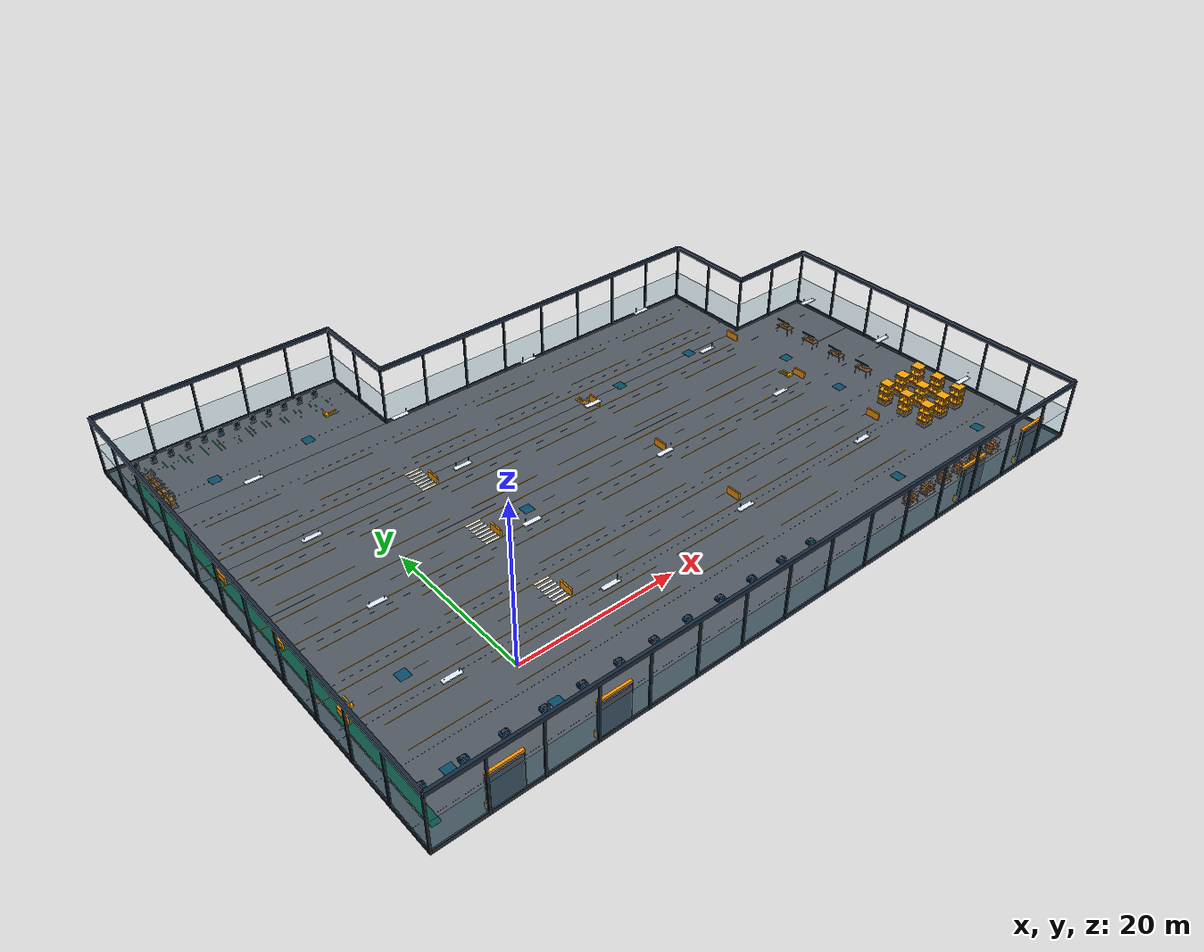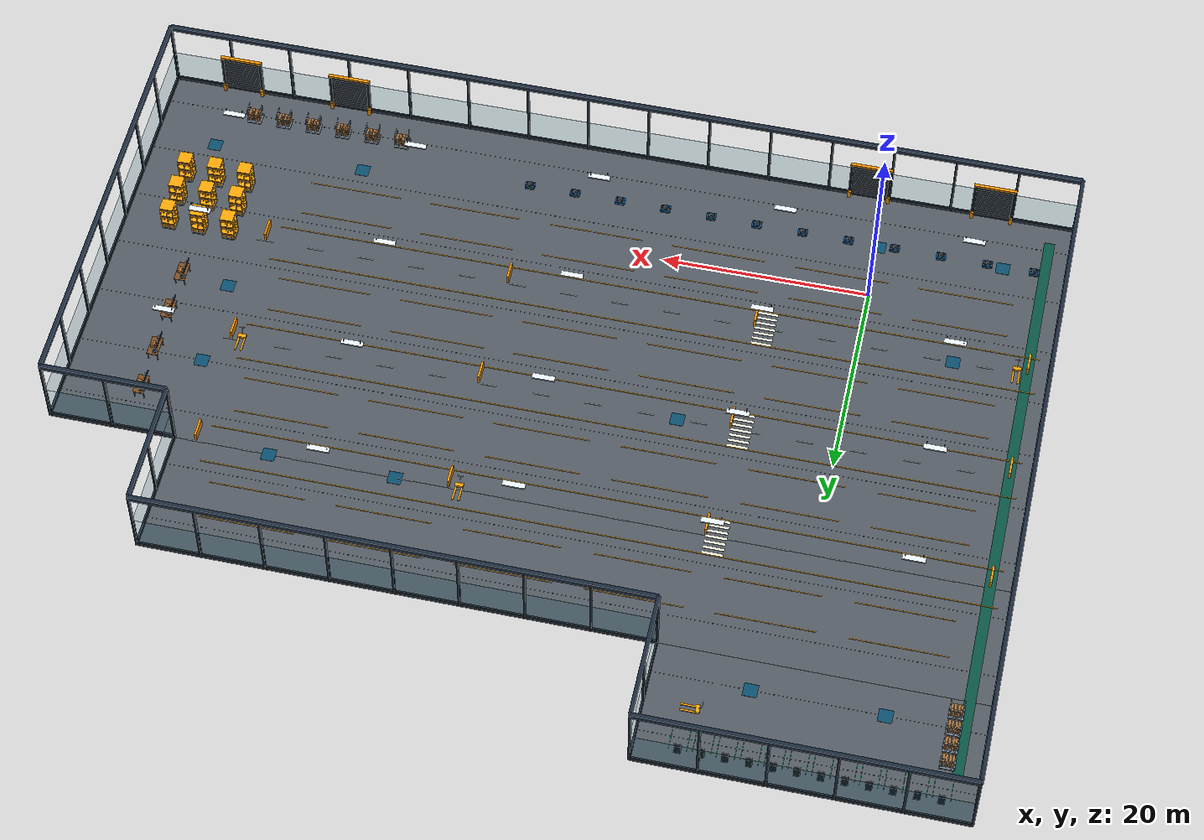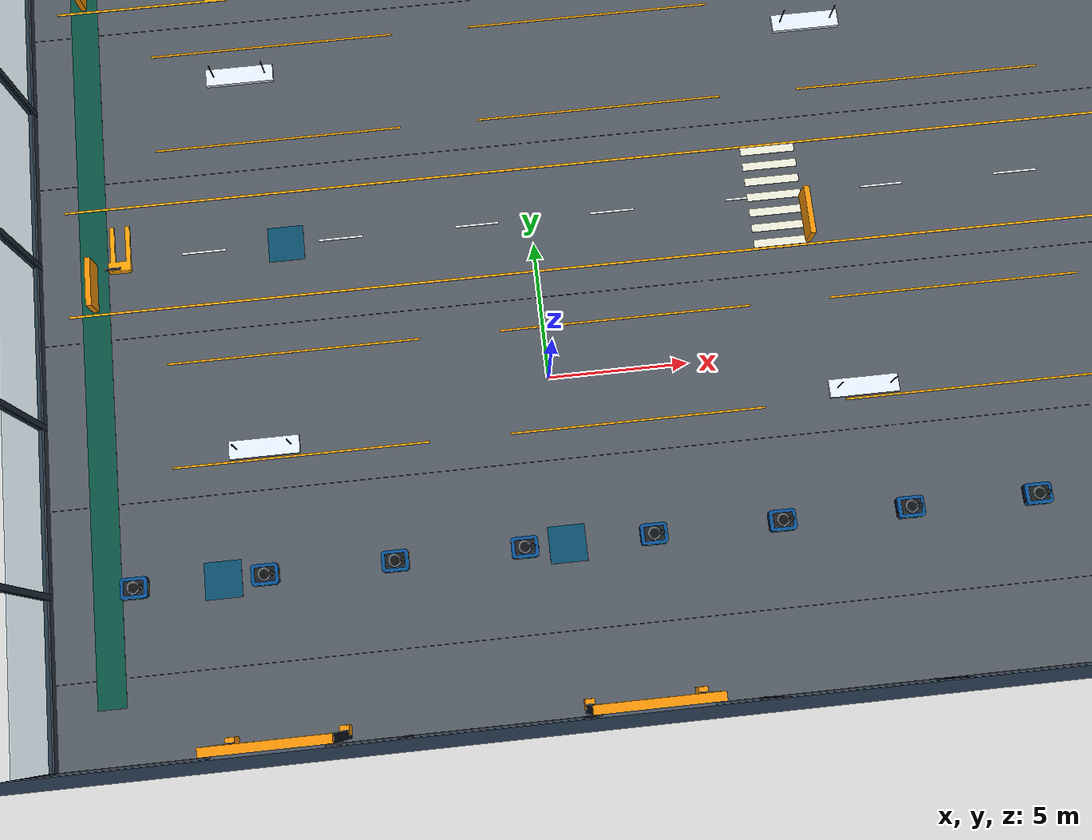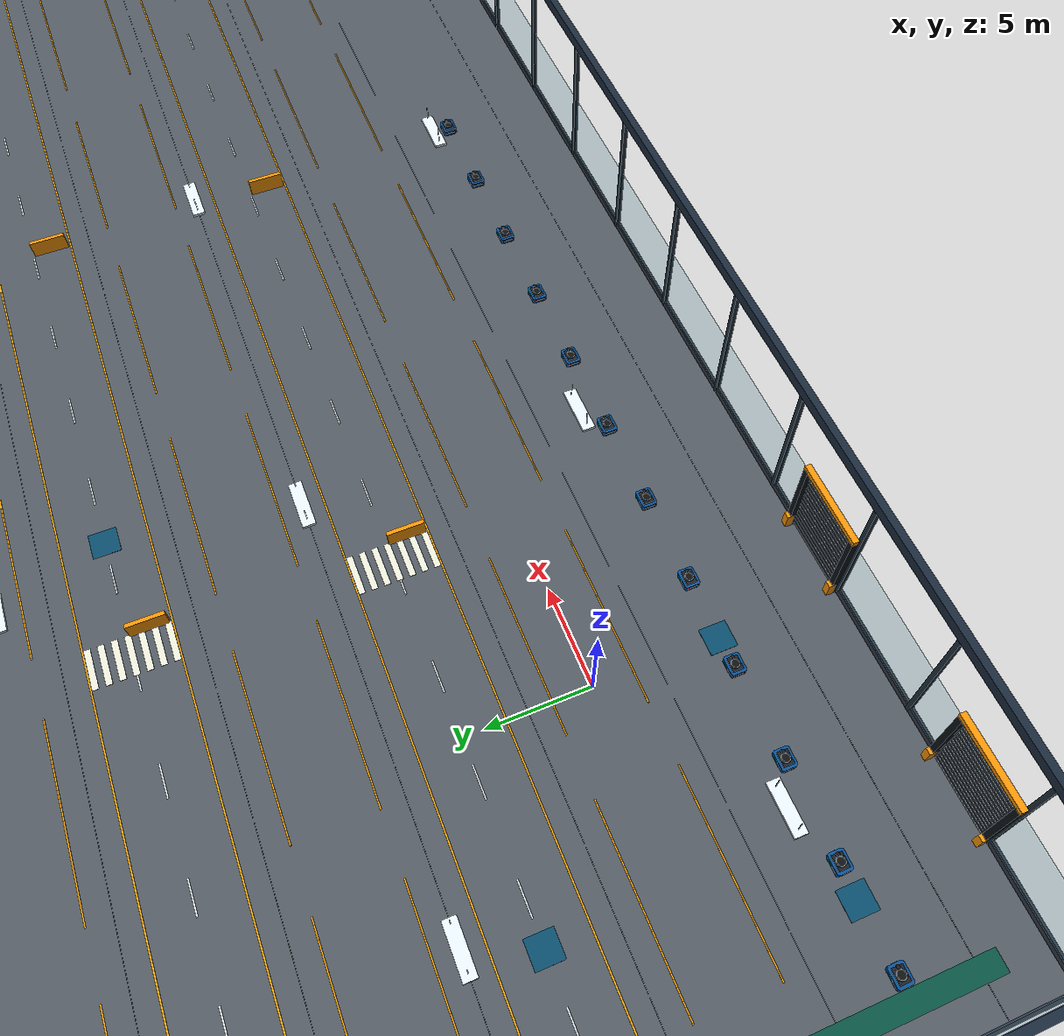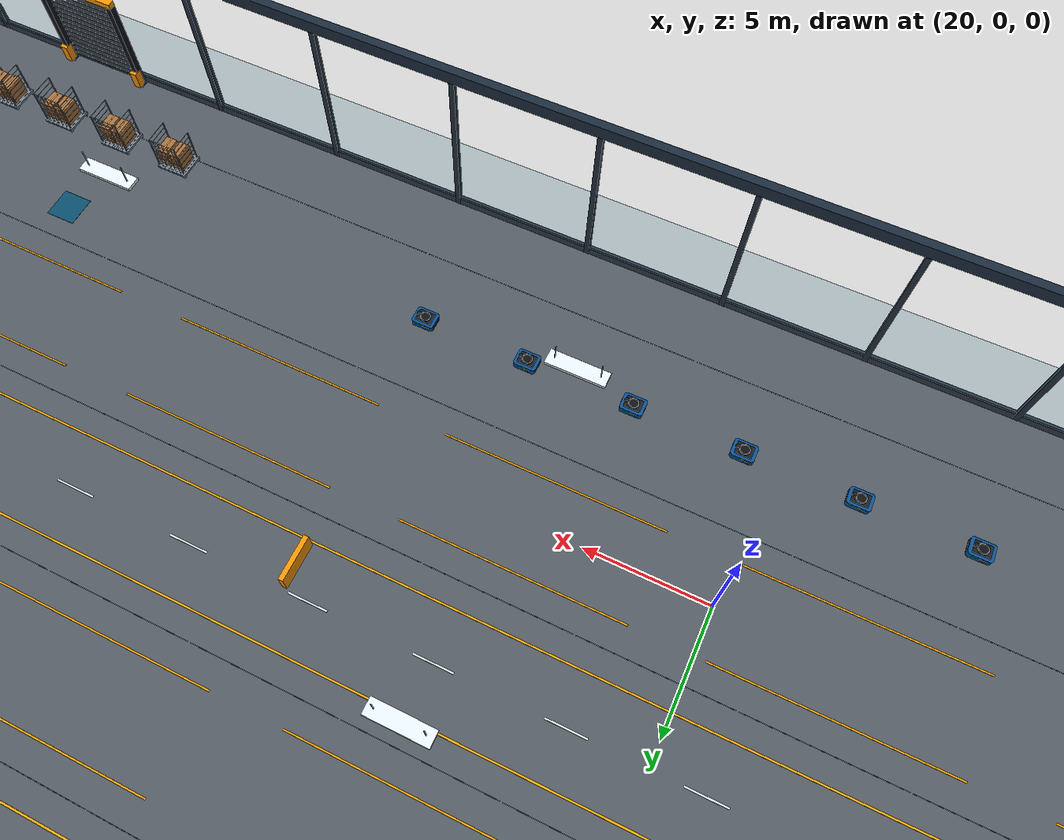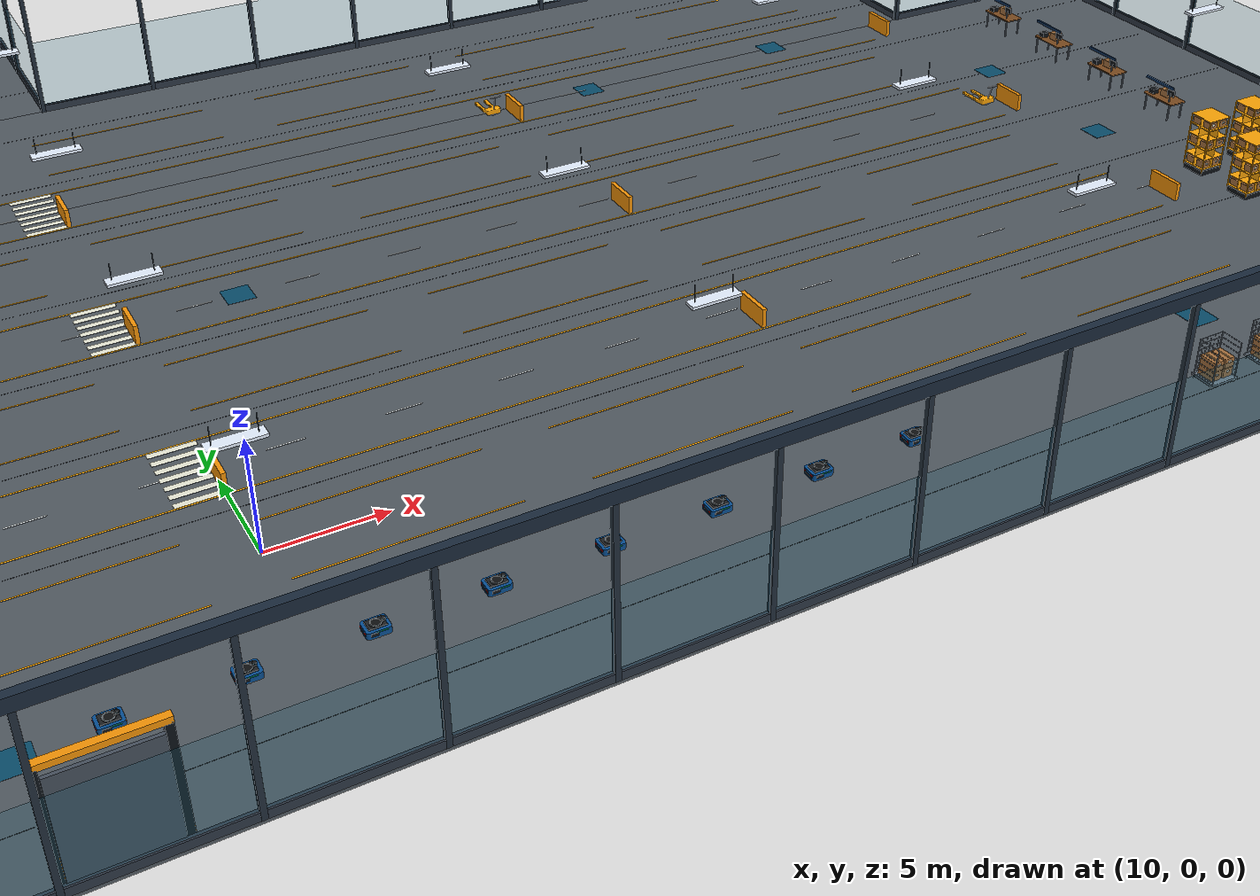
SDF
<sdf version="1.10">
 <world name="kinesis_warehouse">
  <physics name="warehouse_physics" type="ignored">
   <max_step_size>0.002</max_step_size>
   <real_time_factor>1</real_time_factor>
  </physics>
  <plugin name="gz::sim::systems::Physics" filename="gz-sim-physics-system"/>
  <plugin name="gz::sim::systems::UserCommands" filename="gz-sim-user-commands-system"/>
  <plugin name="gz::sim::systems::SceneBroadcaster" filename="gz-sim-scene-broadcaster-system"/>
  <plugin name="gz::sim::systems::Sensors" filename="gz-sim-sensors-system">
   <render_engine>ogre2</render_engine>
  </plugin>
  <gravity>0 0 -9.81</gravity>
  <scene><ambient>.55 .58 .63 1</ambient><background>.055 .075 .10 1</background><shadows>true</shadows></scene>
  <light type="directional" name="daylight">
   <direction>-.4 .25 -1</direction>
   <diffuse>.8 .85 .95 1</diffuse>
   <specular>.2 .2 .2 1</specular>
  </light>
  <model name="warehouse_architecture">
   <static>true</static>
   <link name="structure">
    <visual name="plinth_0">
     <pose>27 -12 0.18 0 0 0</pose>
     <geometry><box><size>90 0.2 0.36</size></box></geometry>
     <material>
      <diffuse>0.18 0.22 0.27 1</diffuse>
      <ambient>0.126 0.154 0.189 1</ambient>
      <specular>.35 .4 .45 1</specular>
     </material>
    </visual>
    <collision name="plinth_0_collision">
     <pose>27 -12 0.18 0 0 0</pose>
     <geometry><box><size>90 0.2 0.36</size></box></geometry>
    </collision>
    <visual name="glass_0">
     <pose>27 -12 2.1 0 0 0</pose>
     <geometry><box><size>90 0.055 3.6</size></box></geometry>
     <material>
      <diffuse>0.1 0.47 0.59 1</diffuse>
      <ambient>0.07 0.329 0.413 1</ambient>
      <specular>.35 .4 .45 1</specular>
     </material>
     <transparency>0.8200000000000001</transparency>
    </visual>
    <collision name="glass_0_collision">
     <pose>27 -12 2.1 0 0 0</pose>
     <geometry><box><size>90 0.055 3.6</size></box></geometry>
    </collision>
    <visual name="parapet_0">
     <pose>27 -12 7.6 0 0 0</pose>
     <geometry><box><size>90 0.35 0.55</size></box></geometry>
     <material>
      <diffuse>0.1 0.16 0.23 1</diffuse>
      <ambient>0.07 0.112 0.161 1</ambient>
      <specular>.35 .4 .45 1</specular>
     </material>
    </visual>
    <visual name="column_0_0">
     <pose>-18 -12 3.8 0 0 0</pose>
     <geometry><box><size>0.22 0.22 7.6</size></box></geometry>
     <material>
      <diffuse>0.13 0.18 0.23 1</diffuse>
      <ambient>0.091 0.126 0.161 1</ambient>
      <specular>.35 .4 .45 1</specular>
     </material>
    </visual>
    <collision name="column_0_0_collision">
     <pose>-18 -12 3.8 0 0 0</pose>
     <geometry><box><size>0.22 0.22 7.6</size></box></geometry>
    </collision>
    <visual name="mullion_0_0">
     <pose>-18 -12 2.1 0 0 0</pose>
     <geometry><box><size>0.1 0.1 3.6</size></box></geometry>
     <material>
      <diffuse>0.08 0.12 0.16 1</diffuse>
      <ambient>0.056 0.084 0.112 1</ambient>
      <specular>.35 .4 .45 1</specular>
     </material>
    </visual>
    <visual name="column_0_1">
     <pose>-12 -12 3.8 0 0 0</pose>
     <geometry><box><size>0.22 0.22 7.6</size></box></geometry>
     <material>
      <diffuse>0.13 0.18 0.23 1</diffuse>
      <ambient>0.091 0.126 0.161 1</ambient>
      <specular>.35 .4 .45 1</specular>
     </material>
    </visual>
    <collision name="column_0_1_collision">
     <pose>-12 -12 3.8 0 0 0</pose>
     <geometry><box><size>0.22 0.22 7.6</size></box></geometry>
    </collision>
    <visual name="mullion_0_1">
     <pose>-12 -12 2.1 0 0 0</pose>
     <geometry><box><size>0.1 0.1 3.6</size></box></geometry>
     <material>
      <diffuse>0.08 0.12 0.16 1</diffuse>
      <ambient>0.056 0.084 0.112 1</ambient>
      <specular>.35 .4 .45 1</specular>
     </material>
    </visual>
    <visual name="column_0_2">
     <pose>-6 -12 3.8 0 0 0</pose>
     <geometry><box><size>0.22 0.22 7.6</size></box></geometry>
     <material>
      <diffuse>0.13 0.18 0.23 1</diffuse>
      <ambient>0.091 0.126 0.161 1</ambient>
      <specular>.35 .4 .45 1</specular>
     </material>
    </visual>
    <collision name="column_0_2_collision">
     <pose>-6 -12 3.8 0 0 0</pose>
     <geometry><box><size>0.22 0.22 7.6</size></box></geometry>
    </collision>
    <visual name="mullion_0_2">
     <pose>-6 -12 2.1 0 0 0</pose>
     <geometry><box><size>0.1 0.1 3.6</size></box></geometry>
     <material>
      <diffuse>0.08 0.12 0.16 1</diffuse>
      <ambient>0.056 0.084 0.112 1</ambient>
      <specular>.35 .4 .45 1</specular>
     </material>
    </visual>
    <visual name="column_0_3">
     <pose>0 -12 3.8 0 0 0</pose>
     <geometry><box><size>0.22 0.22 7.6</size></box></geometry>
     <material>
      <diffuse>0.13 0.18 0.23 1</diffuse>
      <ambient>0.091 0.126 0.161 1</ambient>
      <specular>.35 .4 .45 1</specular>
     </material>
    </visual>
    <collision name="column_0_3_collision">
     <pose>0 -12 3.8 0 0 0</pose>
     <geometry><box><size>0.22 0.22 7.6</size></box></geometry>
    </collision>
    <visual name="mullion_0_3">
     <pose>0 -12 2.1 0 0 0</pose>
     <geometry><box><size>0.1 0.1 3.6</size></box></geometry>
     <material>
      <diffuse>0.08 0.12 0.16 1</diffuse>
      <ambient>0.056 0.084 0.112 1</ambient>
      <specular>.35 .4 .45 1</specular>
     </material>
    </visual>
    <visual name="column_0_4">
     <pose>6 -12 3.8 0 0 0</pose>
     <geometry><box><size>0.22 0.22 7.6</size></box></geometry>
     <material>
      <diffuse>0.13 0.18 0.23 1</diffuse>
      <ambient>0.091 0.126 0.161 1</ambient>
      <specular>.35 .4 .45 1</specular>
     </material>
    </visual>
    <collision name="column_0_4_collision">
     <pose>6 -12 3.8 0 0 0</pose>
     <geometry><box><size>0.22 0.22 7.6</size></box></geometry>
    </collision>
    <visual name="mullion_0_4">
     <pose>6 -12 2.1 0 0 0</pose>
     <geometry><box><size>0.1 0.1 3.6</size></box></geometry>
     <material>
      <diffuse>0.08 0.12 0.16 1</diffuse>
      <ambient>0.056 0.084 0.112 1</ambient>
      <specular>.35 .4 .45 1</specular>
     </material>
    </visual>
    <visual name="column_0_5">
     <pose>12 -12 3.8 0 0 0</pose>
     <geometry><box><size>0.22 0.22 7.6</size></box></geometry>
     <material>
      <diffuse>0.13 0.18 0.23 1</diffuse>
      <ambient>0.091 0.126 0.161 1</ambient>
      <specular>.35 .4 .45 1</specular>
     </material>
    </visual>
    <collision name="column_0_5_collision">
     <pose>12 -12 3.8 0 0 0</pose>
     <geometry><box><size>0.22 0.22 7.6</size></box></geometry>
    </collision>
    <visual name="mullion_0_5">
     <pose>12 -12 2.1 0 0 0</pose>
     <geometry><box><size>0.1 0.1 3.6</size></box></geometry>
     <material>
      <diffuse>0.08 0.12 0.16 1</diffuse>
      <ambient>0.056 0.084 0.112 1</ambient>
      <specular>.35 .4 .45 1</specular>
     </material>
    </visual>
    <visual name="column_0_6">
     <pose>18 -12 3.8 0 0 0</pose>
     <geometry><box><size>0.22 0.22 7.6</size></box></geometry>
     <material>
      <diffuse>0.13 0.18 0.23 1</diffuse>
      <ambient>0.091 0.126 0.161 1</ambient>
      <specular>.35 .4 .45 1</specular>
     </material>
    </visual>
    <collision name="column_0_6_collision">
     <pose>18 -12 3.8 0 0 0</pose>
     <geometry><box><size>0.22 0.22 7.6</size></box></geometry>
    </collision>
    <visual name="mullion_0_6">
     <pose>18 -12 2.1 0 0 0</pose>
     <geometry><box><size>0.1 0.1 3.6</size></box></geometry>
     <material>
      <diffuse>0.08 0.12 0.16 1</diffuse>
      <ambient>0.056 0.084 0.112 1</ambient>
      <specular>.35 .4 .45 1</specular>
     </material>
    </visual>
    <visual name="column_0_7">
     <pose>24 -12 3.8 0 0 0</pose>
     <geometry><box><size>0.22 0.22 7.6</size></box></geometry>
     <material>
      <diffuse>0.13 0.18 0.23 1</diffuse>
      <ambient>0.091 0.126 0.161 1</ambient>
      <specular>.35 .4 .45 1</specular>
     </material>
    </visual>
    <collision name="column_0_7_collision">
     <pose>24 -12 3.8 0 0 0</pose>
     <geometry><box><size>0.22 0.22 7.6</size></box></geometry>
    </collision>
    <visual name="mullion_0_7">
     <pose>24 -12 2.1 0 0 0</pose>
     <geometry><box><size>0.1 0.1 3.6</size></box></geometry>
     <material>
      <diffuse>0.08 0.12 0.16 1</diffuse>
      <ambient>0.056 0.084 0.112 1</ambient>
      <specular>.35 .4 .45 1</specular>
     </material>
    </visual>
    <visual name="column_0_8">
     <pose>30 -12 3.8 0 0 0</pose>
     <geometry><box><size>0.22 0.22 7.6</size></box></geometry>
     <material>
      <diffuse>0.13 0.18 0.23 1</diffuse>
      <ambient>0.091 0.126 0.161 1</ambient>
      <specular>.35 .4 .45 1</specular>
     </material>
    </visual>
    <collision name="column_0_8_collision">
     <pose>30 -12 3.8 0 0 0</pose>
     <geometry><box><size>0.22 0.22 7.6</size></box></geometry>
    </collision>
    <visual name="mullion_0_8">
     <pose>30 -12 2.1 0 0 0</pose>
     <geometry><box><size>0.1 0.1 3.6</size></box></geometry>
     <material>
      <diffuse>0.08 0.12 0.16 1</diffuse>
      <ambient>0.056 0.084 0.112 1</ambient>
      <specular>.35 .4 .45 1</specular>
     </material>
    </visual>
    <visual name="column_0_9">
     <pose>36 -12 3.8 0 0 0</pose>
     <geometry><box><size>0.22 0.22 7.6</size></box></geometry>
     <material>
      <diffuse>0.13 0.18 0.23 1</diffuse>
      <ambient>0.091 0.126 0.161 1</ambient>
      <specular>.35 .4 .45 1</specular>
     </material>
    </visual>
    <collision name="column_0_9_collision">
     <pose>36 -12 3.8 0 0 0</pose>
     <geometry><box><size>0.22 0.22 7.6</size></box></geometry>
    </collision>
    <visual name="mullion_0_9">
     <pose>36 -12 2.1 0 0 0</pose>
     <geometry><box><size>0.1 0.1 3.6</size></box></geometry>
     <material>
      <diffuse>0.08 0.12 0.16 1</diffuse>
      <ambient>0.056 0.084 0.112 1</ambient>
      <specular>.35 .4 .45 1</specular>
     </material>
    </visual>
    <visual name="column_0_10">
     <pose>42 -12 3.8 0 0 0</pose>
     <geometry><box><size>0.22 0.22 7.6</size></box></geometry>
     <material>
      <diffuse>0.13 0.18 0.23 1</diffuse>
      <ambient>0.091 0.126 0.161 1</ambient>
      <specular>.35 .4 .45 1</specular>
     </material>
    </visual>
    <collision name="column_0_10_collision">
     <pose>42 -12 3.8 0 0 0</pose>
     <geometry><box><size>0.22 0.22 7.6</size></box></geometry>
    </collision>
    <visual name="mullion_0_10">
     <pose>42 -12 2.1 0 0 0</pose>
     <geometry><box><size>0.1 0.1 3.6</size></box></geometry>
     <material>
      <diffuse>0.08 0.12 0.16 1</diffuse>
      <ambient>0.056 0.084 0.112 1</ambient>
      <specular>.35 .4 .45 1</specular>
     </material>
    </visual>
    <visual name="column_0_11">
     <pose>48 -12 3.8 0 0 0</pose>
     <geometry><box><size>0.22 0.22 7.6</size></box></geometry>
     <material>
      <diffuse>0.13 0.18 0.23 1</diffuse>
      <ambient>0.091 0.126 0.161 1</ambient>
      <specular>.35 .4 .45 1</specular>
     </material>
    </visual>
    <collision name="column_0_11_collision">
     <pose>48 -12 3.8 0 0 0</pose>
     <geometry><box><size>0.22 0.22 7.6</size></box></geometry>
    </collision>
    <visual name="mullion_0_11">
     <pose>48 -12 2.1 0 0 0</pose>
     <geometry><box><size>0.1 0.1 3.6</size></box></geometry>
     <material>
      <diffuse>0.08 0.12 0.16 1</diffuse>
      <ambient>0.056 0.084 0.112 1</ambient>
      <specular>.35 .4 .45 1</specular>
     </material>
    </visual>
    <visual name="column_0_12">
     <pose>54 -12 3.8 0 0 0</pose>
     <geometry><box><size>0.22 0.22 7.6</size></box></geometry>
     <material>
      <diffuse>0.13 0.18 0.23 1</diffuse>
      <ambient>0.091 0.126 0.161 1</ambient>
      <specular>.35 .4 .45 1</specular>
     </material>
    </visual>
    <collision name="column_0_12_collision">
     <pose>54 -12 3.8 0 0 0</pose>
     <geometry><box><size>0.22 0.22 7.6</size></box></geometry>
    </collision>
    <visual name="mullion_0_12">
     <pose>54 -12 2.1 0 0 0</pose>
     <geometry><box><size>0.1 0.1 3.6</size></box></geometry>
     <material>
      <diffuse>0.08 0.12 0.16 1</diffuse>
      <ambient>0.056 0.084 0.112 1</ambient>
      <specular>.35 .4 .45 1</specular>
     </material>
    </visual>
    <visual name="column_0_13">
     <pose>60 -12 3.8 0 0 0</pose>
     <geometry><box><size>0.22 0.22 7.6</size></box></geometry>
     <material>
      <diffuse>0.13 0.18 0.23 1</diffuse>
      <ambient>0.091 0.126 0.161 1</ambient>
      <specular>.35 .4 .45 1</specular>
     </material>
    </visual>
    <collision name="column_0_13_collision">
     <pose>60 -12 3.8 0 0 0</pose>
     <geometry><box><size>0.22 0.22 7.6</size></box></geometry>
    </collision>
    <visual name="mullion_0_13">
     <pose>60 -12 2.1 0 0 0</pose>
     <geometry><box><size>0.1 0.1 3.6</size></box></geometry>
     <material>
      <diffuse>0.08 0.12 0.16 1</diffuse>
      <ambient>0.056 0.084 0.112 1</ambient>
      <specular>.35 .4 .45 1</specular>
     </material>
    </visual>
    <visual name="column_0_14">
     <pose>66 -12 3.8 0 0 0</pose>
     <geometry><box><size>0.22 0.22 7.6</size></box></geometry>
     <material>
      <diffuse>0.13 0.18 0.23 1</diffuse>
      <ambient>0.091 0.126 0.161 1</ambient>
      <specular>.35 .4 .45 1</specular>
     </material>
    </visual>
    <collision name="column_0_14_collision">
     <pose>66 -12 3.8 0 0 0</pose>
     <geometry><box><size>0.22 0.22 7.6</size></box></geometry>
    </collision>
    <visual name="mullion_0_14">
     <pose>66 -12 2.1 0 0 0</pose>
     <geometry><box><size>0.1 0.1 3.6</size></box></geometry>
     <material>
      <diffuse>0.08 0.12 0.16 1</diffuse>
      <ambient>0.056 0.084 0.112 1</ambient>
      <specular>.35 .4 .45 1</specular>
     </material>
    </visual>
    <visual name="column_0_15">
     <pose>72 -12 3.8 0 0 0</pose>
     <geometry><box><size>0.22 0.22 7.6</size></box></geometry>
     <material>
      <diffuse>0.13 0.18 0.23 1</diffuse>
      <ambient>0.091 0.126 0.161 1</ambient>
      <specular>.35 .4 .45 1</specular>
     </material>
    </visual>
    <collision name="column_0_15_collision">
     <pose>72 -12 3.8 0 0 0</pose>
     <geometry><box><size>0.22 0.22 7.6</size></box></geometry>
    </collision>
    <visual name="mullion_0_15">
     <pose>72 -12 2.1 0 0 0</pose>
     <geometry><box><size>0.1 0.1 3.6</size></box></geometry>
     <material>
      <diffuse>0.08 0.12 0.16 1</diffuse>
      <ambient>0.056 0.084 0.112 1</ambient>
      <specular>.35 .4 .45 1</specular>
     </material>
    </visual>
    <visual name="plinth_1">
     <pose>72 9 0.18 0 0 1.5708</pose>
     <geometry><box><size>42 0.2 0.36</size></box></geometry>
     <material>
      <diffuse>0.18 0.22 0.27 1</diffuse>
      <ambient>0.126 0.154 0.189 1</ambient>
      <specular>.35 .4 .45 1</specular>
     </material>
    </visual>
    <collision name="plinth_1_collision">
     <pose>72 9 0.18 0 0 1.5708</pose>
     <geometry><box><size>42 0.2 0.36</size></box></geometry>
    </collision>
    <visual name="glass_1">
     <pose>72 9 2.1 0 0 1.5708</pose>
     <geometry><box><size>42 0.055 3.6</size></box></geometry>
     <material>
      <diffuse>0.1 0.47 0.59 1</diffuse>
      <ambient>0.07 0.329 0.413 1</ambient>
      <specular>.35 .4 .45 1</specular>
     </material>
     <transparency>0.8200000000000001</transparency>
    </visual>
    <collision name="glass_1_collision">
     <pose>72 9 2.1 0 0 1.5708</pose>
     <geometry><box><size>42 0.055 3.6</size></box></geometry>
    </collision>
    <visual name="parapet_1">
     <pose>72 9 7.6 0 0 1.5708</pose>
     <geometry><box><size>42 0.35 0.55</size></box></geometry>
     <material>
      <diffuse>0.1 0.16 0.23 1</diffuse>
      <ambient>0.07 0.112 0.161 1</ambient>
      <specular>.35 .4 .45 1</specular>
     </material>
    </visual>
    <visual name="column_1_0">
     <pose>72 -12 3.8 0 0 0</pose>
     <geometry><box><size>0.22 0.22 7.6</size></box></geometry>
     <material>
      <diffuse>0.13 0.18 0.23 1</diffuse>
      <ambient>0.091 0.126 0.161 1</ambient>
      <specular>.35 .4 .45 1</specular>
     </material>
    </visual>
    <collision name="column_1_0_collision">
     <pose>72 -12 3.8 0 0 0</pose>
     <geometry><box><size>0.22 0.22 7.6</size></box></geometry>
    </collision>
    <visual name="mullion_1_0">
     <pose>72 -12 2.1 0 0 0</pose>
     <geometry><box><size>0.1 0.1 3.6</size></box></geometry>
     <material>
      <diffuse>0.08 0.12 0.16 1</diffuse>
      <ambient>0.056 0.084 0.112 1</ambient>
      <specular>.35 .4 .45 1</specular>
     </material>
    </visual>
    <visual name="column_1_1">
     <pose>72 -6 3.8 0 0 0</pose>
     <geometry><box><size>0.22 0.22 7.6</size></box></geometry>
     <material>
      <diffuse>0.13 0.18 0.23 1</diffuse>
      <ambient>0.091 0.126 0.161 1</ambient>
      <specular>.35 .4 .45 1</specular>
     </material>
    </visual>
    <collision name="column_1_1_collision">
     <pose>72 -6 3.8 0 0 0</pose>
     <geometry><box><size>0.22 0.22 7.6</size></box></geometry>
    </collision>
    <visual name="mullion_1_1">
     <pose>72 -6 2.1 0 0 0</pose>
     <geometry><box><size>0.1 0.1 3.6</size></box></geometry>
     <material>
      <diffuse>0.08 0.12 0.16 1</diffuse>
      <ambient>0.056 0.084 0.112 1</ambient>
      <specular>.35 .4 .45 1</specular>
     </material>
    </visual>
    <visual name="column_1_2">
     <pose>72 0 3.8 0 0 0</pose>
     <geometry><box><size>0.22 0.22 7.6</size></box></geometry>
     <material>
      <diffuse>0.13 0.18 0.23 1</diffuse>
      <ambient>0.091 0.126 0.161 1</ambient>
      <specular>.35 .4 .45 1</specular>
     </material>
    </visual>
    <collision name="column_1_2_collision">
     <pose>72 0 3.8 0 0 0</pose>
     <geometry><box><size>0.22 0.22 7.6</size></box></geometry>
    </collision>
    <visual name="mullion_1_2">
     <pose>72 0 2.1 0 0 0</pose>
     <geometry><box><size>0.1 0.1 3.6</size></box></geometry>
     <material>
      <diffuse>0.08 0.12 0.16 1</diffuse>
      <ambient>0.056 0.084 0.112 1</ambient>
      <specular>.35 .4 .45 1</specular>
     </material>
    </visual>
    <visual name="column_1_3">
     <pose>72 6 3.8 0 0 0</pose>
     <geometry><box><size>0.22 0.22 7.6</size></box></geometry>
     <material>
      <diffuse>0.13 0.18 0.23 1</diffuse>
      <ambient>0.091 0.126 0.161 1</ambient>
      <specular>.35 .4 .45 1</specular>
     </material>
    </visual>
    <collision name="column_1_3_collision">
     <pose>72 6 3.8 0 0 0</pose>
     <geometry><box><size>0.22 0.22 7.6</size></box></geometry>
    </collision>
    <visual name="mullion_1_3">
     <pose>72 6 2.1 0 0 0</pose>
     <geometry><box><size>0.1 0.1 3.6</size></box></geometry>
     <material>
      <diffuse>0.08 0.12 0.16 1</diffuse>
      <ambient>0.056 0.084 0.112 1</ambient>
      <specular>.35 .4 .45 1</specular>
     </material>
    </visual>
    <visual name="column_1_4">
     <pose>72 12 3.8 0 0 0</pose>
     <geometry><box><size>0.22 0.22 7.6</size></box></geometry>
     <material>
      <diffuse>0.13 0.18 0.23 1</diffuse>
      <ambient>0.091 0.126 0.161 1</ambient>
      <specular>.35 .4 .45 1</specular>
     </material>
    </visual>
    <collision name="column_1_4_collision">
     <pose>72 12 3.8 0 0 0</pose>
     <geometry><box><size>0.22 0.22 7.6</size></box></geometry>
    </collision>
    <visual name="mullion_1_4">
     <pose>72 12 2.1 0 0 0</pose>
     <geometry><box><size>0.1 0.1 3.6</size></box></geometry>
     <material>
      <diffuse>0.08 0.12 0.16 1</diffuse>
      <ambient>0.056 0.084 0.112 1</ambient>
      <specular>.35 .4 .45 1</specular>
     </material>
    </visual>
    <visual name="column_1_5">
     <pose>72 18 3.8 0 0 0</pose>
     <geometry><box><size>0.22 0.22 7.6</size></box></geometry>
     <material>
      <diffuse>0.13 0.18 0.23 1</diffuse>
      <ambient>0.091 0.126 0.161 1</ambient>
      <specular>.35 .4 .45 1</specular>
     </material>
    </visual>
    <collision name="column_1_5_collision">
     <pose>72 18 3.8 0 0 0</pose>
     <geometry><box><size>0.22 0.22 7.6</size></box></geometry>
    </collision>
    <visual name="mullion_1_5">
     <pose>72 18 2.1 0 0 0</pose>
     <geometry><box><size>0.1 0.1 3.6</size></box></geometry>
     <material>
      <diffuse>0.08 0.12 0.16 1</diffuse>
      <ambient>0.056 0.084 0.112 1</ambient>
      <specular>.35 .4 .45 1</specular>
     </material>
    </visual>
    <visual name="column_1_6">
     <pose>72 24 3.8 0 0 0</pose>
     <geometry><box><size>0.22 0.22 7.6</size></box></geometry>
     <material>
      <diffuse>0.13 0.18 0.23 1</diffuse>
      <ambient>0.091 0.126 0.161 1</ambient>
      <specular>.35 .4 .45 1</specular>
     </material>
    </visual>
    <collision name="column_1_6_collision">
     <pose>72 24 3.8 0 0 0</pose>
     <geometry><box><size>0.22 0.22 7.6</size></box></geometry>
    </collision>
    <visual name="mullion_1_6">
     <pose>72 24 2.1 0 0 0</pose>
     <geometry><box><size>0.1 0.1 3.6</size></box></geometry>
     <material>
      <diffuse>0.08 0.12 0.16 1</diffuse>
      <ambient>0.056 0.084 0.112 1</ambient>
      <specular>.35 .4 .45 1</specular>
     </material>
    </visual>
    <visual name="column_1_7">
     <pose>72 30 3.8 0 0 0</pose>
     <geometry><box><size>0.22 0.22 7.6</size></box></geometry>
     <material>
      <diffuse>0.13 0.18 0.23 1</diffuse>
      <ambient>0.091 0.126 0.161 1</ambient>
      <specular>.35 .4 .45 1</specular>
     </material>
    </visual>
    <collision name="column_1_7_collision">
     <pose>72 30 3.8 0 0 0</pose>
     <geometry><box><size>0.22 0.22 7.6</size></box></geometry>
    </collision>
    <visual name="mullion_1_7">
     <pose>72 30 2.1 0 0 0</pose>
     <geometry><box><size>0.1 0.1 3.6</size></box></geometry>
     <material>
      <diffuse>0.08 0.12 0.16 1</diffuse>
      <ambient>0.056 0.084 0.112 1</ambient>
      <specular>.35 .4 .45 1</specular>
     </material>
    </visual>
    <visual name="plinth_2">
     <pose>66 30 0.18 0 0 3.1416</pose>
     <geometry><box><size>12 0.2 0.36</size></box></geometry>
     <material>
      <diffuse>0.18 0.22 0.27 1</diffuse>
      <ambient>0.126 0.154 0.189 1</ambient>
      <specular>.35 .4 .45 1</specular>
     </material>
    </visual>
    <collision name="plinth_2_collision">
     <pose>66 30 0.18 0 0 3.1416</pose>
     <geometry><box><size>12 0.2 0.36</size></box></geometry>
    </collision>
    <visual name="glass_2">
     <pose>66 30 2.1 0 0 3.1416</pose>
     <geometry><box><size>12 0.055 3.6</size></box></geometry>
     <material>
      <diffuse>0.1 0.47 0.59 1</diffuse>
      <ambient>0.07 0.329 0.413 1</ambient>
      <specular>.35 .4 .45 1</specular>
     </material>
     <transparency>0.8200000000000001</transparency>
    </visual>
    <collision name="glass_2_collision">
     <pose>66 30 2.1 0 0 3.1416</pose>
     <geometry><box><size>12 0.055 3.6</size></box></geometry>
    </collision>
    <visual name="parapet_2">
     <pose>66 30 7.6 0 0 3.1416</pose>
     <geometry><box><size>12 0.35 0.55</size></box></geometry>
     <material>
      <diffuse>0.1 0.16 0.23 1</diffuse>
      <ambient>0.07 0.112 0.161 1</ambient>
      <specular>.35 .4 .45 1</specular>
     </material>
    </visual>
    <visual name="column_2_0">
     <pose>72 30 3.8 0 0 0</pose>
     <geometry><box><size>0.22 0.22 7.6</size></box></geometry>
     <material>
      <diffuse>0.13 0.18 0.23 1</diffuse>
      <ambient>0.091 0.126 0.161 1</ambient>
      <specular>.35 .4 .45 1</specular>
     </material>
    </visual>
    <collision name="column_2_0_collision">
     <pose>72 30 3.8 0 0 0</pose>
     <geometry><box><size>0.22 0.22 7.6</size></box></geometry>
    </collision>
    <visual name="mullion_2_0">
     <pose>72 30 2.1 0 0 0</pose>
     <geometry><box><size>0.1 0.1 3.6</size></box></geometry>
     <material>
      <diffuse>0.08 0.12 0.16 1</diffuse>
      <ambient>0.056 0.084 0.112 1</ambient>
      <specular>.35 .4 .45 1</specular>
     </material>
    </visual>
    <visual name="column_2_1">
     <pose>66 30 3.8 0 0 0</pose>
     <geometry><box><size>0.22 0.22 7.6</size></box></geometry>
     <material>
      <diffuse>0.13 0.18 0.23 1</diffuse>
      <ambient>0.091 0.126 0.161 1</ambient>
      <specular>.35 .4 .45 1</specular>
     </material>
    </visual>
    <collision name="column_2_1_collision">
     <pose>66 30 3.8 0 0 0</pose>
     <geometry><box><size>0.22 0.22 7.6</size></box></geometry>
    </collision>
    <visual name="mullion_2_1">
     <pose>66 30 2.1 0 0 0</pose>
     <geometry><box><size>0.1 0.1 3.6</size></box></geometry>
     <material>
      <diffuse>0.08 0.12 0.16 1</diffuse>
      <ambient>0.056 0.084 0.112 1</ambient>
      <specular>.35 .4 .45 1</specular>
     </material>
    </visual>
    <visual name="column_2_2">
     <pose>60 30 3.8 0 0 0</pose>
     <geometry><box><size>0.22 0.22 7.6</size></box></geometry>
     <material>
      <diffuse>0.13 0.18 0.23 1</diffuse>
      <ambient>0.091 0.126 0.161 1</ambient>
      <specular>.35 .4 .45 1</specular>
     </material>
    </visual>
    <collision name="column_2_2_collision">
     <pose>60 30 3.8 0 0 0</pose>
     <geometry><box><size>0.22 0.22 7.6</size></box></geometry>
    </collision>
    <visual name="mullion_2_2">
     <pose>60 30 2.1 0 0 0</pose>
     <geometry><box><size>0.1 0.1 3.6</size></box></geometry>
     <material>
      <diffuse>0.08 0.12 0.16 1</diffuse>
      <ambient>0.056 0.084 0.112 1</ambient>
      <specular>.35 .4 .45 1</specular>
     </material>
    </visual>
    <visual name="plinth_3">
     <pose>60 36 0.18 0 0 1.5708</pose>
     <geometry><box><size>12 0.2 0.36</size></box></geometry>
     <material>
      <diffuse>0.18 0.22 0.27 1</diffuse>
      <ambient>0.126 0.154 0.189 1</ambient>
      <specular>.35 .4 .45 1</specular>
     </material>
    </visual>
    <collision name="plinth_3_collision">
     <pose>60 36 0.18 0 0 1.5708</pose>
     <geometry><box><size>12 0.2 0.36</size></box></geometry>
    </collision>
    <visual name="glass_3">
     <pose>60 36 2.1 0 0 1.5708</pose>
     <geometry><box><size>12 0.055 3.6</size></box></geometry>
     <material>
      <diffuse>0.1 0.47 0.59 1</diffuse>
      <ambient>0.07 0.329 0.413 1</ambient>
      <specular>.35 .4 .45 1</specular>
     </material>
     <transparency>0.8200000000000001</transparency>
    </visual>
    <collision name="glass_3_collision">
     <pose>60 36 2.1 0 0 1.5708</pose>
     <geometry><box><size>12 0.055 3.6</size></box></geometry>
    </collision>
    <visual name="parapet_3">
     <pose>60 36 7.6 0 0 1.5708</pose>
     <geometry><box><size>12 0.35 0.55</size></box></geometry>
     <material>
      <diffuse>0.1 0.16 0.23 1</diffuse>
      <ambient>0.07 0.112 0.161 1</ambient>
      <specular>.35 .4 .45 1</specular>
     </material>
    </visual>
    <visual name="column_3_0">
     <pose>60 30 3.8 0 0 0</pose>
     <geometry><box><size>0.22 0.22 7.6</size></box></geometry>
     <material>
      <diffuse>0.13 0.18 0.23 1</diffuse>
      <ambient>0.091 0.126 0.161 1</ambient>
      <specular>.35 .4 .45 1</specular>
     </material>
    </visual>
    <collision name="column_3_0_collision">
     <pose>60 30 3.8 0 0 0</pose>
     <geometry><box><size>0.22 0.22 7.6</size></box></geometry>
    </collision>
    <visual name="mullion_3_0">
     <pose>60 30 2.1 0 0 0</pose>
     <geometry><box><size>0.1 0.1 3.6</size></box></geometry>
     <material>
      <diffuse>0.08 0.12 0.16 1</diffuse>
      <ambient>0.056 0.084 0.112 1</ambient>
      <specular>.35 .4 .45 1</specular>
     </material>
    </visual>
    <visual name="column_3_1">
     <pose>60 36 3.8 0 0 0</pose>
     <geometry><box><size>0.22 0.22 7.6</size></box></geometry>
     <material>
      <diffuse>0.13 0.18 0.23 1</diffuse>
      <ambient>0.091 0.126 0.161 1</ambient>
      <specular>.35 .4 .45 1</specular>
     </material>
    </visual>
    <collision name="column_3_1_collision">
     <pose>60 36 3.8 0 0 0</pose>
     <geometry><box><size>0.22 0.22 7.6</size></box></geometry>
    </collision>
    <visual name="mullion_3_1">
     <pose>60 36 2.1 0 0 0</pose>
     <geometry><box><size>0.1 0.1 3.6</size></box></geometry>
     <material>
      <diffuse>0.08 0.12 0.16 1</diffuse>
      <ambient>0.056 0.084 0.112 1</ambient>
      <specular>.35 .4 .45 1</specular>
     </material>
    </visual>
    <visual name="column_3_2">
     <pose>60 42 3.8 0 0 0</pose>
     <geometry><box><size>0.22 0.22 7.6</size></box></geometry>
     <material>
      <diffuse>0.13 0.18 0.23 1</diffuse>
      <ambient>0.091 0.126 0.161 1</ambient>
      <specular>.35 .4 .45 1</specular>
     </material>
    </visual>
    <collision name="column_3_2_collision">
     <pose>60 42 3.8 0 0 0</pose>
     <geometry><box><size>0.22 0.22 7.6</size></box></geometry>
    </collision>
    <visual name="mullion_3_2">
     <pose>60 42 2.1 0 0 0</pose>
     <geometry><box><size>0.1 0.1 3.6</size></box></geometry>
     <material>
      <diffuse>0.08 0.12 0.16 1</diffuse>
      <ambient>0.056 0.084 0.112 1</ambient>
      <specular>.35 .4 .45 1</specular>
     </material>
    </visual>
    <visual name="plinth_4">
     <pose>36 42 0.18 0 0 3.1416</pose>
     <geometry><box><size>48 0.2 0.36</size></box></geometry>
     <material>
      <diffuse>0.18 0.22 0.27 1</diffuse>
      <ambient>0.126 0.154 0.189 1</ambient>
      <specular>.35 .4 .45 1</specular>
     </material>
    </visual>
    <collision name="plinth_4_collision">
     <pose>36 42 0.18 0 0 3.1416</pose>
     <geometry><box><size>48 0.2 0.36</size></box></geometry>
    </collision>
    <visual name="glass_4">
     <pose>36 42 2.1 0 0 3.1416</pose>
     <geometry><box><size>48 0.055 3.6</size></box></geometry>
     <material>
      <diffuse>0.1 0.47 0.59 1</diffuse>
      <ambient>0.07 0.329 0.413 1</ambient>
      <specular>.35 .4 .45 1</specular>
     </material>
     <transparency>0.8200000000000001</transparency>
    </visual>
    <collision name="glass_4_collision">
     <pose>36 42 2.1 0 0 3.1416</pose>
     <geometry><box><size>48 0.055 3.6</size></box></geometry>
    </collision>
    <visual name="parapet_4">
     <pose>36 42 7.6 0 0 3.1416</pose>
     <geometry><box><size>48 0.35 0.55</size></box></geometry>
     <material>
      <diffuse>0.1 0.16 0.23 1</diffuse>
      <ambient>0.07 0.112 0.161 1</ambient>
      <specular>.35 .4 .45 1</specular>
     </material>
    </visual>
    <visual name="column_4_0">
     <pose>60 42 3.8 0 0 0</pose>
     <geometry><box><size>0.22 0.22 7.6</size></box></geometry>
     <material>
      <diffuse>0.13 0.18 0.23 1</diffuse>
      <ambient>0.091 0.126 0.161 1</ambient>
      <specular>.35 .4 .45 1</specular>
     </material>
    </visual>
    <collision name="column_4_0_collision">
     <pose>60 42 3.8 0 0 0</pose>
     <geometry><box><size>0.22 0.22 7.6</size></box></geometry>
    </collision>
    <visual name="mullion_4_0">
     <pose>60 42 2.1 0 0 0</pose>
     <geometry><box><size>0.1 0.1 3.6</size></box></geometry>
     <material>
      <diffuse>0.08 0.12 0.16 1</diffuse>
      <ambient>0.056 0.084 0.112 1</ambient>
      <specular>.35 .4 .45 1</specular>
     </material>
    </visual>
    <visual name="column_4_1">
     <pose>54 42 3.8 0 0 0</pose>
     <geometry><box><size>0.22 0.22 7.6</size></box></geometry>
     <material>
      <diffuse>0.13 0.18 0.23 1</diffuse>
      <ambient>0.091 0.126 0.161 1</ambient>
      <specular>.35 .4 .45 1</specular>
     </material>
    </visual>
    <collision name="column_4_1_collision">
     <pose>54 42 3.8 0 0 0</pose>
     <geometry><box><size>0.22 0.22 7.6</size></box></geometry>
    </collision>
    <visual name="mullion_4_1">
     <pose>54 42 2.1 0 0 0</pose>
     <geometry><box><size>0.1 0.1 3.6</size></box></geometry>
     <material>
      <diffuse>0.08 0.12 0.16 1</diffuse>
      <ambient>0.056 0.084 0.112 1</ambient>
      <specular>.35 .4 .45 1</specular>
     </material>
    </visual>
    <visual name="column_4_2">
     <pose>48 42 3.8 0 0 0</pose>
     <geometry><box><size>0.22 0.22 7.6</size></box></geometry>
     <material>
      <diffuse>0.13 0.18 0.23 1</diffuse>
      <ambient>0.091 0.126 0.161 1</ambient>
      <specular>.35 .4 .45 1</specular>
     </material>
    </visual>
    <collision name="column_4_2_collision">
     <pose>48 42 3.8 0 0 0</pose>
     <geometry><box><size>0.22 0.22 7.6</size></box></geometry>
    </collision>
    <visual name="mullion_4_2">
     <pose>48 42 2.1 0 0 0</pose>
     <geometry><box><size>0.1 0.1 3.6</size></box></geometry>
     <material>
      <diffuse>0.08 0.12 0.16 1</diffuse>
      <ambient>0.056 0.084 0.112 1</ambient>
      <specular>.35 .4 .45 1</specular>
     </material>
    </visual>
    <visual name="column_4_3">
     <pose>42 42 3.8 0 0 0</pose>
     <geometry><box><size>0.22 0.22 7.6</size></box></geometry>
     <material>
      <diffuse>0.13 0.18 0.23 1</diffuse>
      <ambient>0.091 0.126 0.161 1</ambient>
      <specular>.35 .4 .45 1</specular>
     </material>
    </visual>
    <collision name="column_4_3_collision">
     <pose>42 42 3.8 0 0 0</pose>
     <geometry><box><size>0.22 0.22 7.6</size></box></geometry>
    </collision>
    <visual name="mullion_4_3">
     <pose>42 42 2.1 0 0 0</pose>
     <geometry><box><size>0.1 0.1 3.6</size></box></geometry>
     <material>
      <diffuse>0.08 0.12 0.16 1</diffuse>
      <ambient>0.056 0.084 0.112 1</ambient>
      <specular>.35 .4 .45 1</specular>
     </material>
    </visual>
    <visual name="column_4_4">
     <pose>36 42 3.8 0 0 0</pose>
     <geometry><box><size>0.22 0.22 7.6</size></box></geometry>
     <material>
      <diffuse>0.13 0.18 0.23 1</diffuse>
      <ambient>0.091 0.126 0.161 1</ambient>
      <specular>.35 .4 .45 1</specular>
     </material>
    </visual>
    <collision name="column_4_4_collision">
     <pose>36 42 3.8 0 0 0</pose>
     <geometry><box><size>0.22 0.22 7.6</size></box></geometry>
    </collision>
    <visual name="mullion_4_4">
     <pose>36 42 2.1 0 0 0</pose>
     <geometry><box><size>0.1 0.1 3.6</size></box></geometry>
     <material>
      <diffuse>0.08 0.12 0.16 1</diffuse>
      <ambient>0.056 0.084 0.112 1</ambient>
      <specular>.35 .4 .45 1</specular>
     </material>
    </visual>
    <visual name="column_4_5">
     <pose>30 42 3.8 0 0 0</pose>
     <geometry><box><size>0.22 0.22 7.6</size></box></geometry>
     <material>
      <diffuse>0.13 0.18 0.23 1</diffuse>
      <ambient>0.091 0.126 0.161 1</ambient>
      <specular>.35 .4 .45 1</specular>
     </material>
    </visual>
    <collision name="column_4_5_collision">
     <pose>30 42 3.8 0 0 0</pose>
     <geometry><box><size>0.22 0.22 7.6</size></box></geometry>
    </collision>
    <visual name="mullion_4_5">
     <pose>30 42 2.1 0 0 0</pose>
     <geometry><box><size>0.1 0.1 3.6</size></box></geometry>
     <material>
      <diffuse>0.08 0.12 0.16 1</diffuse>
      <ambient>0.056 0.084 0.112 1</ambient>
      <specular>.35 .4 .45 1</specular>
     </material>
    </visual>
    <visual name="column_4_6">
     <pose>24 42 3.8 0 0 0</pose>
     <geometry><box><size>0.22 0.22 7.6</size></box></geometry>
     <material>
      <diffuse>0.13 0.18 0.23 1</diffuse>
      <ambient>0.091 0.126 0.161 1</ambient>
      <specular>.35 .4 .45 1</specular>
     </material>
    </visual>
    <collision name="column_4_6_collision">
     <pose>24 42 3.8 0 0 0</pose>
     <geometry><box><size>0.22 0.22 7.6</size></box></geometry>
    </collision>
    <visual name="mullion_4_6">
     <pose>24 42 2.1 0 0 0</pose>
     <geometry><box><size>0.1 0.1 3.6</size></box></geometry>
     <material>
      <diffuse>0.08 0.12 0.16 1</diffuse>
      <ambient>0.056 0.084 0.112 1</ambient>
      <specular>.35 .4 .45 1</specular>
     </material>
    </visual>
    <visual name="column_4_7">
     <pose>18 42 3.8 0 0 0</pose>
     <geometry><box><size>0.22 0.22 7.6</size></box></geometry>
     <material>
      <diffuse>0.13 0.18 0.23 1</diffuse>
      <ambient>0.091 0.126 0.161 1</ambient>
      <specular>.35 .4 .45 1</specular>
     </material>
    </visual>
    <collision name="column_4_7_collision">
     <pose>18 42 3.8 0 0 0</pose>
     <geometry><box><size>0.22 0.22 7.6</size></box></geometry>
    </collision>
    <visual name="mullion_4_7">
     <pose>18 42 2.1 0 0 0</pose>
     <geometry><box><size>0.1 0.1 3.6</size></box></geometry>
     <material>
      <diffuse>0.08 0.12 0.16 1</diffuse>
      <ambient>0.056 0.084 0.112 1</ambient>
      <specular>.35 .4 .45 1</specular>
     </material>
    </visual>
    <visual name="column_4_8">
     <pose>12 42 3.8 0 0 0</pose>
     <geometry><box><size>0.22 0.22 7.6</size></box></geometry>
     <material>
      <diffuse>0.13 0.18 0.23 1</diffuse>
      <ambient>0.091 0.126 0.161 1</ambient>
      <specular>.35 .4 .45 1</specular>
     </material>
    </visual>
    <collision name="column_4_8_collision">
     <pose>12 42 3.8 0 0 0</pose>
     <geometry><box><size>0.22 0.22 7.6</size></box></geometry>
    </collision>
    <visual name="mullion_4_8">
     <pose>12 42 2.1 0 0 0</pose>
     <geometry><box><size>0.1 0.1 3.6</size></box></geometry>
     <material>
      <diffuse>0.08 0.12 0.16 1</diffuse>
      <ambient>0.056 0.084 0.112 1</ambient>
      <specular>.35 .4 .45 1</specular>
     </material>
    </visual>
    <visual name="plinth_5">
     <pose>12 48 0.18 0 0 1.5708</pose>
     <geometry><box><size>12 0.2 0.36</size></box></geometry>
     <material>
      <diffuse>0.18 0.22 0.27 1</diffuse>
      <ambient>0.126 0.154 0.189 1</ambient>
      <specular>.35 .4 .45 1</specular>
     </material>
    </visual>
    <collision name="plinth_5_collision">
     <pose>12 48 0.18 0 0 1.5708</pose>
     <geometry><box><size>12 0.2 0.36</size></box></geometry>
    </collision>
    <visual name="glass_5">
     <pose>12 48 2.1 0 0 1.5708</pose>
     <geometry><box><size>12 0.055 3.6</size></box></geometry>
     <material>
      <diffuse>0.1 0.47 0.59 1</diffuse>
      <ambient>0.07 0.329 0.413 1</ambient>
      <specular>.35 .4 .45 1</specular>
     </material>
     <transparency>0.8200000000000001</transparency>
    </visual>
    <collision name="glass_5_collision">
     <pose>12 48 2.1 0 0 1.5708</pose>
     <geometry><box><size>12 0.055 3.6</size></box></geometry>
    </collision>
    <visual name="parapet_5">
     <pose>12 48 7.6 0 0 1.5708</pose>
     <geometry><box><size>12 0.35 0.55</size></box></geometry>
     <material>
      <diffuse>0.1 0.16 0.23 1</diffuse>
      <ambient>0.07 0.112 0.161 1</ambient>
      <specular>.35 .4 .45 1</specular>
     </material>
    </visual>
    <visual name="column_5_0">
     <pose>12 42 3.8 0 0 0</pose>
     <geometry><box><size>0.22 0.22 7.6</size></box></geometry>
     <material>
      <diffuse>0.13 0.18 0.23 1</diffuse>
      <ambient>0.091 0.126 0.161 1</ambient>
      <specular>.35 .4 .45 1</specular>
     </material>
    </visual>
    <collision name="column_5_0_collision">
     <pose>12 42 3.8 0 0 0</pose>
     <geometry><box><size>0.22 0.22 7.6</size></box></geometry>
    </collision>
    <visual name="mullion_5_0">
     <pose>12 42 2.1 0 0 0</pose>
     <geometry><box><size>0.1 0.1 3.6</size></box></geometry>
     <material>
      <diffuse>0.08 0.12 0.16 1</diffuse>
      <ambient>0.056 0.084 0.112 1</ambient>
      <specular>.35 .4 .45 1</specular>
     </material>
    </visual>
    <visual name="column_5_1">
     <pose>12 48 3.8 0 0 0</pose>
     <geometry><box><size>0.22 0.22 7.6</size></box></geometry>
     <material>
      <diffuse>0.13 0.18 0.23 1</diffuse>
      <ambient>0.091 0.126 0.161 1</ambient>
      <specular>.35 .4 .45 1</specular>
     </material>
    </visual>
    <collision name="column_5_1_collision">
     <pose>12 48 3.8 0 0 0</pose>
     <geometry><box><size>0.22 0.22 7.6</size></box></geometry>
    </collision>
    <visual name="mullion_5_1">
     <pose>12 48 2.1 0 0 0</pose>
     <geometry><box><size>0.1 0.1 3.6</size></box></geometry>
     <material>
      <diffuse>0.08 0.12 0.16 1</diffuse>
      <ambient>0.056 0.084 0.112 1</ambient>
      <specular>.35 .4 .45 1</specular>
     </material>
    </visual>
    <visual name="column_5_2">
     <pose>12 54 3.8 0 0 0</pose>
     <geometry><box><size>0.22 0.22 7.6</size></box></geometry>
     <material>
      <diffuse>0.13 0.18 0.23 1</diffuse>
      <ambient>0.091 0.126 0.161 1</ambient>
      <specular>.35 .4 .45 1</specular>
     </material>
    </visual>
    <collision name="column_5_2_collision">
     <pose>12 54 3.8 0 0 0</pose>
     <geometry><box><size>0.22 0.22 7.6</size></box></geometry>
    </collision>
    <visual name="mullion_5_2">
     <pose>12 54 2.1 0 0 0</pose>
     <geometry><box><size>0.1 0.1 3.6</size></box></geometry>
     <material>
      <diffuse>0.08 0.12 0.16 1</diffuse>
      <ambient>0.056 0.084 0.112 1</ambient>
      <specular>.35 .4 .45 1</specular>
     </material>
    </visual>
    <visual name="plinth_6">
     <pose>-3 54 0.18 0 0 3.1416</pose>
     <geometry><box><size>30 0.2 0.36</size></box></geometry>
     <material>
      <diffuse>0.18 0.22 0.27 1</diffuse>
      <ambient>0.126 0.154 0.189 1</ambient>
      <specular>.35 .4 .45 1</specular>
     </material>
    </visual>
    <collision name="plinth_6_collision">
     <pose>-3 54 0.18 0 0 3.1416</pose>
     <geometry><box><size>30 0.2 0.36</size></box></geometry>
    </collision>
    <visual name="glass_6">
     <pose>-3 54 2.1 0 0 3.1416</pose>
     <geometry><box><size>30 0.055 3.6</size></box></geometry>
     <material>
      <diffuse>0.1 0.47 0.59 1</diffuse>
      <ambient>0.07 0.329 0.413 1</ambient>
      <specular>.35 .4 .45 1</specular>
     </material>
     <transparency>0.8200000000000001</transparency>
    </visual>
    <collision name="glass_6_collision">
     <pose>-3 54 2.1 0 0 3.1416</pose>
     <geometry><box><size>30 0.055 3.6</size></box></geometry>
    </collision>
    <visual name="parapet_6">
     <pose>-3 54 7.6 0 0 3.1416</pose>
     <geometry><box><size>30 0.35 0.55</size></box></geometry>
     <material>
      <diffuse>0.1 0.16 0.23 1</diffuse>
      <ambient>0.07 0.112 0.161 1</ambient>
      <specular>.35 .4 .45 1</specular>
     </material>
    </visual>
    <visual name="column_6_0">
     <pose>12 54 3.8 0 0 0</pose>
     <geometry><box><size>0.22 0.22 7.6</size></box></geometry>
     <material>
      <diffuse>0.13 0.18 0.23 1</diffuse>
      <ambient>0.091 0.126 0.161 1</ambient>
      <specular>.35 .4 .45 1</specular>
     </material>
    </visual>
    <collision name="column_6_0_collision">
     <pose>12 54 3.8 0 0 0</pose>
     <geometry><box><size>0.22 0.22 7.6</size></box></geometry>
    </collision>
    <visual name="mullion_6_0">
     <pose>12 54 2.1 0 0 0</pose>
     <geometry><box><size>0.1 0.1 3.6</size></box></geometry>
     <material>
      <diffuse>0.08 0.12 0.16 1</diffuse>
      <ambient>0.056 0.084 0.112 1</ambient>
      <specular>.35 .4 .45 1</specular>
     </material>
    </visual>
    <visual name="column_6_1">
     <pose>6 54 3.8 0 0 0</pose>
     <geometry><box><size>0.22 0.22 7.6</size></box></geometry>
     <material>
      <diffuse>0.13 0.18 0.23 1</diffuse>
      <ambient>0.091 0.126 0.161 1</ambient>
      <specular>.35 .4 .45 1</specular>
     </material>
    </visual>
    <collision name="column_6_1_collision">
     <pose>6 54 3.8 0 0 0</pose>
     <geometry><box><size>0.22 0.22 7.6</size></box></geometry>
    </collision>
    <visual name="mullion_6_1">
     <pose>6 54 2.1 0 0 0</pose>
     <geometry><box><size>0.1 0.1 3.6</size></box></geometry>
     <material>
      <diffuse>0.08 0.12 0.16 1</diffuse>
      <ambient>0.056 0.084 0.112 1</ambient>
      <specular>.35 .4 .45 1</specular>
     </material>
    </visual>
    <visual name="column_6_2">
     <pose>0 54 3.8 0 0 0</pose>
     <geometry><box><size>0.22 0.22 7.6</size></box></geometry>
     <material>
      <diffuse>0.13 0.18 0.23 1</diffuse>
      <ambient>0.091 0.126 0.161 1</ambient>
      <specular>.35 .4 .45 1</specular>
     </material>
    </visual>
    <collision name="column_6_2_collision">
     <pose>0 54 3.8 0 0 0</pose>
     <geometry><box><size>0.22 0.22 7.6</size></box></geometry>
    </collision>
    <visual name="mullion_6_2">
     <pose>0 54 2.1 0 0 0</pose>
     <geometry><box><size>0.1 0.1 3.6</size></box></geometry>
     <material>
      <diffuse>0.08 0.12 0.16 1</diffuse>
      <ambient>0.056 0.084 0.112 1</ambient>
      <specular>.35 .4 .45 1</specular>
     </material>
    </visual>
    <visual name="column_6_3">
     <pose>-6 54 3.8 0 0 0</pose>
     <geometry><box><size>0.22 0.22 7.6</size></box></geometry>
     <material>
      <diffuse>0.13 0.18 0.23 1</diffuse>
      <ambient>0.091 0.126 0.161 1</ambient>
      <specular>.35 .4 .45 1</specular>
     </material>
    </visual>
    <collision name="column_6_3_collision">
     <pose>-6 54 3.8 0 0 0</pose>
     <geometry><box><size>0.22 0.22 7.6</size></box></geometry>
    </collision>
    <visual name="mullion_6_3">
     <pose>-6 54 2.1 0 0 0</pose>
     <geometry><box><size>0.1 0.1 3.6</size></box></geometry>
     <material>
      <diffuse>0.08 0.12 0.16 1</diffuse>
      <ambient>0.056 0.084 0.112 1</ambient>
      <specular>.35 .4 .45 1</specular>
     </material>
    </visual>
    <visual name="column_6_4">
     <pose>-12 54 3.8 0 0 0</pose>
     <geometry><box><size>0.22 0.22 7.6</size></box></geometry>
     <material>
      <diffuse>0.13 0.18 0.23 1</diffuse>
      <ambient>0.091 0.126 0.161 1</ambient>
      <specular>.35 .4 .45 1</specular>
     </material>
    </visual>
    <collision name="column_6_4_collision">
     <pose>-12 54 3.8 0 0 0</pose>
     <geometry><box><size>0.22 0.22 7.6</size></box></geometry>
    </collision>
    <visual name="mullion_6_4">
     <pose>-12 54 2.1 0 0 0</pose>
     <geometry><box><size>0.1 0.1 3.6</size></box></geometry>
     <material>
      <diffuse>0.08 0.12 0.16 1</diffuse>
      <ambient>0.056 0.084 0.112 1</ambient>
      <specular>.35 .4 .45 1</specular>
     </material>
    </visual>
    <visual name="column_6_5">
     <pose>-18 54 3.8 0 0 0</pose>
     <geometry><box><size>0.22 0.22 7.6</size></box></geometry>
     <material>
      <diffuse>0.13 0.18 0.23 1</diffuse>
      <ambient>0.091 0.126 0.161 1</ambient>
      <specular>.35 .4 .45 1</specular>
     </material>
    </visual>
    <collision name="column_6_5_collision">
     <pose>-18 54 3.8 0 0 0</pose>
     <geometry><box><size>0.22 0.22 7.6</size></box></geometry>
    </collision>
    <visual name="mullion_6_5">
     <pose>-18 54 2.1 0 0 0</pose>
     <geometry><box><size>0.1 0.1 3.6</size></box></geometry>
     <material>
      <diffuse>0.08 0.12 0.16 1</diffuse>
      <ambient>0.056 0.084 0.112 1</ambient>
      <specular>.35 .4 .45 1</specular>
     </material>
    </visual>
    <visual name="plinth_7">
     <pose>-18 21 0.18 0 0 -1.5708</pose>
     <geometry><box><size>66 0.2 0.36</size></box></geometry>
     <material>
      <diffuse>0.18 0.22 0.27 1</diffuse>
      <ambient>0.126 0.154 0.189 1</ambient>
      <specular>.35 .4 .45 1</specular>
     </material>
    </visual>
    <collision name="plinth_7_collision">
     <pose>-18 21 0.18 0 0 -1.5708</pose>
     <geometry><box><size>66 0.2 0.36</size></box></geometry>
    </collision>
    <visual name="glass_7">
     <pose>-18 21 2.1 0 0 -1.5708</pose>
     <geometry><box><size>66 0.055 3.6</size></box></geometry>
     <material>
      <diffuse>0.1 0.47 0.59 1</diffuse>
      <ambient>0.07 0.329 0.413 1</ambient>
      <specular>.35 .4 .45 1</specular>
     </material>
     <transparency>0.8200000000000001</transparency>
    </visual>
    <collision name="glass_7_collision">
     <pose>-18 21 2.1 0 0 -1.5708</pose>
     <geometry><box><size>66 0.055 3.6</size></box></geometry>
    </collision>
    <visual name="parapet_7">
     <pose>-18 21 7.6 0 0 -1.5708</pose>
     <geometry><box><size>66 0.35 0.55</size></box></geometry>
     <material>
      <diffuse>0.1 0.16 0.23 1</diffuse>
      <ambient>0.07 0.112 0.161 1</ambient>
      <specular>.35 .4 .45 1</specular>
     </material>
    </visual>
    <visual name="column_7_0">
     <pose>-18 54 3.8 0 0 0</pose>
     <geometry><box><size>0.22 0.22 7.6</size></box></geometry>
     <material>
      <diffuse>0.13 0.18 0.23 1</diffuse>
      <ambient>0.091 0.126 0.161 1</ambient>
      <specular>.35 .4 .45 1</specular>
     </material>
    </visual>
    <collision name="column_7_0_collision">
     <pose>-18 54 3.8 0 0 0</pose>
     <geometry><box><size>0.22 0.22 7.6</size></box></geometry>
    </collision>
    <visual name="mullion_7_0">
     <pose>-18 54 2.1 0 0 0</pose>
     <geometry><box><size>0.1 0.1 3.6</size></box></geometry>
     <material>
      <diffuse>0.08 0.12 0.16 1</diffuse>
      <ambient>0.056 0.084 0.112 1</ambient>
      <specular>.35 .4 .45 1</specular>
     </material>
    </visual>
    <visual name="column_7_1">
     <pose>-18 48 3.8 0 0 0</pose>
     <geometry><box><size>0.22 0.22 7.6</size></box></geometry>
     <material>
      <diffuse>0.13 0.18 0.23 1</diffuse>
      <ambient>0.091 0.126 0.161 1</ambient>
      <specular>.35 .4 .45 1</specular>
     </material>
    </visual>
    <collision name="column_7_1_collision">
     <pose>-18 48 3.8 0 0 0</pose>
     <geometry><box><size>0.22 0.22 7.6</size></box></geometry>
    </collision>
    <visual name="mullion_7_1">
     <pose>-18 48 2.1 0 0 0</pose>
     <geometry><box><size>0.1 0.1 3.6</size></box></geometry>
     <material>
      <diffuse>0.08 0.12 0.16 1</diffuse>
      <ambient>0.056 0.084 0.112 1</ambient>
      <specular>.35 .4 .45 1</specular>
     </material>
    </visual>
    <visual name="column_7_2">
     <pose>-18 42 3.8 0 0 0</pose>
     <geometry><box><size>0.22 0.22 7.6</size></box></geometry>
     <material>
      <diffuse>0.13 0.18 0.23 1</diffuse>
      <ambient>0.091 0.126 0.161 1</ambient>
      <specular>.35 .4 .45 1</specular>
     </material>
    </visual>
    <collision name="column_7_2_collision">
     <pose>-18 42 3.8 0 0 0</pose>
     <geometry><box><size>0.22 0.22 7.6</size></box></geometry>
    </collision>
    <visual name="mullion_7_2">
     <pose>-18 42 2.1 0 0 0</pose>
     <geometry><box><size>0.1 0.1 3.6</size></box></geometry>
     <material>
      <diffuse>0.08 0.12 0.16 1</diffuse>
      <ambient>0.056 0.084 0.112 1</ambient>
      <specular>.35 .4 .45 1</specular>
     </material>
    </visual>
    <visual name="column_7_3">
     <pose>-18 36 3.8 0 0 0</pose>
     <geometry><box><size>0.22 0.22 7.6</size></box></geometry>
     <material>
      <diffuse>0.13 0.18 0.23 1</diffuse>
      <ambient>0.091 0.126 0.161 1</ambient>
      <specular>.35 .4 .45 1</specular>
     </material>
    </visual>
    <collision name="column_7_3_collision">
     <pose>-18 36 3.8 0 0 0</pose>
     <geometry><box><size>0.22 0.22 7.6</size></box></geometry>
    </collision>
    <visual name="mullion_7_3">
     <pose>-18 36 2.1 0 0 0</pose>
     <geometry><box><size>0.1 0.1 3.6</size></box></geometry>
     <material>
      <diffuse>0.08 0.12 0.16 1</diffuse>
      <ambient>0.056 0.084 0.112 1</ambient>
      <specular>.35 .4 .45 1</specular>
     </material>
    </visual>
    <visual name="column_7_4">
     <pose>-18 30 3.8 0 0 0</pose>
     <geometry><box><size>0.22 0.22 7.6</size></box></geometry>
     <material>
      <diffuse>0.13 0.18 0.23 1</diffuse>
      <ambient>0.091 0.126 0.161 1</ambient>
      <specular>.35 .4 .45 1</specular>
     </material>
    </visual>
    <collision name="column_7_4_collision">
     <pose>-18 30 3.8 0 0 0</pose>
     <geometry><box><size>0.22 0.22 7.6</size></box></geometry>
    </collision>
    <visual name="mullion_7_4">
     <pose>-18 30 2.1 0 0 0</pose>
     <geometry><box><size>0.1 0.1 3.6</size></box></geometry>
     <material>
      <diffuse>0.08 0.12 0.16 1</diffuse>
      <ambient>0.056 0.084 0.112 1</ambient>
      <specular>.35 .4 .45 1</specular>
     </material>
    </visual>
    <visual name="column_7_5">
     <pose>-18 24 3.8 0 0 0</pose>
     <geometry><box><size>0.22 0.22 7.6</size></box></geometry>
     <material>
      <diffuse>0.13 0.18 0.23 1</diffuse>
      <ambient>0.091 0.126 0.161 1</ambient>
      <specular>.35 .4 .45 1</specular>
     </material>
    </visual>
    <collision name="column_7_5_collision">
     <pose>-18 24 3.8 0 0 0</pose>
     <geometry><box><size>0.22 0.22 7.6</size></box></geometry>
    </collision>
    <visual name="mullion_7_5">
     <pose>-18 24 2.1 0 0 0</pose>
     <geometry><box><size>0.1 0.1 3.6</size></box></geometry>
     <material>
      <diffuse>0.08 0.12 0.16 1</diffuse>
      <ambient>0.056 0.084 0.112 1</ambient>
      <specular>.35 .4 .45 1</specular>
     </material>
    </visual>
    <visual name="column_7_6">
     <pose>-18 18 3.8 0 0 0</pose>
     <geometry><box><size>0.22 0.22 7.6</size></box></geometry>
     <material>
      <diffuse>0.13 0.18 0.23 1</diffuse>
      <ambient>0.091 0.126 0.161 1</ambient>
      <specular>.35 .4 .45 1</specular>
     </material>
    </visual>
    <collision name="column_7_6_collision">
     <pose>-18 18 3.8 0 0 0</pose>
     <geometry><box><size>0.22 0.22 7.6</size></box></geometry>
    </collision>
    <visual name="mullion_7_6">
     <pose>-18 18 2.1 0 0 0</pose>
     <geometry><box><size>0.1 0.1 3.6</size></box></geometry>
     <material>
      <diffuse>0.08 0.12 0.16 1</diffuse>
      <ambient>0.056 0.084 0.112 1</ambient>
      <specular>.35 .4 .45 1</specular>
     </material>
    </visual>
    <visual name="column_7_7">
     <pose>-18 12 3.8 0 0 0</pose>
     <geometry><box><size>0.22 0.22 7.6</size></box></geometry>
     <material>
      <diffuse>0.13 0.18 0.23 1</diffuse>
      <ambient>0.091 0.126 0.161 1</ambient>
      <specular>.35 .4 .45 1</specular>
     </material>
    </visual>
    <collision name="column_7_7_collision">
     <pose>-18 12 3.8 0 0 0</pose>
     <geometry><box><size>0.22 0.22 7.6</size></box></geometry>
    </collision>
    <visual name="mullion_7_7">
     <pose>-18 12 2.1 0 0 0</pose>
     <geometry><box><size>0.1 0.1 3.6</size></box></geometry>
     <material>
      <diffuse>0.08 0.12 0.16 1</diffuse>
      <ambient>0.056 0.084 0.112 1</ambient>
      <specular>.35 .4 .45 1</specular>
     </material>
    </visual>
    <visual name="column_7_8">
     <pose>-18 6 3.8 0 0 0</pose>
     <geometry><box><size>0.22 0.22 7.6</size></box></geometry>
     <material>
      <diffuse>0.13 0.18 0.23 1</diffuse>
      <ambient>0.091 0.126 0.161 1</ambient>
      <specular>.35 .4 .45 1</specular>
     </material>
    </visual>
    <collision name="column_7_8_collision">
     <pose>-18 6 3.8 0 0 0</pose>
     <geometry><box><size>0.22 0.22 7.6</size></box></geometry>
    </collision>
    <visual name="mullion_7_8">
     <pose>-18 6 2.1 0 0 0</pose>
     <geometry><box><size>0.1 0.1 3.6</size></box></geometry>
     <material>
      <diffuse>0.08 0.12 0.16 1</diffuse>
      <ambient>0.056 0.084 0.112 1</ambient>
      <specular>.35 .4 .45 1</specular>
     </material>
    </visual>
    <visual name="column_7_9">
     <pose>-18 0 3.8 0 0 0</pose>
     <geometry><box><size>0.22 0.22 7.6</size></box></geometry>
     <material>
      <diffuse>0.13 0.18 0.23 1</diffuse>
      <ambient>0.091 0.126 0.161 1</ambient>
      <specular>.35 .4 .45 1</specular>
     </material>
    </visual>
    <collision name="column_7_9_collision">
     <pose>-18 0 3.8 0 0 0</pose>
     <geometry><box><size>0.22 0.22 7.6</size></box></geometry>
    </collision>
    <visual name="mullion_7_9">
     <pose>-18 0 2.1 0 0 0</pose>
     <geometry><box><size>0.1 0.1 3.6</size></box></geometry>
     <material>
      <diffuse>0.08 0.12 0.16 1</diffuse>
      <ambient>0.056 0.084 0.112 1</ambient>
      <specular>.35 .4 .45 1</specular>
     </material>
    </visual>
    <visual name="column_7_10">
     <pose>-18 -6 3.8 0 0 0</pose>
     <geometry><box><size>0.22 0.22 7.6</size></box></geometry>
     <material>
      <diffuse>0.13 0.18 0.23 1</diffuse>
      <ambient>0.091 0.126 0.161 1</ambient>
      <specular>.35 .4 .45 1</specular>
     </material>
    </visual>
    <collision name="column_7_10_collision">
     <pose>-18 -6 3.8 0 0 0</pose>
     <geometry><box><size>0.22 0.22 7.6</size></box></geometry>
    </collision>
    <visual name="mullion_7_10">
     <pose>-18 -6 2.1 0 0 0</pose>
     <geometry><box><size>0.1 0.1 3.6</size></box></geometry>
     <material>
      <diffuse>0.08 0.12 0.16 1</diffuse>
      <ambient>0.056 0.084 0.112 1</ambient>
      <specular>.35 .4 .45 1</specular>
     </material>
    </visual>
    <visual name="column_7_11">
     <pose>-18 -12 3.8 0 0 0</pose>
     <geometry><box><size>0.22 0.22 7.6</size></box></geometry>
     <material>
      <diffuse>0.13 0.18 0.23 1</diffuse>
      <ambient>0.091 0.126 0.161 1</ambient>
      <specular>.35 .4 .45 1</specular>
     </material>
    </visual>
    <collision name="column_7_11_collision">
     <pose>-18 -12 3.8 0 0 0</pose>
     <geometry><box><size>0.22 0.22 7.6</size></box></geometry>
    </collision>
    <visual name="mullion_7_11">
     <pose>-18 -12 2.1 0 0 0</pose>
     <geometry><box><size>0.1 0.1 3.6</size></box></geometry>
     <material>
      <diffuse>0.08 0.12 0.16 1</diffuse>
      <ambient>0.056 0.084 0.112 1</ambient>
      <specular>.35 .4 .45 1</specular>
     </material>
    </visual>
    <visual name="guard_0_0">
     <pose>-16 5 0.45 0 0 0</pose>
     <geometry><box><size>0.2 1.8 0.9</size></box></geometry>
     <material>
      <diffuse>0.96 0.58 0.025 1</diffuse>
      <ambient>0.672 0.406 0.0175 1</ambient>
      <specular>.35 .4 .45 1</specular>
     </material>
    </visual>
    <collision name="guard_0_0_collision">
     <pose>-16 5 0.45 0 0 0</pose>
     <geometry><box><size>0.2 1.8 0.9</size></box></geometry>
    </collision>
    <visual name="guard_0_1">
     <pose>-16 17 0.45 0 0 0</pose>
     <geometry><box><size>0.2 1.8 0.9</size></box></geometry>
     <material>
      <diffuse>0.96 0.58 0.025 1</diffuse>
      <ambient>0.672 0.406 0.0175 1</ambient>
      <specular>.35 .4 .45 1</specular>
     </material>
    </visual>
    <collision name="guard_0_1_collision">
     <pose>-16 17 0.45 0 0 0</pose>
     <geometry><box><size>0.2 1.8 0.9</size></box></geometry>
    </collision>
    <visual name="guard_0_2">
     <pose>-16 29 0.45 0 0 0</pose>
     <geometry><box><size>0.2 1.8 0.9</size></box></geometry>
     <material>
      <diffuse>0.96 0.58 0.025 1</diffuse>
      <ambient>0.672 0.406 0.0175 1</ambient>
      <specular>.35 .4 .45 1</specular>
     </material>
    </visual>
    <collision name="guard_0_2_collision">
     <pose>-16 29 0.45 0 0 0</pose>
     <geometry><box><size>0.2 1.8 0.9</size></box></geometry>
    </collision>
    <visual name="guard_1_0">
     <pose>10 5 0.45 0 0 0</pose>
     <geometry><box><size>0.2 1.8 0.9</size></box></geometry>
     <material>
      <diffuse>0.96 0.58 0.025 1</diffuse>
      <ambient>0.672 0.406 0.0175 1</ambient>
      <specular>.35 .4 .45 1</specular>
     </material>
    </visual>
    <collision name="guard_1_0_collision">
     <pose>10 5 0.45 0 0 0</pose>
     <geometry><box><size>0.2 1.8 0.9</size></box></geometry>
    </collision>
    <visual name="guard_1_1">
     <pose>10 17 0.45 0 0 0</pose>
     <geometry><box><size>0.2 1.8 0.9</size></box></geometry>
     <material>
      <diffuse>0.96 0.58 0.025 1</diffuse>
      <ambient>0.672 0.406 0.0175 1</ambient>
      <specular>.35 .4 .45 1</specular>
     </material>
    </visual>
    <collision name="guard_1_1_collision">
     <pose>10 17 0.45 0 0 0</pose>
     <geometry><box><size>0.2 1.8 0.9</size></box></geometry>
    </collision>
    <visual name="guard_1_2">
     <pose>10 29 0.45 0 0 0</pose>
     <geometry><box><size>0.2 1.8 0.9</size></box></geometry>
     <material>
      <diffuse>0.96 0.58 0.025 1</diffuse>
      <ambient>0.672 0.406 0.0175 1</ambient>
      <specular>.35 .4 .45 1</specular>
     </material>
    </visual>
    <collision name="guard_1_2_collision">
     <pose>10 29 0.45 0 0 0</pose>
     <geometry><box><size>0.2 1.8 0.9</size></box></geometry>
    </collision>
    <visual name="guard_2_0">
     <pose>34 5 0.45 0 0 0</pose>
     <geometry><box><size>0.2 1.8 0.9</size></box></geometry>
     <material>
      <diffuse>0.96 0.58 0.025 1</diffuse>
      <ambient>0.672 0.406 0.0175 1</ambient>
      <specular>.35 .4 .45 1</specular>
     </material>
    </visual>
    <collision name="guard_2_0_collision">
     <pose>34 5 0.45 0 0 0</pose>
     <geometry><box><size>0.2 1.8 0.9</size></box></geometry>
    </collision>
    <visual name="guard_2_1">
     <pose>34 17 0.45 0 0 0</pose>
     <geometry><box><size>0.2 1.8 0.9</size></box></geometry>
     <material>
      <diffuse>0.96 0.58 0.025 1</diffuse>
      <ambient>0.672 0.406 0.0175 1</ambient>
      <specular>.35 .4 .45 1</specular>
     </material>
    </visual>
    <collision name="guard_2_1_collision">
     <pose>34 17 0.45 0 0 0</pose>
     <geometry><box><size>0.2 1.8 0.9</size></box></geometry>
    </collision>
    <visual name="guard_2_2">
     <pose>34 29 0.45 0 0 0</pose>
     <geometry><box><size>0.2 1.8 0.9</size></box></geometry>
     <material>
      <diffuse>0.96 0.58 0.025 1</diffuse>
      <ambient>0.672 0.406 0.0175 1</ambient>
      <specular>.35 .4 .45 1</specular>
     </material>
    </visual>
    <collision name="guard_2_2_collision">
     <pose>34 29 0.45 0 0 0</pose>
     <geometry><box><size>0.2 1.8 0.9</size></box></geometry>
    </collision>
    <visual name="guard_3_0">
     <pose>58 5 0.45 0 0 0</pose>
     <geometry><box><size>0.2 1.8 0.9</size></box></geometry>
     <material>
      <diffuse>0.96 0.58 0.025 1</diffuse>
      <ambient>0.672 0.406 0.0175 1</ambient>
      <specular>.35 .4 .45 1</specular>
     </material>
    </visual>
    <collision name="guard_3_0_collision">
     <pose>58 5 0.45 0 0 0</pose>
     <geometry><box><size>0.2 1.8 0.9</size></box></geometry>
    </collision>
    <visual name="guard_3_1">
     <pose>58 17 0.45 0 0 0</pose>
     <geometry><box><size>0.2 1.8 0.9</size></box></geometry>
     <material>
      <diffuse>0.96 0.58 0.025 1</diffuse>
      <ambient>0.672 0.406 0.0175 1</ambient>
      <specular>.35 .4 .45 1</specular>
     </material>
    </visual>
    <collision name="guard_3_1_collision">
     <pose>58 17 0.45 0 0 0</pose>
     <geometry><box><size>0.2 1.8 0.9</size></box></geometry>
    </collision>
    <visual name="guard_3_2">
     <pose>58 29 0.45 0 0 0</pose>
     <geometry><box><size>0.2 1.8 0.9</size></box></geometry>
     <material>
      <diffuse>0.96 0.58 0.025 1</diffuse>
      <ambient>0.672 0.406 0.0175 1</ambient>
      <specular>.35 .4 .45 1</specular>
     </material>
    </visual>
    <collision name="guard_3_2_collision">
     <pose>58 29 0.45 0 0 0</pose>
     <geometry><box><size>0.2 1.8 0.9</size></box></geometry>
    </collision>
    <visual name="dock_0">
     <pose>-10 -11.86 2.4 0 0 0</pose>
     <geometry><box><size>3.5 0.14 4.2</size></box></geometry>
     <material>
      <diffuse>0.27 0.31 0.36 1</diffuse>
      <ambient>0.189 0.217 0.252 1</ambient>
      <specular>.35 .4 .45 1</specular>
     </material>
    </visual>
    <visual name="dock_slat_0_0">
     <pose>-10 -11.7 0.5 0 0 0</pose>
     <geometry><box><size>3.35 0.06 0.025</size></box></geometry>
     <material>
      <diffuse>0.48 0.52 0.55 1</diffuse>
      <ambient>0.336 0.364 0.385 1</ambient>
      <specular>.35 .4 .45 1</specular>
     </material>
    </visual>
    <visual name="dock_slat_0_1">
     <pose>-10 -11.7 0.78 0 0 0</pose>
     <geometry><box><size>3.35 0.06 0.025</size></box></geometry>
     <material>
      <diffuse>0.48 0.52 0.55 1</diffuse>
      <ambient>0.336 0.364 0.385 1</ambient>
      <specular>.35 .4 .45 1</specular>
     </material>
    </visual>
    <visual name="dock_slat_0_2">
     <pose>-10 -11.7 1.06 0 0 0</pose>
     <geometry><box><size>3.35 0.06 0.025</size></box></geometry>
     <material>
      <diffuse>0.48 0.52 0.55 1</diffuse>
      <ambient>0.336 0.364 0.385 1</ambient>
      <specular>.35 .4 .45 1</specular>
     </material>
    </visual>
    <visual name="dock_slat_0_3">
     <pose>-10 -11.7 1.34 0 0 0</pose>
     <geometry><box><size>3.35 0.06 0.025</size></box></geometry>
     <material>
      <diffuse>0.48 0.52 0.55 1</diffuse>
      <ambient>0.336 0.364 0.385 1</ambient>
      <specular>.35 .4 .45 1</specular>
     </material>
    </visual>
    <visual name="dock_slat_0_4">
     <pose>-10 -11.7 1.62 0 0 0</pose>
     <geometry><box><size>3.35 0.06 0.025</size></box></geometry>
     <material>
      <diffuse>0.48 0.52 0.55 1</diffuse>
      <ambient>0.336 0.364 0.385 1</ambient>
      <specular>.35 .4 .45 1</specular>
     </material>
    </visual>
    <visual name="dock_slat_0_5">
     <pose>-10 -11.7 1.9 0 0 0</pose>
     <geometry><box><size>3.35 0.06 0.025</size></box></geometry>
     <material>
      <diffuse>0.48 0.52 0.55 1</diffuse>
      <ambient>0.336 0.364 0.385 1</ambient>
      <specular>.35 .4 .45 1</specular>
     </material>
    </visual>
    <visual name="dock_slat_0_6">
     <pose>-10 -11.7 2.18 0 0 0</pose>
     <geometry><box><size>3.35 0.06 0.025</size></box></geometry>
     <material>
      <diffuse>0.48 0.52 0.55 1</diffuse>
      <ambient>0.336 0.364 0.385 1</ambient>
      <specular>.35 .4 .45 1</specular>
     </material>
    </visual>
    <visual name="dock_slat_0_7">
     <pose>-10 -11.7 2.46 0 0 0</pose>
     <geometry><box><size>3.35 0.06 0.025</size></box></geometry>
     <material>
      <diffuse>0.48 0.52 0.55 1</diffuse>
      <ambient>0.336 0.364 0.385 1</ambient>
      <specular>.35 .4 .45 1</specular>
     </material>
    </visual>
    <visual name="dock_slat_0_8">
     <pose>-10 -11.7 2.74 0 0 0</pose>
     <geometry><box><size>3.35 0.06 0.025</size></box></geometry>
     <material>
      <diffuse>0.48 0.52 0.55 1</diffuse>
      <ambient>0.336 0.364 0.385 1</ambient>
      <specular>.35 .4 .45 1</specular>
     </material>
    </visual>
    <visual name="dock_slat_0_9">
     <pose>-10 -11.7 3.02 0 0 0</pose>
     <geometry><box><size>3.35 0.06 0.025</size></box></geometry>
     <material>
      <diffuse>0.48 0.52 0.55 1</diffuse>
      <ambient>0.336 0.364 0.385 1</ambient>
      <specular>.35 .4 .45 1</specular>
     </material>
    </visual>
    <visual name="dock_slat_0_10">
     <pose>-10 -11.7 3.3 0 0 0</pose>
     <geometry><box><size>3.35 0.06 0.025</size></box></geometry>
     <material>
      <diffuse>0.48 0.52 0.55 1</diffuse>
      <ambient>0.336 0.364 0.385 1</ambient>
      <specular>.35 .4 .45 1</specular>
     </material>
    </visual>
    <visual name="dock_slat_0_11">
     <pose>-10 -11.7 3.58 0 0 0</pose>
     <geometry><box><size>3.35 0.06 0.025</size></box></geometry>
     <material>
      <diffuse>0.48 0.52 0.55 1</diffuse>
      <ambient>0.336 0.364 0.385 1</ambient>
      <specular>.35 .4 .45 1</specular>
     </material>
    </visual>
    <visual name="dock_slat_0_12">
     <pose>-10 -11.7 3.86 0 0 0</pose>
     <geometry><box><size>3.35 0.06 0.025</size></box></geometry>
     <material>
      <diffuse>0.48 0.52 0.55 1</diffuse>
      <ambient>0.336 0.364 0.385 1</ambient>
      <specular>.35 .4 .45 1</specular>
     </material>
    </visual>
    <visual name="dock_slat_0_13">
     <pose>-10 -11.7 4.14 0 0 0</pose>
     <geometry><box><size>3.35 0.06 0.025</size></box></geometry>
     <material>
      <diffuse>0.48 0.52 0.55 1</diffuse>
      <ambient>0.336 0.364 0.385 1</ambient>
      <specular>.35 .4 .45 1</specular>
     </material>
    </visual>
    <visual name="dock_seal_0_-1.9">
     <pose>-11.9 -11.64 2.4 0 0 0</pose>
     <geometry><box><size>0.28 0.3 4.65</size></box></geometry>
     <material>
      <diffuse>0.045 0.065 0.09 1</diffuse>
      <ambient>0.0315 0.0455 0.063 1</ambient>
      <specular>.35 .4 .45 1</specular>
     </material>
    </visual>
    <visual name="dock_bumper_0_-1.9">
     <pose>-11.9 -11.5 0.6 0 0 0</pose>
     <geometry><box><size>0.32 0.35 0.8</size></box></geometry>
     <material>
      <diffuse>0.96 0.58 0.025 1</diffuse>
      <ambient>0.672 0.406 0.0175 1</ambient>
      <specular>.35 .4 .45 1</specular>
     </material>
    </visual>
    <collision name="dock_bumper_0_-1.9_collision">
     <pose>-11.9 -11.5 0.6 0 0 0</pose>
     <geometry><box><size>0.32 0.35 0.8</size></box></geometry>
    </collision>
    <visual name="dock_seal_0_1.9">
     <pose>-8.1 -11.64 2.4 0 0 0</pose>
     <geometry><box><size>0.28 0.3 4.65</size></box></geometry>
     <material>
      <diffuse>0.045 0.065 0.09 1</diffuse>
      <ambient>0.0315 0.0455 0.063 1</ambient>
      <specular>.35 .4 .45 1</specular>
     </material>
    </visual>
    <visual name="dock_bumper_0_1.9">
     <pose>-8.1 -11.5 0.6 0 0 0</pose>
     <geometry><box><size>0.32 0.35 0.8</size></box></geometry>
     <material>
      <diffuse>0.96 0.58 0.025 1</diffuse>
      <ambient>0.672 0.406 0.0175 1</ambient>
      <specular>.35 .4 .45 1</specular>
     </material>
    </visual>
    <collision name="dock_bumper_0_1.9_collision">
     <pose>-8.1 -11.5 0.6 0 0 0</pose>
     <geometry><box><size>0.32 0.35 0.8</size></box></geometry>
    </collision>
    <visual name="dock_lintel_0">
     <pose>-10 -11.64 4.8 0 0 0</pose>
     <geometry><box><size>4.1 0.3 0.25</size></box></geometry>
     <material>
      <diffuse>0.96 0.58 0.025 1</diffuse>
      <ambient>0.672 0.406 0.0175 1</ambient>
      <specular>.35 .4 .45 1</specular>
     </material>
    </visual>
    <visual name="dock_1">
     <pose>2 -11.86 2.4 0 0 0</pose>
     <geometry><box><size>3.5 0.14 4.2</size></box></geometry>
     <material>
      <diffuse>0.27 0.31 0.36 1</diffuse>
      <ambient>0.189 0.217 0.252 1</ambient>
      <specular>.35 .4 .45 1</specular>
     </material>
    </visual>
    <visual name="dock_slat_1_0">
     <pose>2 -11.7 0.5 0 0 0</pose>
     <geometry><box><size>3.35 0.06 0.025</size></box></geometry>
     <material>
      <diffuse>0.48 0.52 0.55 1</diffuse>
      <ambient>0.336 0.364 0.385 1</ambient>
      <specular>.35 .4 .45 1</specular>
     </material>
    </visual>
    <visual name="dock_slat_1_1">
     <pose>2 -11.7 0.78 0 0 0</pose>
     <geometry><box><size>3.35 0.06 0.025</size></box></geometry>
     <material>
      <diffuse>0.48 0.52 0.55 1</diffuse>
      <ambient>0.336 0.364 0.385 1</ambient>
      <specular>.35 .4 .45 1</specular>
     </material>
    </visual>
    <visual name="dock_slat_1_2">
     <pose>2 -11.7 1.06 0 0 0</pose>
     <geometry><box><size>3.35 0.06 0.025</size></box></geometry>
     <material>
      <diffuse>0.48 0.52 0.55 1</diffuse>
      <ambient>0.336 0.364 0.385 1</ambient>
      <specular>.35 .4 .45 1</specular>
     </material>
    </visual>
    <visual name="dock_slat_1_3">
     <pose>2 -11.7 1.34 0 0 0</pose>
     <geometry><box><size>3.35 0.06 0.025</size></box></geometry>
     <material>
      <diffuse>0.48 0.52 0.55 1</diffuse>
      <ambient>0.336 0.364 0.385 1</ambient>
      <specular>.35 .4 .45 1</specular>
     </material>
    </visual>
    <visual name="dock_slat_1_4">
     <pose>2 -11.7 1.62 0 0 0</pose>
     <geometry><box><size>3.35 0.06 0.025</size></box></geometry>
     <material>
      <diffuse>0.48 0.52 0.55 1</diffuse>
      <ambient>0.336 0.364 0.385 1</ambient>
      <specular>.35 .4 .45 1</specular>
     </material>
    </visual>
    <visual name="dock_slat_1_5">
     <pose>2 -11.7 1.9 0 0 0</pose>
     <geometry><box><size>3.35 0.06 0.025</size></box></geometry>
     <material>
      <diffuse>0.48 0.52 0.55 1</diffuse>
      <ambient>0.336 0.364 0.385 1</ambient>
      <specular>.35 .4 .45 1</specular>
     </material>
    </visual>
    <visual name="dock_slat_1_6">
     <pose>2 -11.7 2.18 0 0 0</pose>
     <geometry><box><size>3.35 0.06 0.025</size></box></geometry>
     <material>
      <diffuse>0.48 0.52 0.55 1</diffuse>
      <ambient>0.336 0.364 0.385 1</ambient>
      <specular>.35 .4 .45 1</specular>
     </material>
    </visual>
    <visual name="dock_slat_1_7">
     <pose>2 -11.7 2.46 0 0 0</pose>
     <geometry><box><size>3.35 0.06 0.025</size></box></geometry>
     <material>
      <diffuse>0.48 0.52 0.55 1</diffuse>
      <ambient>0.336 0.364 0.385 1</ambient>
      <specular>.35 .4 .45 1</specular>
     </material>
    </visual>
    <visual name="dock_slat_1_8">
     <pose>2 -11.7 2.74 0 0 0</pose>
     <geometry><box><size>3.35 0.06 0.025</size></box></geometry>
     <material>
      <diffuse>0.48 0.52 0.55 1</diffuse>
      <ambient>0.336 0.364 0.385 1</ambient>
      <specular>.35 .4 .45 1</specular>
     </material>
    </visual>
    <visual name="dock_slat_1_9">
     <pose>2 -11.7 3.02 0 0 0</pose>
     <geometry><box><size>3.35 0.06 0.025</size></box></geometry>
     <material>
      <diffuse>0.48 0.52 0.55 1</diffuse>
      <ambient>0.336 0.364 0.385 1</ambient>
      <specular>.35 .4 .45 1</specular>
     </material>
    </visual>
    <visual name="dock_slat_1_10">
     <pose>2 -11.7 3.3 0 0 0</pose>
     <geometry><box><size>3.35 0.06 0.025</size></box></geometry>
     <material>
      <diffuse>0.48 0.52 0.55 1</diffuse>
      <ambient>0.336 0.364 0.385 1</ambient>
      <specular>.35 .4 .45 1</specular>
     </material>
    </visual>
    <visual name="dock_slat_1_11">
     <pose>2 -11.7 3.58 0 0 0</pose>
     <geometry><box><size>3.35 0.06 0.025</size></box></geometry>
     <material>
      <diffuse>0.48 0.52 0.55 1</diffuse>
      <ambient>0.336 0.364 0.385 1</ambient>
      <specular>.35 .4 .45 1</specular>
     </material>
    </visual>
    <visual name="dock_slat_1_12">
     <pose>2 -11.7 3.86 0 0 0</pose>
     <geometry><box><size>3.35 0.06 0.025</size></box></geometry>
     <material>
      <diffuse>0.48 0.52 0.55 1</diffuse>
      <ambient>0.336 0.364 0.385 1</ambient>
      <specular>.35 .4 .45 1</specular>
     </material>
    </visual>
    <visual name="dock_slat_1_13">
     <pose>2 -11.7 4.14 0 0 0</pose>
     <geometry><box><size>3.35 0.06 0.025</size></box></geometry>
     <material>
      <diffuse>0.48 0.52 0.55 1</diffuse>
      <ambient>0.336 0.364 0.385 1</ambient>
      <specular>.35 .4 .45 1</specular>
     </material>
    </visual>
    <visual name="dock_seal_1_-1.9">
     <pose>0.1 -11.64 2.4 0 0 0</pose>
     <geometry><box><size>0.28 0.3 4.65</size></box></geometry>
     <material>
      <diffuse>0.045 0.065 0.09 1</diffuse>
      <ambient>0.0315 0.0455 0.063 1</ambient>
      <specular>.35 .4 .45 1</specular>
     </material>
    </visual>
    <visual name="dock_bumper_1_-1.9">
     <pose>0.1 -11.5 0.6 0 0 0</pose>
     <geometry><box><size>0.32 0.35 0.8</size></box></geometry>
     <material>
      <diffuse>0.96 0.58 0.025 1</diffuse>
      <ambient>0.672 0.406 0.0175 1</ambient>
      <specular>.35 .4 .45 1</specular>
     </material>
    </visual>
    <collision name="dock_bumper_1_-1.9_collision">
     <pose>0.1 -11.5 0.6 0 0 0</pose>
     <geometry><box><size>0.32 0.35 0.8</size></box></geometry>
    </collision>
    <visual name="dock_seal_1_1.9">
     <pose>3.9 -11.64 2.4 0 0 0</pose>
     <geometry><box><size>0.28 0.3 4.65</size></box></geometry>
     <material>
      <diffuse>0.045 0.065 0.09 1</diffuse>
      <ambient>0.0315 0.0455 0.063 1</ambient>
      <specular>.35 .4 .45 1</specular>
     </material>
    </visual>
    <visual name="dock_bumper_1_1.9">
     <pose>3.9 -11.5 0.6 0 0 0</pose>
     <geometry><box><size>0.32 0.35 0.8</size></box></geometry>
     <material>
      <diffuse>0.96 0.58 0.025 1</diffuse>
      <ambient>0.672 0.406 0.0175 1</ambient>
      <specular>.35 .4 .45 1</specular>
     </material>
    </visual>
    <collision name="dock_bumper_1_1.9_collision">
     <pose>3.9 -11.5 0.6 0 0 0</pose>
     <geometry><box><size>0.32 0.35 0.8</size></box></geometry>
    </collision>
    <visual name="dock_lintel_1">
     <pose>2 -11.64 4.8 0 0 0</pose>
     <geometry><box><size>4.1 0.3 0.25</size></box></geometry>
     <material>
      <diffuse>0.96 0.58 0.025 1</diffuse>
      <ambient>0.672 0.406 0.0175 1</ambient>
      <specular>.35 .4 .45 1</specular>
     </material>
    </visual>
    <visual name="dock_2">
     <pose>54 -11.86 2.4 0 0 0</pose>
     <geometry><box><size>3.5 0.14 4.2</size></box></geometry>
     <material>
      <diffuse>0.27 0.31 0.36 1</diffuse>
      <ambient>0.189 0.217 0.252 1</ambient>
      <specular>.35 .4 .45 1</specular>
     </material>
    </visual>
    <visual name="dock_slat_2_0">
     <pose>54 -11.7 0.5 0 0 0</pose>
     <geometry><box><size>3.35 0.06 0.025</size></box></geometry>
     <material>
      <diffuse>0.48 0.52 0.55 1</diffuse>
      <ambient>0.336 0.364 0.385 1</ambient>
      <specular>.35 .4 .45 1</specular>
     </material>
    </visual>
    <visual name="dock_slat_2_1">
     <pose>54 -11.7 0.78 0 0 0</pose>
     <geometry><box><size>3.35 0.06 0.025</size></box></geometry>
     <material>
      <diffuse>0.48 0.52 0.55 1</diffuse>
      <ambient>0.336 0.364 0.385 1</ambient>
      <specular>.35 .4 .45 1</specular>
     </material>
    </visual>
    <visual name="dock_slat_2_2">
     <pose>54 -11.7 1.06 0 0 0</pose>
     <geometry><box><size>3.35 0.06 0.025</size></box></geometry>
     <material>
      <diffuse>0.48 0.52 0.55 1</diffuse>
      <ambient>0.336 0.364 0.385 1</ambient>
      <specular>.35 .4 .45 1</specular>
     </material>
    </visual>
    <visual name="dock_slat_2_3">
     <pose>54 -11.7 1.34 0 0 0</pose>
     <geometry><box><size>3.35 0.06 0.025</size></box></geometry>
     <material>
      <diffuse>0.48 0.52 0.55 1</diffuse>
      <ambient>0.336 0.364 0.385 1</ambient>
      <specular>.35 .4 .45 1</specular>
     </material>
    </visual>
    <visual name="dock_slat_2_4">
     <pose>54 -11.7 1.62 0 0 0</pose>
     <geometry><box><size>3.35 0.06 0.025</size></box></geometry>
     <material>
      <diffuse>0.48 0.52 0.55 1</diffuse>
      <ambient>0.336 0.364 0.385 1</ambient>
      <specular>.35 .4 .45 1</specular>
     </material>
    </visual>
    <visual name="dock_slat_2_5">
     <pose>54 -11.7 1.9 0 0 0</pose>
     <geometry><box><size>3.35 0.06 0.025</size></box></geometry>
     <material>
      <diffuse>0.48 0.52 0.55 1</diffuse>
      <ambient>0.336 0.364 0.385 1</ambient>
      <specular>.35 .4 .45 1</specular>
     </material>
    </visual>
    <visual name="dock_slat_2_6">
     <pose>54 -11.7 2.18 0 0 0</pose>
     <geometry><box><size>3.35 0.06 0.025</size></box></geometry>
     <material>
      <diffuse>0.48 0.52 0.55 1</diffuse>
      <ambient>0.336 0.364 0.385 1</ambient>
      <specular>.35 .4 .45 1</specular>
     </material>
    </visual>
    <visual name="dock_slat_2_7">
     <pose>54 -11.7 2.46 0 0 0</pose>
     <geometry><box><size>3.35 0.06 0.025</size></box></geometry>
     <material>
      <diffuse>0.48 0.52 0.55 1</diffuse>
      <ambient>0.336 0.364 0.385 1</ambient>
      <specular>.35 .4 .45 1</specular>
     </material>
    </visual>
    <visual name="dock_slat_2_8">
     <pose>54 -11.7 2.74 0 0 0</pose>
     <geometry><box><size>3.35 0.06 0.025</size></box></geometry>
     <material>
      <diffuse>0.48 0.52 0.55 1</diffuse>
      <ambient>0.336 0.364 0.385 1</ambient>
      <specular>.35 .4 .45 1</specular>
     </material>
    </visual>
    <visual name="dock_slat_2_9">
     <pose>54 -11.7 3.02 0 0 0</pose>
     <geometry><box><size>3.35 0.06 0.025</size></box></geometry>
     <material>
      <diffuse>0.48 0.52 0.55 1</diffuse>
      <ambient>0.336 0.364 0.385 1</ambient>
      <specular>.35 .4 .45 1</specular>
     </material>
    </visual>
    <visual name="dock_slat_2_10">
     <pose>54 -11.7 3.3 0 0 0</pose>
     <geometry><box><size>3.35 0.06 0.025</size></box></geometry>
     <material>
      <diffuse>0.48 0.52 0.55 1</diffuse>
      <ambient>0.336 0.364 0.385 1</ambient>
      <specular>.35 .4 .45 1</specular>
     </material>
    </visual>
    <visual name="dock_slat_2_11">
     <pose>54 -11.7 3.58 0 0 0</pose>
     <geometry><box><size>3.35 0.06 0.025</size></box></geometry>
     <material>
      <diffuse>0.48 0.52 0.55 1</diffuse>
      <ambient>0.336 0.364 0.385 1</ambient>
      <specular>.35 .4 .45 1</specular>
     </material>
    </visual>
    <visual name="dock_slat_2_12">
     <pose>54 -11.7 3.86 0 0 0</pose>
     <geometry><box><size>3.35 0.06 0.025</size></box></geometry>
     <material>
      <diffuse>0.48 0.52 0.55 1</diffuse>
      <ambient>0.336 0.364 0.385 1</ambient>
      <specular>.35 .4 .45 1</specular>
     </material>
    </visual>
    <visual name="dock_slat_2_13">
     <pose>54 -11.7 4.14 0 0 0</pose>
     <geometry><box><size>3.35 0.06 0.025</size></box></geometry>
     <material>
      <diffuse>0.48 0.52 0.55 1</diffuse>
      <ambient>0.336 0.364 0.385 1</ambient>
      <specular>.35 .4 .45 1</specular>
     </material>
    </visual>
    <visual name="dock_seal_2_-1.9">
     <pose>52.1 -11.64 2.4 0 0 0</pose>
     <geometry><box><size>0.28 0.3 4.65</size></box></geometry>
     <material>
      <diffuse>0.045 0.065 0.09 1</diffuse>
      <ambient>0.0315 0.0455 0.063 1</ambient>
      <specular>.35 .4 .45 1</specular>
     </material>
    </visual>
    <visual name="dock_bumper_2_-1.9">
     <pose>52.1 -11.5 0.6 0 0 0</pose>
     <geometry><box><size>0.32 0.35 0.8</size></box></geometry>
     <material>
      <diffuse>0.96 0.58 0.025 1</diffuse>
      <ambient>0.672 0.406 0.0175 1</ambient>
      <specular>.35 .4 .45 1</specular>
     </material>
    </visual>
    <collision name="dock_bumper_2_-1.9_collision">
     <pose>52.1 -11.5 0.6 0 0 0</pose>
     <geometry><box><size>0.32 0.35 0.8</size></box></geometry>
    </collision>
    <visual name="dock_seal_2_1.9">
     <pose>55.9 -11.64 2.4 0 0 0</pose>
     <geometry><box><size>0.28 0.3 4.65</size></box></geometry>
     <material>
      <diffuse>0.045 0.065 0.09 1</diffuse>
      <ambient>0.0315 0.0455 0.063 1</ambient>
      <specular>.35 .4 .45 1</specular>
     </material>
    </visual>
    <visual name="dock_bumper_2_1.9">
     <pose>55.9 -11.5 0.6 0 0 0</pose>
     <geometry><box><size>0.32 0.35 0.8</size></box></geometry>
     <material>
      <diffuse>0.96 0.58 0.025 1</diffuse>
      <ambient>0.672 0.406 0.0175 1</ambient>
      <specular>.35 .4 .45 1</specular>
     </material>
    </visual>
    <collision name="dock_bumper_2_1.9_collision">
     <pose>55.9 -11.5 0.6 0 0 0</pose>
     <geometry><box><size>0.32 0.35 0.8</size></box></geometry>
    </collision>
    <visual name="dock_lintel_2">
     <pose>54 -11.64 4.8 0 0 0</pose>
     <geometry><box><size>4.1 0.3 0.25</size></box></geometry>
     <material>
      <diffuse>0.96 0.58 0.025 1</diffuse>
      <ambient>0.672 0.406 0.0175 1</ambient>
      <specular>.35 .4 .45 1</specular>
     </material>
    </visual>
    <visual name="dock_3">
     <pose>65 -11.86 2.4 0 0 0</pose>
     <geometry><box><size>3.5 0.14 4.2</size></box></geometry>
     <material>
      <diffuse>0.27 0.31 0.36 1</diffuse>
      <ambient>0.189 0.217 0.252 1</ambient>
      <specular>.35 .4 .45 1</specular>
     </material>
    </visual>
    <visual name="dock_slat_3_0">
     <pose>65 -11.7 0.5 0 0 0</pose>
     <geometry><box><size>3.35 0.06 0.025</size></box></geometry>
     <material>
      <diffuse>0.48 0.52 0.55 1</diffuse>
      <ambient>0.336 0.364 0.385 1</ambient>
      <specular>.35 .4 .45 1</specular>
     </material>
    </visual>
    <visual name="dock_slat_3_1">
     <pose>65 -11.7 0.78 0 0 0</pose>
     <geometry><box><size>3.35 0.06 0.025</size></box></geometry>
     <material>
      <diffuse>0.48 0.52 0.55 1</diffuse>
      <ambient>0.336 0.364 0.385 1</ambient>
      <specular>.35 .4 .45 1</specular>
     </material>
    </visual>
    <visual name="dock_slat_3_2">
     <pose>65 -11.7 1.06 0 0 0</pose>
     <geometry><box><size>3.35 0.06 0.025</size></box></geometry>
     <material>
      <diffuse>0.48 0.52 0.55 1</diffuse>
      <ambient>0.336 0.364 0.385 1</ambient>
      <specular>.35 .4 .45 1</specular>
     </material>
    </visual>
    <visual name="dock_slat_3_3">
     <pose>65 -11.7 1.34 0 0 0</pose>
     <geometry><box><size>3.35 0.06 0.025</size></box></geometry>
     <material>
      <diffuse>0.48 0.52 0.55 1</diffuse>
      <ambient>0.336 0.364 0.385 1</ambient>
      <specular>.35 .4 .45 1</specular>
     </material>
    </visual>
    <visual name="dock_slat_3_4">
     <pose>65 -11.7 1.62 0 0 0</pose>
     <geometry><box><size>3.35 0.06 0.025</size></box></geometry>
     <material>
      <diffuse>0.48 0.52 0.55 1</diffuse>
      <ambient>0.336 0.364 0.385 1</ambient>
      <specular>.35 .4 .45 1</specular>
     </material>
    </visual>
    <visual name="dock_slat_3_5">
     <pose>65 -11.7 1.9 0 0 0</pose>
     <geometry><box><size>3.35 0.06 0.025</size></box></geometry>
     <material>
      <diffuse>0.48 0.52 0.55 1</diffuse>
      <ambient>0.336 0.364 0.385 1</ambient>
      <specular>.35 .4 .45 1</specular>
     </material>
    </visual>
    <visual name="dock_slat_3_6">
     <pose>65 -11.7 2.18 0 0 0</pose>
     <geometry><box><size>3.35 0.06 0.025</size></box></geometry>
     <material>
      <diffuse>0.48 0.52 0.55 1</diffuse>
      <ambient>0.336 0.364 0.385 1</ambient>
      <specular>.35 .4 .45 1</specular>
     </material>
    </visual>
    <visual name="dock_slat_3_7">
     <pose>65 -11.7 2.46 0 0 0</pose>
     <geometry><box><size>3.35 0.06 0.025</size></box></geometry>
     <material>
      <diffuse>0.48 0.52 0.55 1</diffuse>
      <ambient>0.336 0.364 0.385 1</ambient>
      <specular>.35 .4 .45 1</specular>
     </material>
    </visual>
    <visual name="dock_slat_3_8">
     <pose>65 -11.7 2.74 0 0 0</pose>
     <geometry><box><size>3.35 0.06 0.025</size></box></geometry>
     <material>
      <diffuse>0.48 0.52 0.55 1</diffuse>
      <ambient>0.336 0.364 0.385 1</ambient>
      <specular>.35 .4 .45 1</specular>
     </material>
    </visual>
    <visual name="dock_slat_3_9">
     <pose>65 -11.7 3.02 0 0 0</pose>
     <geometry><box><size>3.35 0.06 0.025</size></box></geometry>
     <material>
      <diffuse>0.48 0.52 0.55 1</diffuse>
      <ambient>0.336 0.364 0.385 1</ambient>
      <specular>.35 .4 .45 1</specular>
     </material>
    </visual>
    <visual name="dock_slat_3_10">
     <pose>65 -11.7 3.3 0 0 0</pose>
     <geometry><box><size>3.35 0.06 0.025</size></box></geometry>
     <material>
      <diffuse>0.48 0.52 0.55 1</diffuse>
      <ambient>0.336 0.364 0.385 1</ambient>
      <specular>.35 .4 .45 1</specular>
     </material>
    </visual>
    <visual name="dock_slat_3_11">
     <pose>65 -11.7 3.58 0 0 0</pose>
     <geometry><box><size>3.35 0.06 0.025</size></box></geometry>
     <material>
      <diffuse>0.48 0.52 0.55 1</diffuse>
      <ambient>0.336 0.364 0.385 1</ambient>
      <specular>.35 .4 .45 1</specular>
     </material>
    </visual>
    <visual name="dock_slat_3_12">
     <pose>65 -11.7 3.86 0 0 0</pose>
     <geometry><box><size>3.35 0.06 0.025</size></box></geometry>
     <material>
      <diffuse>0.48 0.52 0.55 1</diffuse>
      <ambient>0.336 0.364 0.385 1</ambient>
      <specular>.35 .4 .45 1</specular>
     </material>
    </visual>
    <visual name="dock_slat_3_13">
     <pose>65 -11.7 4.14 0 0 0</pose>
     <geometry><box><size>3.35 0.06 0.025</size></box></geometry>
     <material>
      <diffuse>0.48 0.52 0.55 1</diffuse>
      <ambient>0.336 0.364 0.385 1</ambient>
      <specular>.35 .4 .45 1</specular>
     </material>
    </visual>
    <visual name="dock_seal_3_-1.9">
     <pose>63.1 -11.64 2.4 0 0 0</pose>
     <geometry><box><size>0.28 0.3 4.65</size></box></geometry>
     <material>
      <diffuse>0.045 0.065 0.09 1</diffuse>
      <ambient>0.0315 0.0455 0.063 1</ambient>
      <specular>.35 .4 .45 1</specular>
     </material>
    </visual>
    <visual name="dock_bumper_3_-1.9">
     <pose>63.1 -11.5 0.6 0 0 0</pose>
     <geometry><box><size>0.32 0.35 0.8</size></box></geometry>
     <material>
      <diffuse>0.96 0.58 0.025 1</diffuse>
      <ambient>0.672 0.406 0.0175 1</ambient>
      <specular>.35 .4 .45 1</specular>
     </material>
    </visual>
    <collision name="dock_bumper_3_-1.9_collision">
     <pose>63.1 -11.5 0.6 0 0 0</pose>
     <geometry><box><size>0.32 0.35 0.8</size></box></geometry>
    </collision>
    <visual name="dock_seal_3_1.9">
     <pose>66.9 -11.64 2.4 0 0 0</pose>
     <geometry><box><size>0.28 0.3 4.65</size></box></geometry>
     <material>
      <diffuse>0.045 0.065 0.09 1</diffuse>
      <ambient>0.0315 0.0455 0.063 1</ambient>
      <specular>.35 .4 .45 1</specular>
     </material>
    </visual>
    <visual name="dock_bumper_3_1.9">
     <pose>66.9 -11.5 0.6 0 0 0</pose>
     <geometry><box><size>0.32 0.35 0.8</size></box></geometry>
     <material>
      <diffuse>0.96 0.58 0.025 1</diffuse>
      <ambient>0.672 0.406 0.0175 1</ambient>
      <specular>.35 .4 .45 1</specular>
     </material>
    </visual>
    <collision name="dock_bumper_3_1.9_collision">
     <pose>66.9 -11.5 0.6 0 0 0</pose>
     <geometry><box><size>0.32 0.35 0.8</size></box></geometry>
    </collision>
    <visual name="dock_lintel_3">
     <pose>65 -11.64 4.8 0 0 0</pose>
     <geometry><box><size>4.1 0.3 0.25</size></box></geometry>
     <material>
      <diffuse>0.96 0.58 0.025 1</diffuse>
      <ambient>0.672 0.406 0.0175 1</ambient>
      <specular>.35 .4 .45 1</specular>
     </material>
    </visual>
    <visual name="highbay_-9_-3">
     <pose>-9 -3 7.2 0 0 0</pose>
     <geometry><box><size>2.1 0.55 0.12</size></box></geometry>
     <material>
      <diffuse>0.9 0.94 1 1</diffuse>
      <ambient>0.63 0.658 0.7 1</ambient>
      <specular>.35 .4 .45 1</specular>
      <emissive>.7 .75 .85 1</emissive>
     </material>
    </visual>
    <visual name="hanger_-9_-3_-0.8">
     <pose>-9.8 -3 7.6 0 0 0</pose>
     <geometry><box><size>0.025 0.025 0.8</size></box></geometry>
     <material>
      <diffuse>0.15 0.19 0.23 1</diffuse>
      <ambient>0.105 0.133 0.161 1</ambient>
      <specular>.35 .4 .45 1</specular>
     </material>
    </visual>
    <visual name="hanger_-9_-3_0.8">
     <pose>-8.2 -3 7.6 0 0 0</pose>
     <geometry><box><size>0.025 0.025 0.8</size></box></geometry>
     <material>
      <diffuse>0.15 0.19 0.23 1</diffuse>
      <ambient>0.105 0.133 0.161 1</ambient>
      <specular>.35 .4 .45 1</specular>
     </material>
    </visual>
    <visual name="highbay_-9_9">
     <pose>-9 9 7.2 0 0 0</pose>
     <geometry><box><size>2.1 0.55 0.12</size></box></geometry>
     <material>
      <diffuse>0.9 0.94 1 1</diffuse>
      <ambient>0.63 0.658 0.7 1</ambient>
      <specular>.35 .4 .45 1</specular>
      <emissive>.7 .75 .85 1</emissive>
     </material>
    </visual>
    <visual name="hanger_-9_9_-0.8">
     <pose>-9.8 9 7.6 0 0 0</pose>
     <geometry><box><size>0.025 0.025 0.8</size></box></geometry>
     <material>
      <diffuse>0.15 0.19 0.23 1</diffuse>
      <ambient>0.105 0.133 0.161 1</ambient>
      <specular>.35 .4 .45 1</specular>
     </material>
    </visual>
    <visual name="hanger_-9_9_0.8">
     <pose>-8.2 9 7.6 0 0 0</pose>
     <geometry><box><size>0.025 0.025 0.8</size></box></geometry>
     <material>
      <diffuse>0.15 0.19 0.23 1</diffuse>
      <ambient>0.105 0.133 0.161 1</ambient>
      <specular>.35 .4 .45 1</specular>
     </material>
    </visual>
    <visual name="highbay_-9_21">
     <pose>-9 21 7.2 0 0 0</pose>
     <geometry><box><size>2.1 0.55 0.12</size></box></geometry>
     <material>
      <diffuse>0.9 0.94 1 1</diffuse>
      <ambient>0.63 0.658 0.7 1</ambient>
      <specular>.35 .4 .45 1</specular>
      <emissive>.7 .75 .85 1</emissive>
     </material>
    </visual>
    <visual name="hanger_-9_21_-0.8">
     <pose>-9.8 21 7.6 0 0 0</pose>
     <geometry><box><size>0.025 0.025 0.8</size></box></geometry>
     <material>
      <diffuse>0.15 0.19 0.23 1</diffuse>
      <ambient>0.105 0.133 0.161 1</ambient>
      <specular>.35 .4 .45 1</specular>
     </material>
    </visual>
    <visual name="hanger_-9_21_0.8">
     <pose>-8.2 21 7.6 0 0 0</pose>
     <geometry><box><size>0.025 0.025 0.8</size></box></geometry>
     <material>
      <diffuse>0.15 0.19 0.23 1</diffuse>
      <ambient>0.105 0.133 0.161 1</ambient>
      <specular>.35 .4 .45 1</specular>
     </material>
    </visual>
    <visual name="highbay_-9_33">
     <pose>-9 33 7.2 0 0 0</pose>
     <geometry><box><size>2.1 0.55 0.12</size></box></geometry>
     <material>
      <diffuse>0.9 0.94 1 1</diffuse>
      <ambient>0.63 0.658 0.7 1</ambient>
      <specular>.35 .4 .45 1</specular>
      <emissive>.7 .75 .85 1</emissive>
     </material>
    </visual>
    <visual name="hanger_-9_33_-0.8">
     <pose>-9.8 33 7.6 0 0 0</pose>
     <geometry><box><size>0.025 0.025 0.8</size></box></geometry>
     <material>
      <diffuse>0.15 0.19 0.23 1</diffuse>
      <ambient>0.105 0.133 0.161 1</ambient>
      <specular>.35 .4 .45 1</specular>
     </material>
    </visual>
    <visual name="hanger_-9_33_0.8">
     <pose>-8.2 33 7.6 0 0 0</pose>
     <geometry><box><size>0.025 0.025 0.8</size></box></geometry>
     <material>
      <diffuse>0.15 0.19 0.23 1</diffuse>
      <ambient>0.105 0.133 0.161 1</ambient>
      <specular>.35 .4 .45 1</specular>
     </material>
    </visual>
    <visual name="highbay_9_-3">
     <pose>9 -3 7.2 0 0 0</pose>
     <geometry><box><size>2.1 0.55 0.12</size></box></geometry>
     <material>
      <diffuse>0.9 0.94 1 1</diffuse>
      <ambient>0.63 0.658 0.7 1</ambient>
      <specular>.35 .4 .45 1</specular>
      <emissive>.7 .75 .85 1</emissive>
     </material>
    </visual>
    <visual name="hanger_9_-3_-0.8">
     <pose>8.2 -3 7.6 0 0 0</pose>
     <geometry><box><size>0.025 0.025 0.8</size></box></geometry>
     <material>
      <diffuse>0.15 0.19 0.23 1</diffuse>
      <ambient>0.105 0.133 0.161 1</ambient>
      <specular>.35 .4 .45 1</specular>
     </material>
    </visual>
    <visual name="hanger_9_-3_0.8">
     <pose>9.8 -3 7.6 0 0 0</pose>
     <geometry><box><size>0.025 0.025 0.8</size></box></geometry>
     <material>
      <diffuse>0.15 0.19 0.23 1</diffuse>
      <ambient>0.105 0.133 0.161 1</ambient>
      <specular>.35 .4 .45 1</specular>
     </material>
    </visual>
    <visual name="highbay_9_9">
     <pose>9 9 7.2 0 0 0</pose>
     <geometry><box><size>2.1 0.55 0.12</size></box></geometry>
     <material>
      <diffuse>0.9 0.94 1 1</diffuse>
      <ambient>0.63 0.658 0.7 1</ambient>
      <specular>.35 .4 .45 1</specular>
      <emissive>.7 .75 .85 1</emissive>
     </material>
    </visual>
    <visual name="hanger_9_9_-0.8">
     <pose>8.2 9 7.6 0 0 0</pose>
     <geometry><box><size>0.025 0.025 0.8</size></box></geometry>
     <material>
      <diffuse>0.15 0.19 0.23 1</diffuse>
      <ambient>0.105 0.133 0.161 1</ambient>
      <specular>.35 .4 .45 1</specular>
     </material>
    </visual>
    <visual name="hanger_9_9_0.8">
     <pose>9.8 9 7.6 0 0 0</pose>
     <geometry><box><size>0.025 0.025 0.8</size></box></geometry>
     <material>
      <diffuse>0.15 0.19 0.23 1</diffuse>
      <ambient>0.105 0.133 0.161 1</ambient>
      <specular>.35 .4 .45 1</specular>
     </material>
    </visual>
    <visual name="highbay_9_21">
     <pose>9 21 7.2 0 0 0</pose>
     <geometry><box><size>2.1 0.55 0.12</size></box></geometry>
     <material>
      <diffuse>0.9 0.94 1 1</diffuse>
      <ambient>0.63 0.658 0.7 1</ambient>
      <specular>.35 .4 .45 1</specular>
      <emissive>.7 .75 .85 1</emissive>
     </material>
    </visual>
    <visual name="hanger_9_21_-0.8">
     <pose>8.2 21 7.6 0 0 0</pose>
     <geometry><box><size>0.025 0.025 0.8</size></box></geometry>
     <material>
      <diffuse>0.15 0.19 0.23 1</diffuse>
      <ambient>0.105 0.133 0.161 1</ambient>
      <specular>.35 .4 .45 1</specular>
     </material>
    </visual>
    <visual name="hanger_9_21_0.8">
     <pose>9.8 21 7.6 0 0 0</pose>
     <geometry><box><size>0.025 0.025 0.8</size></box></geometry>
     <material>
      <diffuse>0.15 0.19 0.23 1</diffuse>
      <ambient>0.105 0.133 0.161 1</ambient>
      <specular>.35 .4 .45 1</specular>
     </material>
    </visual>
    <visual name="highbay_9_33">
     <pose>9 33 7.2 0 0 0</pose>
     <geometry><box><size>2.1 0.55 0.12</size></box></geometry>
     <material>
      <diffuse>0.9 0.94 1 1</diffuse>
      <ambient>0.63 0.658 0.7 1</ambient>
      <specular>.35 .4 .45 1</specular>
      <emissive>.7 .75 .85 1</emissive>
     </material>
    </visual>
    <visual name="hanger_9_33_-0.8">
     <pose>8.2 33 7.6 0 0 0</pose>
     <geometry><box><size>0.025 0.025 0.8</size></box></geometry>
     <material>
      <diffuse>0.15 0.19 0.23 1</diffuse>
      <ambient>0.105 0.133 0.161 1</ambient>
      <specular>.35 .4 .45 1</specular>
     </material>
    </visual>
    <visual name="hanger_9_33_0.8">
     <pose>9.8 33 7.6 0 0 0</pose>
     <geometry><box><size>0.025 0.025 0.8</size></box></geometry>
     <material>
      <diffuse>0.15 0.19 0.23 1</diffuse>
      <ambient>0.105 0.133 0.161 1</ambient>
      <specular>.35 .4 .45 1</specular>
     </material>
    </visual>
    <visual name="highbay_27_-3">
     <pose>27 -3 7.2 0 0 0</pose>
     <geometry><box><size>2.1 0.55 0.12</size></box></geometry>
     <material>
      <diffuse>0.9 0.94 1 1</diffuse>
      <ambient>0.63 0.658 0.7 1</ambient>
      <specular>.35 .4 .45 1</specular>
      <emissive>.7 .75 .85 1</emissive>
     </material>
    </visual>
    <visual name="hanger_27_-3_-0.8">
     <pose>26.2 -3 7.6 0 0 0</pose>
     <geometry><box><size>0.025 0.025 0.8</size></box></geometry>
     <material>
      <diffuse>0.15 0.19 0.23 1</diffuse>
      <ambient>0.105 0.133 0.161 1</ambient>
      <specular>.35 .4 .45 1</specular>
     </material>
    </visual>
    <visual name="hanger_27_-3_0.8">
     <pose>27.8 -3 7.6 0 0 0</pose>
     <geometry><box><size>0.025 0.025 0.8</size></box></geometry>
     <material>
      <diffuse>0.15 0.19 0.23 1</diffuse>
      <ambient>0.105 0.133 0.161 1</ambient>
      <specular>.35 .4 .45 1</specular>
     </material>
    </visual>
    <visual name="highbay_27_9">
     <pose>27 9 7.2 0 0 0</pose>
     <geometry><box><size>2.1 0.55 0.12</size></box></geometry>
     <material>
      <diffuse>0.9 0.94 1 1</diffuse>
      <ambient>0.63 0.658 0.7 1</ambient>
      <specular>.35 .4 .45 1</specular>
      <emissive>.7 .75 .85 1</emissive>
     </material>
    </visual>
    <visual name="hanger_27_9_-0.8">
     <pose>26.2 9 7.6 0 0 0</pose>
     <geometry><box><size>0.025 0.025 0.8</size></box></geometry>
     <material>
      <diffuse>0.15 0.19 0.23 1</diffuse>
      <ambient>0.105 0.133 0.161 1</ambient>
      <specular>.35 .4 .45 1</specular>
     </material>
    </visual>
    <visual name="hanger_27_9_0.8">
     <pose>27.8 9 7.6 0 0 0</pose>
     <geometry><box><size>0.025 0.025 0.8</size></box></geometry>
     <material>
      <diffuse>0.15 0.19 0.23 1</diffuse>
      <ambient>0.105 0.133 0.161 1</ambient>
      <specular>.35 .4 .45 1</specular>
     </material>
    </visual>
    <visual name="highbay_27_21">
     <pose>27 21 7.2 0 0 0</pose>
     <geometry><box><size>2.1 0.55 0.12</size></box></geometry>
     <material>
      <diffuse>0.9 0.94 1 1</diffuse>
      <ambient>0.63 0.658 0.7 1</ambient>
      <specular>.35 .4 .45 1</specular>
      <emissive>.7 .75 .85 1</emissive>
     </material>
    </visual>
    <visual name="hanger_27_21_-0.8">
     <pose>26.2 21 7.6 0 0 0</pose>
     <geometry><box><size>0.025 0.025 0.8</size></box></geometry>
     <material>
      <diffuse>0.15 0.19 0.23 1</diffuse>
      <ambient>0.105 0.133 0.161 1</ambient>
      <specular>.35 .4 .45 1</specular>
     </material>
    </visual>
    <visual name="hanger_27_21_0.8">
     <pose>27.8 21 7.6 0 0 0</pose>
     <geometry><box><size>0.025 0.025 0.8</size></box></geometry>
     <material>
      <diffuse>0.15 0.19 0.23 1</diffuse>
      <ambient>0.105 0.133 0.161 1</ambient>
      <specular>.35 .4 .45 1</specular>
     </material>
    </visual>
    <visual name="highbay_27_33">
     <pose>27 33 7.2 0 0 0</pose>
     <geometry><box><size>2.1 0.55 0.12</size></box></geometry>
     <material>
      <diffuse>0.9 0.94 1 1</diffuse>
      <ambient>0.63 0.658 0.7 1</ambient>
      <specular>.35 .4 .45 1</specular>
      <emissive>.7 .75 .85 1</emissive>
     </material>
    </visual>
    <visual name="hanger_27_33_-0.8">
     <pose>26.2 33 7.6 0 0 0</pose>
     <geometry><box><size>0.025 0.025 0.8</size></box></geometry>
     <material>
      <diffuse>0.15 0.19 0.23 1</diffuse>
      <ambient>0.105 0.133 0.161 1</ambient>
      <specular>.35 .4 .45 1</specular>
     </material>
    </visual>
    <visual name="hanger_27_33_0.8">
     <pose>27.8 33 7.6 0 0 0</pose>
     <geometry><box><size>0.025 0.025 0.8</size></box></geometry>
     <material>
      <diffuse>0.15 0.19 0.23 1</diffuse>
      <ambient>0.105 0.133 0.161 1</ambient>
      <specular>.35 .4 .45 1</specular>
     </material>
    </visual>
    <visual name="highbay_45_-3">
     <pose>45 -3 7.2 0 0 0</pose>
     <geometry><box><size>2.1 0.55 0.12</size></box></geometry>
     <material>
      <diffuse>0.9 0.94 1 1</diffuse>
      <ambient>0.63 0.658 0.7 1</ambient>
      <specular>.35 .4 .45 1</specular>
      <emissive>.7 .75 .85 1</emissive>
     </material>
    </visual>
    <visual name="hanger_45_-3_-0.8">
     <pose>44.2 -3 7.6 0 0 0</pose>
     <geometry><box><size>0.025 0.025 0.8</size></box></geometry>
     <material>
      <diffuse>0.15 0.19 0.23 1</diffuse>
      <ambient>0.105 0.133 0.161 1</ambient>
      <specular>.35 .4 .45 1</specular>
     </material>
    </visual>
    <visual name="hanger_45_-3_0.8">
     <pose>45.8 -3 7.6 0 0 0</pose>
     <geometry><box><size>0.025 0.025 0.8</size></box></geometry>
     <material>
      <diffuse>0.15 0.19 0.23 1</diffuse>
      <ambient>0.105 0.133 0.161 1</ambient>
      <specular>.35 .4 .45 1</specular>
     </material>
    </visual>
    <visual name="highbay_45_9">
     <pose>45 9 7.2 0 0 0</pose>
     <geometry><box><size>2.1 0.55 0.12</size></box></geometry>
     <material>
      <diffuse>0.9 0.94 1 1</diffuse>
      <ambient>0.63 0.658 0.7 1</ambient>
      <specular>.35 .4 .45 1</specular>
      <emissive>.7 .75 .85 1</emissive>
     </material>
    </visual>
    <visual name="hanger_45_9_-0.8">
     <pose>44.2 9 7.6 0 0 0</pose>
     <geometry><box><size>0.025 0.025 0.8</size></box></geometry>
     <material>
      <diffuse>0.15 0.19 0.23 1</diffuse>
      <ambient>0.105 0.133 0.161 1</ambient>
      <specular>.35 .4 .45 1</specular>
     </material>
    </visual>
    <visual name="hanger_45_9_0.8">
     <pose>45.8 9 7.6 0 0 0</pose>
     <geometry><box><size>0.025 0.025 0.8</size></box></geometry>
     <material>
      <diffuse>0.15 0.19 0.23 1</diffuse>
      <ambient>0.105 0.133 0.161 1</ambient>
      <specular>.35 .4 .45 1</specular>
     </material>
    </visual>
    <visual name="highbay_45_21">
     <pose>45 21 7.2 0 0 0</pose>
     <geometry><box><size>2.1 0.55 0.12</size></box></geometry>
     <material>
      <diffuse>0.9 0.94 1 1</diffuse>
      <ambient>0.63 0.658 0.7 1</ambient>
      <specular>.35 .4 .45 1</specular>
      <emissive>.7 .75 .85 1</emissive>
     </material>
    </visual>
    <visual name="hanger_45_21_-0.8">
     <pose>44.2 21 7.6 0 0 0</pose>
     <geometry><box><size>0.025 0.025 0.8</size></box></geometry>
     <material>
      <diffuse>0.15 0.19 0.23 1</diffuse>
      <ambient>0.105 0.133 0.161 1</ambient>
      <specular>.35 .4 .45 1</specular>
     </material>
    </visual>
    <visual name="hanger_45_21_0.8">
     <pose>45.8 21 7.6 0 0 0</pose>
     <geometry><box><size>0.025 0.025 0.8</size></box></geometry>
     <material>
      <diffuse>0.15 0.19 0.23 1</diffuse>
      <ambient>0.105 0.133 0.161 1</ambient>
      <specular>.35 .4 .45 1</specular>
     </material>
    </visual>
    <visual name="highbay_45_33">
     <pose>45 33 7.2 0 0 0</pose>
     <geometry><box><size>2.1 0.55 0.12</size></box></geometry>
     <material>
      <diffuse>0.9 0.94 1 1</diffuse>
      <ambient>0.63 0.658 0.7 1</ambient>
      <specular>.35 .4 .45 1</specular>
      <emissive>.7 .75 .85 1</emissive>
     </material>
    </visual>
    <visual name="hanger_45_33_-0.8">
     <pose>44.2 33 7.6 0 0 0</pose>
     <geometry><box><size>0.025 0.025 0.8</size></box></geometry>
     <material>
      <diffuse>0.15 0.19 0.23 1</diffuse>
      <ambient>0.105 0.133 0.161 1</ambient>
      <specular>.35 .4 .45 1</specular>
     </material>
    </visual>
    <visual name="hanger_45_33_0.8">
     <pose>45.8 33 7.6 0 0 0</pose>
     <geometry><box><size>0.025 0.025 0.8</size></box></geometry>
     <material>
      <diffuse>0.15 0.19 0.23 1</diffuse>
      <ambient>0.105 0.133 0.161 1</ambient>
      <specular>.35 .4 .45 1</specular>
     </material>
    </visual>
    <visual name="highbay_63_-3">
     <pose>63 -3 7.2 0 0 0</pose>
     <geometry><box><size>2.1 0.55 0.12</size></box></geometry>
     <material>
      <diffuse>0.9 0.94 1 1</diffuse>
      <ambient>0.63 0.658 0.7 1</ambient>
      <specular>.35 .4 .45 1</specular>
      <emissive>.7 .75 .85 1</emissive>
     </material>
    </visual>
    <visual name="hanger_63_-3_-0.8">
     <pose>62.2 -3 7.6 0 0 0</pose>
     <geometry><box><size>0.025 0.025 0.8</size></box></geometry>
     <material>
      <diffuse>0.15 0.19 0.23 1</diffuse>
      <ambient>0.105 0.133 0.161 1</ambient>
      <specular>.35 .4 .45 1</specular>
     </material>
    </visual>
    <visual name="hanger_63_-3_0.8">
     <pose>63.8 -3 7.6 0 0 0</pose>
     <geometry><box><size>0.025 0.025 0.8</size></box></geometry>
     <material>
      <diffuse>0.15 0.19 0.23 1</diffuse>
      <ambient>0.105 0.133 0.161 1</ambient>
      <specular>.35 .4 .45 1</specular>
     </material>
    </visual>
    <visual name="highbay_63_9">
     <pose>63 9 7.2 0 0 0</pose>
     <geometry><box><size>2.1 0.55 0.12</size></box></geometry>
     <material>
      <diffuse>0.9 0.94 1 1</diffuse>
      <ambient>0.63 0.658 0.7 1</ambient>
      <specular>.35 .4 .45 1</specular>
      <emissive>.7 .75 .85 1</emissive>
     </material>
    </visual>
    <visual name="hanger_63_9_-0.8">
     <pose>62.2 9 7.6 0 0 0</pose>
     <geometry><box><size>0.025 0.025 0.8</size></box></geometry>
     <material>
      <diffuse>0.15 0.19 0.23 1</diffuse>
      <ambient>0.105 0.133 0.161 1</ambient>
      <specular>.35 .4 .45 1</specular>
     </material>
    </visual>
    <visual name="hanger_63_9_0.8">
     <pose>63.8 9 7.6 0 0 0</pose>
     <geometry><box><size>0.025 0.025 0.8</size></box></geometry>
     <material>
      <diffuse>0.15 0.19 0.23 1</diffuse>
      <ambient>0.105 0.133 0.161 1</ambient>
      <specular>.35 .4 .45 1</specular>
     </material>
    </visual>
    <visual name="highbay_63_21">
     <pose>63 21 7.2 0 0 0</pose>
     <geometry><box><size>2.1 0.55 0.12</size></box></geometry>
     <material>
      <diffuse>0.9 0.94 1 1</diffuse>
      <ambient>0.63 0.658 0.7 1</ambient>
      <specular>.35 .4 .45 1</specular>
      <emissive>.7 .75 .85 1</emissive>
     </material>
    </visual>
    <visual name="hanger_63_21_-0.8">
     <pose>62.2 21 7.6 0 0 0</pose>
     <geometry><box><size>0.025 0.025 0.8</size></box></geometry>
     <material>
      <diffuse>0.15 0.19 0.23 1</diffuse>
      <ambient>0.105 0.133 0.161 1</ambient>
      <specular>.35 .4 .45 1</specular>
     </material>
    </visual>
    <visual name="hanger_63_21_0.8">
     <pose>63.8 21 7.6 0 0 0</pose>
     <geometry><box><size>0.025 0.025 0.8</size></box></geometry>
     <material>
      <diffuse>0.15 0.19 0.23 1</diffuse>
      <ambient>0.105 0.133 0.161 1</ambient>
      <specular>.35 .4 .45 1</specular>
     </material>
    </visual>
   </link>
  </model>
  <model name="floor_markings">
   <static>true</static>
   <link name="structure">
    <visual name="rack_line_0_0_-1">
     <pose>-9 -1.9 0.014 0 0 0</pose>
     <geometry><box><size>9.1 0.07 0.012</size></box></geometry>
     <material>
      <diffuse>0.95 0.63 0.025 1</diffuse>
      <ambient>0.665 0.441 0.0175 1</ambient>
      <specular>.35 .4 .45 1</specular>
     </material>
    </visual>
    <visual name="rack_line_0_0_1">
     <pose>-9 1.9 0.014 0 0 0</pose>
     <geometry><box><size>9.1 0.07 0.012</size></box></geometry>
     <material>
      <diffuse>0.95 0.63 0.025 1</diffuse>
      <ambient>0.665 0.441 0.0175 1</ambient>
      <specular>.35 .4 .45 1</specular>
     </material>
    </visual>
    <visual name="rack_line_0_1_-1">
     <pose>3 -1.9 0.014 0 0 0</pose>
     <geometry><box><size>9.1 0.07 0.012</size></box></geometry>
     <material>
      <diffuse>0.95 0.63 0.025 1</diffuse>
      <ambient>0.665 0.441 0.0175 1</ambient>
      <specular>.35 .4 .45 1</specular>
     </material>
    </visual>
    <visual name="rack_line_0_1_1">
     <pose>3 1.9 0.014 0 0 0</pose>
     <geometry><box><size>9.1 0.07 0.012</size></box></geometry>
     <material>
      <diffuse>0.95 0.63 0.025 1</diffuse>
      <ambient>0.665 0.441 0.0175 1</ambient>
      <specular>.35 .4 .45 1</specular>
     </material>
    </visual>
    <visual name="rack_line_0_2_-1">
     <pose>15 -1.9 0.014 0 0 0</pose>
     <geometry><box><size>9.1 0.07 0.012</size></box></geometry>
     <material>
      <diffuse>0.95 0.63 0.025 1</diffuse>
      <ambient>0.665 0.441 0.0175 1</ambient>
      <specular>.35 .4 .45 1</specular>
     </material>
    </visual>
    <visual name="rack_line_0_2_1">
     <pose>15 1.9 0.014 0 0 0</pose>
     <geometry><box><size>9.1 0.07 0.012</size></box></geometry>
     <material>
      <diffuse>0.95 0.63 0.025 1</diffuse>
      <ambient>0.665 0.441 0.0175 1</ambient>
      <specular>.35 .4 .45 1</specular>
     </material>
    </visual>
    <visual name="rack_line_0_3_-1">
     <pose>27 -1.9 0.014 0 0 0</pose>
     <geometry><box><size>9.1 0.07 0.012</size></box></geometry>
     <material>
      <diffuse>0.95 0.63 0.025 1</diffuse>
      <ambient>0.665 0.441 0.0175 1</ambient>
      <specular>.35 .4 .45 1</specular>
     </material>
    </visual>
    <visual name="rack_line_0_3_1">
     <pose>27 1.9 0.014 0 0 0</pose>
     <geometry><box><size>9.1 0.07 0.012</size></box></geometry>
     <material>
      <diffuse>0.95 0.63 0.025 1</diffuse>
      <ambient>0.665 0.441 0.0175 1</ambient>
      <specular>.35 .4 .45 1</specular>
     </material>
    </visual>
    <visual name="rack_line_0_4_-1">
     <pose>39 -1.9 0.014 0 0 0</pose>
     <geometry><box><size>9.1 0.07 0.012</size></box></geometry>
     <material>
      <diffuse>0.95 0.63 0.025 1</diffuse>
      <ambient>0.665 0.441 0.0175 1</ambient>
      <specular>.35 .4 .45 1</specular>
     </material>
    </visual>
    <visual name="rack_line_0_4_1">
     <pose>39 1.9 0.014 0 0 0</pose>
     <geometry><box><size>9.1 0.07 0.012</size></box></geometry>
     <material>
      <diffuse>0.95 0.63 0.025 1</diffuse>
      <ambient>0.665 0.441 0.0175 1</ambient>
      <specular>.35 .4 .45 1</specular>
     </material>
    </visual>
    <visual name="rack_line_0_5_-1">
     <pose>51 -1.9 0.014 0 0 0</pose>
     <geometry><box><size>9.1 0.07 0.012</size></box></geometry>
     <material>
      <diffuse>0.95 0.63 0.025 1</diffuse>
      <ambient>0.665 0.441 0.0175 1</ambient>
      <specular>.35 .4 .45 1</specular>
     </material>
    </visual>
    <visual name="rack_line_0_5_1">
     <pose>51 1.9 0.014 0 0 0</pose>
     <geometry><box><size>9.1 0.07 0.012</size></box></geometry>
     <material>
      <diffuse>0.95 0.63 0.025 1</diffuse>
      <ambient>0.665 0.441 0.0175 1</ambient>
      <specular>.35 .4 .45 1</specular>
     </material>
    </visual>
    <visual name="rack_line_1_0_-1">
     <pose>-9 10.1 0.014 0 0 0</pose>
     <geometry><box><size>9.1 0.07 0.012</size></box></geometry>
     <material>
      <diffuse>0.95 0.63 0.025 1</diffuse>
      <ambient>0.665 0.441 0.0175 1</ambient>
      <specular>.35 .4 .45 1</specular>
     </material>
    </visual>
    <visual name="rack_line_1_0_1">
     <pose>-9 13.9 0.014 0 0 0</pose>
     <geometry><box><size>9.1 0.07 0.012</size></box></geometry>
     <material>
      <diffuse>0.95 0.63 0.025 1</diffuse>
      <ambient>0.665 0.441 0.0175 1</ambient>
      <specular>.35 .4 .45 1</specular>
     </material>
    </visual>
    <visual name="rack_line_1_1_-1">
     <pose>3 10.1 0.014 0 0 0</pose>
     <geometry><box><size>9.1 0.07 0.012</size></box></geometry>
     <material>
      <diffuse>0.95 0.63 0.025 1</diffuse>
      <ambient>0.665 0.441 0.0175 1</ambient>
      <specular>.35 .4 .45 1</specular>
     </material>
    </visual>
    <visual name="rack_line_1_1_1">
     <pose>3 13.9 0.014 0 0 0</pose>
     <geometry><box><size>9.1 0.07 0.012</size></box></geometry>
     <material>
      <diffuse>0.95 0.63 0.025 1</diffuse>
      <ambient>0.665 0.441 0.0175 1</ambient>
      <specular>.35 .4 .45 1</specular>
     </material>
    </visual>
    <visual name="rack_line_1_2_-1">
     <pose>15 10.1 0.014 0 0 0</pose>
     <geometry><box><size>9.1 0.07 0.012</size></box></geometry>
     <material>
      <diffuse>0.95 0.63 0.025 1</diffuse>
      <ambient>0.665 0.441 0.0175 1</ambient>
      <specular>.35 .4 .45 1</specular>
     </material>
    </visual>
    <visual name="rack_line_1_2_1">
     <pose>15 13.9 0.014 0 0 0</pose>
     <geometry><box><size>9.1 0.07 0.012</size></box></geometry>
     <material>
      <diffuse>0.95 0.63 0.025 1</diffuse>
      <ambient>0.665 0.441 0.0175 1</ambient>
      <specular>.35 .4 .45 1</specular>
     </material>
    </visual>
    <visual name="rack_line_1_3_-1">
     <pose>27 10.1 0.014 0 0 0</pose>
     <geometry><box><size>9.1 0.07 0.012</size></box></geometry>
     <material>
      <diffuse>0.95 0.63 0.025 1</diffuse>
      <ambient>0.665 0.441 0.0175 1</ambient>
      <specular>.35 .4 .45 1</specular>
     </material>
    </visual>
    <visual name="rack_line_1_3_1">
     <pose>27 13.9 0.014 0 0 0</pose>
     <geometry><box><size>9.1 0.07 0.012</size></box></geometry>
     <material>
      <diffuse>0.95 0.63 0.025 1</diffuse>
      <ambient>0.665 0.441 0.0175 1</ambient>
      <specular>.35 .4 .45 1</specular>
     </material>
    </visual>
    <visual name="rack_line_1_4_-1">
     <pose>39 10.1 0.014 0 0 0</pose>
     <geometry><box><size>9.1 0.07 0.012</size></box></geometry>
     <material>
      <diffuse>0.95 0.63 0.025 1</diffuse>
      <ambient>0.665 0.441 0.0175 1</ambient>
      <specular>.35 .4 .45 1</specular>
     </material>
    </visual>
    <visual name="rack_line_1_4_1">
     <pose>39 13.9 0.014 0 0 0</pose>
     <geometry><box><size>9.1 0.07 0.012</size></box></geometry>
     <material>
      <diffuse>0.95 0.63 0.025 1</diffuse>
      <ambient>0.665 0.441 0.0175 1</ambient>
      <specular>.35 .4 .45 1</specular>
     </material>
    </visual>
    <visual name="rack_line_1_5_-1">
     <pose>51 10.1 0.014 0 0 0</pose>
     <geometry><box><size>9.1 0.07 0.012</size></box></geometry>
     <material>
      <diffuse>0.95 0.63 0.025 1</diffuse>
      <ambient>0.665 0.441 0.0175 1</ambient>
      <specular>.35 .4 .45 1</specular>
     </material>
    </visual>
    <visual name="rack_line_1_5_1">
     <pose>51 13.9 0.014 0 0 0</pose>
     <geometry><box><size>9.1 0.07 0.012</size></box></geometry>
     <material>
      <diffuse>0.95 0.63 0.025 1</diffuse>
      <ambient>0.665 0.441 0.0175 1</ambient>
      <specular>.35 .4 .45 1</specular>
     </material>
    </visual>
    <visual name="rack_line_2_0_-1">
     <pose>-9 22.1 0.014 0 0 0</pose>
     <geometry><box><size>9.1 0.07 0.012</size></box></geometry>
     <material>
      <diffuse>0.95 0.63 0.025 1</diffuse>
      <ambient>0.665 0.441 0.0175 1</ambient>
      <specular>.35 .4 .45 1</specular>
     </material>
    </visual>
    <visual name="rack_line_2_0_1">
     <pose>-9 25.9 0.014 0 0 0</pose>
     <geometry><box><size>9.1 0.07 0.012</size></box></geometry>
     <material>
      <diffuse>0.95 0.63 0.025 1</diffuse>
      <ambient>0.665 0.441 0.0175 1</ambient>
      <specular>.35 .4 .45 1</specular>
     </material>
    </visual>
    <visual name="rack_line_2_1_-1">
     <pose>3 22.1 0.014 0 0 0</pose>
     <geometry><box><size>9.1 0.07 0.012</size></box></geometry>
     <material>
      <diffuse>0.95 0.63 0.025 1</diffuse>
      <ambient>0.665 0.441 0.0175 1</ambient>
      <specular>.35 .4 .45 1</specular>
     </material>
    </visual>
    <visual name="rack_line_2_1_1">
     <pose>3 25.9 0.014 0 0 0</pose>
     <geometry><box><size>9.1 0.07 0.012</size></box></geometry>
     <material>
      <diffuse>0.95 0.63 0.025 1</diffuse>
      <ambient>0.665 0.441 0.0175 1</ambient>
      <specular>.35 .4 .45 1</specular>
     </material>
    </visual>
    <visual name="rack_line_2_2_-1">
     <pose>15 22.1 0.014 0 0 0</pose>
     <geometry><box><size>9.1 0.07 0.012</size></box></geometry>
     <material>
      <diffuse>0.95 0.63 0.025 1</diffuse>
      <ambient>0.665 0.441 0.0175 1</ambient>
      <specular>.35 .4 .45 1</specular>
     </material>
    </visual>
    <visual name="rack_line_2_2_1">
     <pose>15 25.9 0.014 0 0 0</pose>
     <geometry><box><size>9.1 0.07 0.012</size></box></geometry>
     <material>
      <diffuse>0.95 0.63 0.025 1</diffuse>
      <ambient>0.665 0.441 0.0175 1</ambient>
      <specular>.35 .4 .45 1</specular>
     </material>
    </visual>
    <visual name="rack_line_2_3_-1">
     <pose>27 22.1 0.014 0 0 0</pose>
     <geometry><box><size>9.1 0.07 0.012</size></box></geometry>
     <material>
      <diffuse>0.95 0.63 0.025 1</diffuse>
      <ambient>0.665 0.441 0.0175 1</ambient>
      <specular>.35 .4 .45 1</specular>
     </material>
    </visual>
    <visual name="rack_line_2_3_1">
     <pose>27 25.9 0.014 0 0 0</pose>
     <geometry><box><size>9.1 0.07 0.012</size></box></geometry>
     <material>
      <diffuse>0.95 0.63 0.025 1</diffuse>
      <ambient>0.665 0.441 0.0175 1</ambient>
      <specular>.35 .4 .45 1</specular>
     </material>
    </visual>
    <visual name="rack_line_2_4_-1">
     <pose>39 22.1 0.014 0 0 0</pose>
     <geometry><box><size>9.1 0.07 0.012</size></box></geometry>
     <material>
      <diffuse>0.95 0.63 0.025 1</diffuse>
      <ambient>0.665 0.441 0.0175 1</ambient>
      <specular>.35 .4 .45 1</specular>
     </material>
    </visual>
    <visual name="rack_line_2_4_1">
     <pose>39 25.9 0.014 0 0 0</pose>
     <geometry><box><size>9.1 0.07 0.012</size></box></geometry>
     <material>
      <diffuse>0.95 0.63 0.025 1</diffuse>
      <ambient>0.665 0.441 0.0175 1</ambient>
      <specular>.35 .4 .45 1</specular>
     </material>
    </visual>
    <visual name="rack_line_2_5_-1">
     <pose>51 22.1 0.014 0 0 0</pose>
     <geometry><box><size>9.1 0.07 0.012</size></box></geometry>
     <material>
      <diffuse>0.95 0.63 0.025 1</diffuse>
      <ambient>0.665 0.441 0.0175 1</ambient>
      <specular>.35 .4 .45 1</specular>
     </material>
    </visual>
    <visual name="rack_line_2_5_1">
     <pose>51 25.9 0.014 0 0 0</pose>
     <geometry><box><size>9.1 0.07 0.012</size></box></geometry>
     <material>
      <diffuse>0.95 0.63 0.025 1</diffuse>
      <ambient>0.665 0.441 0.0175 1</ambient>
      <specular>.35 .4 .45 1</specular>
     </material>
    </visual>
    <visual name="rack_line_3_0_-1">
     <pose>-9 34.1 0.014 0 0 0</pose>
     <geometry><box><size>9.1 0.07 0.012</size></box></geometry>
     <material>
      <diffuse>0.95 0.63 0.025 1</diffuse>
      <ambient>0.665 0.441 0.0175 1</ambient>
      <specular>.35 .4 .45 1</specular>
     </material>
    </visual>
    <visual name="rack_line_3_0_1">
     <pose>-9 37.9 0.014 0 0 0</pose>
     <geometry><box><size>9.1 0.07 0.012</size></box></geometry>
     <material>
      <diffuse>0.95 0.63 0.025 1</diffuse>
      <ambient>0.665 0.441 0.0175 1</ambient>
      <specular>.35 .4 .45 1</specular>
     </material>
    </visual>
    <visual name="rack_line_3_1_-1">
     <pose>3 34.1 0.014 0 0 0</pose>
     <geometry><box><size>9.1 0.07 0.012</size></box></geometry>
     <material>
      <diffuse>0.95 0.63 0.025 1</diffuse>
      <ambient>0.665 0.441 0.0175 1</ambient>
      <specular>.35 .4 .45 1</specular>
     </material>
    </visual>
    <visual name="rack_line_3_1_1">
     <pose>3 37.9 0.014 0 0 0</pose>
     <geometry><box><size>9.1 0.07 0.012</size></box></geometry>
     <material>
      <diffuse>0.95 0.63 0.025 1</diffuse>
      <ambient>0.665 0.441 0.0175 1</ambient>
      <specular>.35 .4 .45 1</specular>
     </material>
    </visual>
    <visual name="rack_line_3_2_-1">
     <pose>15 34.1 0.014 0 0 0</pose>
     <geometry><box><size>9.1 0.07 0.012</size></box></geometry>
     <material>
      <diffuse>0.95 0.63 0.025 1</diffuse>
      <ambient>0.665 0.441 0.0175 1</ambient>
      <specular>.35 .4 .45 1</specular>
     </material>
    </visual>
    <visual name="rack_line_3_2_1">
     <pose>15 37.9 0.014 0 0 0</pose>
     <geometry><box><size>9.1 0.07 0.012</size></box></geometry>
     <material>
      <diffuse>0.95 0.63 0.025 1</diffuse>
      <ambient>0.665 0.441 0.0175 1</ambient>
      <specular>.35 .4 .45 1</specular>
     </material>
    </visual>
    <visual name="rack_line_3_3_-1">
     <pose>27 34.1 0.014 0 0 0</pose>
     <geometry><box><size>9.1 0.07 0.012</size></box></geometry>
     <material>
      <diffuse>0.95 0.63 0.025 1</diffuse>
      <ambient>0.665 0.441 0.0175 1</ambient>
      <specular>.35 .4 .45 1</specular>
     </material>
    </visual>
    <visual name="rack_line_3_3_1">
     <pose>27 37.9 0.014 0 0 0</pose>
     <geometry><box><size>9.1 0.07 0.012</size></box></geometry>
     <material>
      <diffuse>0.95 0.63 0.025 1</diffuse>
      <ambient>0.665 0.441 0.0175 1</ambient>
      <specular>.35 .4 .45 1</specular>
     </material>
    </visual>
    <visual name="rack_line_3_4_-1">
     <pose>39 34.1 0.014 0 0 0</pose>
     <geometry><box><size>9.1 0.07 0.012</size></box></geometry>
     <material>
      <diffuse>0.95 0.63 0.025 1</diffuse>
      <ambient>0.665 0.441 0.0175 1</ambient>
      <specular>.35 .4 .45 1</specular>
     </material>
    </visual>
    <visual name="rack_line_3_4_1">
     <pose>39 37.9 0.014 0 0 0</pose>
     <geometry><box><size>9.1 0.07 0.012</size></box></geometry>
     <material>
      <diffuse>0.95 0.63 0.025 1</diffuse>
      <ambient>0.665 0.441 0.0175 1</ambient>
      <specular>.35 .4 .45 1</specular>
     </material>
    </visual>
    <visual name="rack_line_3_5_-1">
     <pose>51 34.1 0.014 0 0 0</pose>
     <geometry><box><size>9.1 0.07 0.012</size></box></geometry>
     <material>
      <diffuse>0.95 0.63 0.025 1</diffuse>
      <ambient>0.665 0.441 0.0175 1</ambient>
      <specular>.35 .4 .45 1</specular>
     </material>
    </visual>
    <visual name="rack_line_3_5_1">
     <pose>51 37.9 0.014 0 0 0</pose>
     <geometry><box><size>9.1 0.07 0.012</size></box></geometry>
     <material>
      <diffuse>0.95 0.63 0.025 1</diffuse>
      <ambient>0.665 0.441 0.0175 1</ambient>
      <specular>.35 .4 .45 1</specular>
     </material>
    </visual>
    <visual name="charge_line_0_-1">
     <pose>-15.8 50.9 0.014 0 0 0</pose>
     <geometry><box><size>0.04 2.6 0.012</size></box></geometry>
     <material>
      <diffuse>0.08 0.74 0.49 1</diffuse>
      <ambient>0.056 0.518 0.343 1</ambient>
      <specular>.35 .4 .45 1</specular>
     </material>
    </visual>
    <visual name="charge_line_0_1">
     <pose>-14.2 50.9 0.014 0 0 0</pose>
     <geometry><box><size>0.04 2.6 0.012</size></box></geometry>
     <material>
      <diffuse>0.08 0.74 0.49 1</diffuse>
      <ambient>0.056 0.518 0.343 1</ambient>
      <specular>.35 .4 .45 1</specular>
     </material>
    </visual>
    <visual name="charge_line_1_-1">
     <pose>-13.7 50.9 0.014 0 0 0</pose>
     <geometry><box><size>0.04 2.6 0.012</size></box></geometry>
     <material>
      <diffuse>0.08 0.74 0.49 1</diffuse>
      <ambient>0.056 0.518 0.343 1</ambient>
      <specular>.35 .4 .45 1</specular>
     </material>
    </visual>
    <visual name="charge_line_1_1">
     <pose>-12.1 50.9 0.014 0 0 0</pose>
     <geometry><box><size>0.04 2.6 0.012</size></box></geometry>
     <material>
      <diffuse>0.08 0.74 0.49 1</diffuse>
      <ambient>0.056 0.518 0.343 1</ambient>
      <specular>.35 .4 .45 1</specular>
     </material>
    </visual>
    <visual name="charge_line_2_-1">
     <pose>-11.6 50.9 0.014 0 0 0</pose>
     <geometry><box><size>0.04 2.6 0.012</size></box></geometry>
     <material>
      <diffuse>0.08 0.74 0.49 1</diffuse>
      <ambient>0.056 0.518 0.343 1</ambient>
      <specular>.35 .4 .45 1</specular>
     </material>
    </visual>
    <visual name="charge_line_2_1">
     <pose>-10 50.9 0.014 0 0 0</pose>
     <geometry><box><size>0.04 2.6 0.012</size></box></geometry>
     <material>
      <diffuse>0.08 0.74 0.49 1</diffuse>
      <ambient>0.056 0.518 0.343 1</ambient>
      <specular>.35 .4 .45 1</specular>
     </material>
    </visual>
    <visual name="charge_line_3_-1">
     <pose>-9.5 50.9 0.014 0 0 0</pose>
     <geometry><box><size>0.04 2.6 0.012</size></box></geometry>
     <material>
      <diffuse>0.08 0.74 0.49 1</diffuse>
      <ambient>0.056 0.518 0.343 1</ambient>
      <specular>.35 .4 .45 1</specular>
     </material>
    </visual>
    <visual name="charge_line_3_1">
     <pose>-7.9 50.9 0.014 0 0 0</pose>
     <geometry><box><size>0.04 2.6 0.012</size></box></geometry>
     <material>
      <diffuse>0.08 0.74 0.49 1</diffuse>
      <ambient>0.056 0.518 0.343 1</ambient>
      <specular>.35 .4 .45 1</specular>
     </material>
    </visual>
    <visual name="charge_line_4_-1">
     <pose>-7.4 50.9 0.014 0 0 0</pose>
     <geometry><box><size>0.04 2.6 0.012</size></box></geometry>
     <material>
      <diffuse>0.08 0.74 0.49 1</diffuse>
      <ambient>0.056 0.518 0.343 1</ambient>
      <specular>.35 .4 .45 1</specular>
     </material>
    </visual>
    <visual name="charge_line_4_1">
     <pose>-5.8 50.9 0.014 0 0 0</pose>
     <geometry><box><size>0.04 2.6 0.012</size></box></geometry>
     <material>
      <diffuse>0.08 0.74 0.49 1</diffuse>
      <ambient>0.056 0.518 0.343 1</ambient>
      <specular>.35 .4 .45 1</specular>
     </material>
    </visual>
    <visual name="charge_line_5_-1">
     <pose>-5.3 50.9 0.014 0 0 0</pose>
     <geometry><box><size>0.04 2.6 0.012</size></box></geometry>
     <material>
      <diffuse>0.08 0.74 0.49 1</diffuse>
      <ambient>0.056 0.518 0.343 1</ambient>
      <specular>.35 .4 .45 1</specular>
     </material>
    </visual>
    <visual name="charge_line_5_1">
     <pose>-3.7 50.9 0.014 0 0 0</pose>
     <geometry><box><size>0.04 2.6 0.012</size></box></geometry>
     <material>
      <diffuse>0.08 0.74 0.49 1</diffuse>
      <ambient>0.056 0.518 0.343 1</ambient>
      <specular>.35 .4 .45 1</specular>
     </material>
    </visual>
    <visual name="charge_line_6_-1">
     <pose>-3.2 50.9 0.014 0 0 0</pose>
     <geometry><box><size>0.04 2.6 0.012</size></box></geometry>
     <material>
      <diffuse>0.08 0.74 0.49 1</diffuse>
      <ambient>0.056 0.518 0.343 1</ambient>
      <specular>.35 .4 .45 1</specular>
     </material>
    </visual>
    <visual name="charge_line_6_1">
     <pose>-1.6 50.9 0.014 0 0 0</pose>
     <geometry><box><size>0.04 2.6 0.012</size></box></geometry>
     <material>
      <diffuse>0.08 0.74 0.49 1</diffuse>
      <ambient>0.056 0.518 0.343 1</ambient>
      <specular>.35 .4 .45 1</specular>
     </material>
    </visual>
    <visual name="charge_line_7_-1">
     <pose>-1.1 50.9 0.014 0 0 0</pose>
     <geometry><box><size>0.04 2.6 0.012</size></box></geometry>
     <material>
      <diffuse>0.08 0.74 0.49 1</diffuse>
      <ambient>0.056 0.518 0.343 1</ambient>
      <specular>.35 .4 .45 1</specular>
     </material>
    </visual>
    <visual name="charge_line_7_1">
     <pose>0.5 50.9 0.014 0 0 0</pose>
     <geometry><box><size>0.04 2.6 0.012</size></box></geometry>
     <material>
      <diffuse>0.08 0.74 0.49 1</diffuse>
      <ambient>0.056 0.518 0.343 1</ambient>
      <specular>.35 .4 .45 1</specular>
     </material>
    </visual>
    <visual name="charge_line_8_-1">
     <pose>1 50.9 0.014 0 0 0</pose>
     <geometry><box><size>0.04 2.6 0.012</size></box></geometry>
     <material>
      <diffuse>0.08 0.74 0.49 1</diffuse>
      <ambient>0.056 0.518 0.343 1</ambient>
      <specular>.35 .4 .45 1</specular>
     </material>
    </visual>
    <visual name="charge_line_8_1">
     <pose>2.6 50.9 0.014 0 0 0</pose>
     <geometry><box><size>0.04 2.6 0.012</size></box></geometry>
     <material>
      <diffuse>0.08 0.74 0.49 1</diffuse>
      <ambient>0.056 0.518 0.343 1</ambient>
      <specular>.35 .4 .45 1</specular>
     </material>
    </visual>
    <visual name="charge_line_9_-1">
     <pose>3.1 50.9 0.014 0 0 0</pose>
     <geometry><box><size>0.04 2.6 0.012</size></box></geometry>
     <material>
      <diffuse>0.08 0.74 0.49 1</diffuse>
      <ambient>0.056 0.518 0.343 1</ambient>
      <specular>.35 .4 .45 1</specular>
     </material>
    </visual>
    <visual name="charge_line_9_1">
     <pose>4.7 50.9 0.014 0 0 0</pose>
     <geometry><box><size>0.04 2.6 0.012</size></box></geometry>
     <material>
      <diffuse>0.08 0.74 0.49 1</diffuse>
      <ambient>0.056 0.518 0.343 1</ambient>
      <specular>.35 .4 .45 1</specular>
     </material>
    </visual>
    <visual name="charge_line_10_-1">
     <pose>5.2 50.9 0.014 0 0 0</pose>
     <geometry><box><size>0.04 2.6 0.012</size></box></geometry>
     <material>
      <diffuse>0.08 0.74 0.49 1</diffuse>
      <ambient>0.056 0.518 0.343 1</ambient>
      <specular>.35 .4 .45 1</specular>
     </material>
    </visual>
    <visual name="charge_line_10_1">
     <pose>6.8 50.9 0.014 0 0 0</pose>
     <geometry><box><size>0.04 2.6 0.012</size></box></geometry>
     <material>
      <diffuse>0.08 0.74 0.49 1</diffuse>
      <ambient>0.056 0.518 0.343 1</ambient>
      <specular>.35 .4 .45 1</specular>
     </material>
    </visual>
    <visual name="charge_line_11_-1">
     <pose>7.3 50.9 0.014 0 0 0</pose>
     <geometry><box><size>0.04 2.6 0.012</size></box></geometry>
     <material>
      <diffuse>0.08 0.74 0.49 1</diffuse>
      <ambient>0.056 0.518 0.343 1</ambient>
      <specular>.35 .4 .45 1</specular>
     </material>
    </visual>
    <visual name="charge_line_11_1">
     <pose>8.9 50.9 0.014 0 0 0</pose>
     <geometry><box><size>0.04 2.6 0.012</size></box></geometry>
     <material>
      <diffuse>0.08 0.74 0.49 1</diffuse>
      <ambient>0.056 0.518 0.343 1</ambient>
      <specular>.35 .4 .45 1</specular>
     </material>
    </visual>
    <visual name="joint_0_0">
     <pose>-15 -9 0.004 0 0 0</pose>
     <geometry><box><size>5.94 0.014 0.006</size></box></geometry>
     <material>
      <diffuse>0.23 0.25 0.27 1</diffuse>
      <ambient>0.161 0.175 0.189 1</ambient>
      <specular>.35 .4 .45 1</specular>
     </material>
    </visual>
    <visual name="joint_0_1">
     <pose>-15 -3 0.004 0 0 0</pose>
     <geometry><box><size>5.94 0.014 0.006</size></box></geometry>
     <material>
      <diffuse>0.23 0.25 0.27 1</diffuse>
      <ambient>0.161 0.175 0.189 1</ambient>
      <specular>.35 .4 .45 1</specular>
     </material>
    </visual>
    <visual name="joint_0_2">
     <pose>-15 3 0.004 0 0 0</pose>
     <geometry><box><size>5.94 0.014 0.006</size></box></geometry>
     <material>
      <diffuse>0.23 0.25 0.27 1</diffuse>
      <ambient>0.161 0.175 0.189 1</ambient>
      <specular>.35 .4 .45 1</specular>
     </material>
    </visual>
    <visual name="joint_0_3">
     <pose>-15 9 0.004 0 0 0</pose>
     <geometry><box><size>5.94 0.014 0.006</size></box></geometry>
     <material>
      <diffuse>0.23 0.25 0.27 1</diffuse>
      <ambient>0.161 0.175 0.189 1</ambient>
      <specular>.35 .4 .45 1</specular>
     </material>
    </visual>
    <visual name="joint_0_4">
     <pose>-15 15 0.004 0 0 0</pose>
     <geometry><box><size>5.94 0.014 0.006</size></box></geometry>
     <material>
      <diffuse>0.23 0.25 0.27 1</diffuse>
      <ambient>0.161 0.175 0.189 1</ambient>
      <specular>.35 .4 .45 1</specular>
     </material>
    </visual>
    <visual name="joint_0_5">
     <pose>-15 21 0.004 0 0 0</pose>
     <geometry><box><size>5.94 0.014 0.006</size></box></geometry>
     <material>
      <diffuse>0.23 0.25 0.27 1</diffuse>
      <ambient>0.161 0.175 0.189 1</ambient>
      <specular>.35 .4 .45 1</specular>
     </material>
    </visual>
    <visual name="joint_0_6">
     <pose>-15 27 0.004 0 0 0</pose>
     <geometry><box><size>5.94 0.014 0.006</size></box></geometry>
     <material>
      <diffuse>0.23 0.25 0.27 1</diffuse>
      <ambient>0.161 0.175 0.189 1</ambient>
      <specular>.35 .4 .45 1</specular>
     </material>
    </visual>
    <visual name="joint_0_7">
     <pose>-15 33 0.004 0 0 0</pose>
     <geometry><box><size>5.94 0.014 0.006</size></box></geometry>
     <material>
      <diffuse>0.23 0.25 0.27 1</diffuse>
      <ambient>0.161 0.175 0.189 1</ambient>
      <specular>.35 .4 .45 1</specular>
     </material>
    </visual>
    <visual name="joint_0_8">
     <pose>-15 39 0.004 0 0 0</pose>
     <geometry><box><size>5.94 0.014 0.006</size></box></geometry>
     <material>
      <diffuse>0.23 0.25 0.27 1</diffuse>
      <ambient>0.161 0.175 0.189 1</ambient>
      <specular>.35 .4 .45 1</specular>
     </material>
    </visual>
    <visual name="joint_0_9">
     <pose>-15 45 0.004 0 0 0</pose>
     <geometry><box><size>5.94 0.014 0.006</size></box></geometry>
     <material>
      <diffuse>0.23 0.25 0.27 1</diffuse>
      <ambient>0.161 0.175 0.189 1</ambient>
      <specular>.35 .4 .45 1</specular>
     </material>
    </visual>
    <visual name="joint_0_10">
     <pose>-15 51 0.004 0 0 0</pose>
     <geometry><box><size>5.94 0.014 0.006</size></box></geometry>
     <material>
      <diffuse>0.23 0.25 0.27 1</diffuse>
      <ambient>0.161 0.175 0.189 1</ambient>
      <specular>.35 .4 .45 1</specular>
     </material>
    </visual>
    <visual name="joint_1_0">
     <pose>-9 -9 0.004 0 0 0</pose>
     <geometry><box><size>5.94 0.014 0.006</size></box></geometry>
     <material>
      <diffuse>0.23 0.25 0.27 1</diffuse>
      <ambient>0.161 0.175 0.189 1</ambient>
      <specular>.35 .4 .45 1</specular>
     </material>
    </visual>
    <visual name="joint_1_1">
     <pose>-9 -3 0.004 0 0 0</pose>
     <geometry><box><size>5.94 0.014 0.006</size></box></geometry>
     <material>
      <diffuse>0.23 0.25 0.27 1</diffuse>
      <ambient>0.161 0.175 0.189 1</ambient>
      <specular>.35 .4 .45 1</specular>
     </material>
    </visual>
    <visual name="joint_1_2">
     <pose>-9 3 0.004 0 0 0</pose>
     <geometry><box><size>5.94 0.014 0.006</size></box></geometry>
     <material>
      <diffuse>0.23 0.25 0.27 1</diffuse>
      <ambient>0.161 0.175 0.189 1</ambient>
      <specular>.35 .4 .45 1</specular>
     </material>
    </visual>
    <visual name="joint_1_3">
     <pose>-9 9 0.004 0 0 0</pose>
     <geometry><box><size>5.94 0.014 0.006</size></box></geometry>
     <material>
      <diffuse>0.23 0.25 0.27 1</diffuse>
      <ambient>0.161 0.175 0.189 1</ambient>
      <specular>.35 .4 .45 1</specular>
     </material>
    </visual>
    <visual name="joint_1_4">
     <pose>-9 15 0.004 0 0 0</pose>
     <geometry><box><size>5.94 0.014 0.006</size></box></geometry>
     <material>
      <diffuse>0.23 0.25 0.27 1</diffuse>
      <ambient>0.161 0.175 0.189 1</ambient>
      <specular>.35 .4 .45 1</specular>
     </material>
    </visual>
    <visual name="joint_1_5">
     <pose>-9 21 0.004 0 0 0</pose>
     <geometry><box><size>5.94 0.014 0.006</size></box></geometry>
     <material>
      <diffuse>0.23 0.25 0.27 1</diffuse>
      <ambient>0.161 0.175 0.189 1</ambient>
      <specular>.35 .4 .45 1</specular>
     </material>
    </visual>
    <visual name="joint_1_6">
     <pose>-9 27 0.004 0 0 0</pose>
     <geometry><box><size>5.94 0.014 0.006</size></box></geometry>
     <material>
      <diffuse>0.23 0.25 0.27 1</diffuse>
      <ambient>0.161 0.175 0.189 1</ambient>
      <specular>.35 .4 .45 1</specular>
     </material>
    </visual>
    <visual name="joint_1_7">
     <pose>-9 33 0.004 0 0 0</pose>
     <geometry><box><size>5.94 0.014 0.006</size></box></geometry>
     <material>
      <diffuse>0.23 0.25 0.27 1</diffuse>
      <ambient>0.161 0.175 0.189 1</ambient>
      <specular>.35 .4 .45 1</specular>
     </material>
    </visual>
    <visual name="joint_1_8">
     <pose>-9 39 0.004 0 0 0</pose>
     <geometry><box><size>5.94 0.014 0.006</size></box></geometry>
     <material>
      <diffuse>0.23 0.25 0.27 1</diffuse>
      <ambient>0.161 0.175 0.189 1</ambient>
      <specular>.35 .4 .45 1</specular>
     </material>
    </visual>
    <visual name="joint_1_9">
     <pose>-9 45 0.004 0 0 0</pose>
     <geometry><box><size>5.94 0.014 0.006</size></box></geometry>
     <material>
      <diffuse>0.23 0.25 0.27 1</diffuse>
      <ambient>0.161 0.175 0.189 1</ambient>
      <specular>.35 .4 .45 1</specular>
     </material>
    </visual>
    <visual name="joint_1_10">
     <pose>-9 51 0.004 0 0 0</pose>
     <geometry><box><size>5.94 0.014 0.006</size></box></geometry>
     <material>
      <diffuse>0.23 0.25 0.27 1</diffuse>
      <ambient>0.161 0.175 0.189 1</ambient>
      <specular>.35 .4 .45 1</specular>
     </material>
    </visual>
    <visual name="joint_2_0">
     <pose>-3 -9 0.004 0 0 0</pose>
     <geometry><box><size>5.94 0.014 0.006</size></box></geometry>
     <material>
      <diffuse>0.23 0.25 0.27 1</diffuse>
      <ambient>0.161 0.175 0.189 1</ambient>
      <specular>.35 .4 .45 1</specular>
     </material>
    </visual>
    <visual name="joint_2_1">
     <pose>-3 -3 0.004 0 0 0</pose>
     <geometry><box><size>5.94 0.014 0.006</size></box></geometry>
     <material>
      <diffuse>0.23 0.25 0.27 1</diffuse>
      <ambient>0.161 0.175 0.189 1</ambient>
      <specular>.35 .4 .45 1</specular>
     </material>
    </visual>
    <visual name="joint_2_2">
     <pose>-3 3 0.004 0 0 0</pose>
     <geometry><box><size>5.94 0.014 0.006</size></box></geometry>
     <material>
      <diffuse>0.23 0.25 0.27 1</diffuse>
      <ambient>0.161 0.175 0.189 1</ambient>
      <specular>.35 .4 .45 1</specular>
     </material>
    </visual>
    <visual name="joint_2_3">
     <pose>-3 9 0.004 0 0 0</pose>
     <geometry><box><size>5.94 0.014 0.006</size></box></geometry>
     <material>
      <diffuse>0.23 0.25 0.27 1</diffuse>
      <ambient>0.161 0.175 0.189 1</ambient>
      <specular>.35 .4 .45 1</specular>
     </material>
    </visual>
    <visual name="joint_2_4">
     <pose>-3 15 0.004 0 0 0</pose>
     <geometry><box><size>5.94 0.014 0.006</size></box></geometry>
     <material>
      <diffuse>0.23 0.25 0.27 1</diffuse>
      <ambient>0.161 0.175 0.189 1</ambient>
      <specular>.35 .4 .45 1</specular>
     </material>
    </visual>
    <visual name="joint_2_5">
     <pose>-3 21 0.004 0 0 0</pose>
     <geometry><box><size>5.94 0.014 0.006</size></box></geometry>
     <material>
      <diffuse>0.23 0.25 0.27 1</diffuse>
      <ambient>0.161 0.175 0.189 1</ambient>
      <specular>.35 .4 .45 1</specular>
     </material>
    </visual>
    <visual name="joint_2_6">
     <pose>-3 27 0.004 0 0 0</pose>
     <geometry><box><size>5.94 0.014 0.006</size></box></geometry>
     <material>
      <diffuse>0.23 0.25 0.27 1</diffuse>
      <ambient>0.161 0.175 0.189 1</ambient>
      <specular>.35 .4 .45 1</specular>
     </material>
    </visual>
    <visual name="joint_2_7">
     <pose>-3 33 0.004 0 0 0</pose>
     <geometry><box><size>5.94 0.014 0.006</size></box></geometry>
     <material>
      <diffuse>0.23 0.25 0.27 1</diffuse>
      <ambient>0.161 0.175 0.189 1</ambient>
      <specular>.35 .4 .45 1</specular>
     </material>
    </visual>
    <visual name="joint_2_8">
     <pose>-3 39 0.004 0 0 0</pose>
     <geometry><box><size>5.94 0.014 0.006</size></box></geometry>
     <material>
      <diffuse>0.23 0.25 0.27 1</diffuse>
      <ambient>0.161 0.175 0.189 1</ambient>
      <specular>.35 .4 .45 1</specular>
     </material>
    </visual>
    <visual name="joint_2_9">
     <pose>-3 45 0.004 0 0 0</pose>
     <geometry><box><size>5.94 0.014 0.006</size></box></geometry>
     <material>
      <diffuse>0.23 0.25 0.27 1</diffuse>
      <ambient>0.161 0.175 0.189 1</ambient>
      <specular>.35 .4 .45 1</specular>
     </material>
    </visual>
    <visual name="joint_2_10">
     <pose>-3 51 0.004 0 0 0</pose>
     <geometry><box><size>5.94 0.014 0.006</size></box></geometry>
     <material>
      <diffuse>0.23 0.25 0.27 1</diffuse>
      <ambient>0.161 0.175 0.189 1</ambient>
      <specular>.35 .4 .45 1</specular>
     </material>
    </visual>
    <visual name="joint_3_0">
     <pose>3 -9 0.004 0 0 0</pose>
     <geometry><box><size>5.94 0.014 0.006</size></box></geometry>
     <material>
      <diffuse>0.23 0.25 0.27 1</diffuse>
      <ambient>0.161 0.175 0.189 1</ambient>
      <specular>.35 .4 .45 1</specular>
     </material>
    </visual>
    <visual name="joint_3_1">
     <pose>3 -3 0.004 0 0 0</pose>
     <geometry><box><size>5.94 0.014 0.006</size></box></geometry>
     <material>
      <diffuse>0.23 0.25 0.27 1</diffuse>
      <ambient>0.161 0.175 0.189 1</ambient>
      <specular>.35 .4 .45 1</specular>
     </material>
    </visual>
    <visual name="joint_3_2">
     <pose>3 3 0.004 0 0 0</pose>
     <geometry><box><size>5.94 0.014 0.006</size></box></geometry>
     <material>
      <diffuse>0.23 0.25 0.27 1</diffuse>
      <ambient>0.161 0.175 0.189 1</ambient>
      <specular>.35 .4 .45 1</specular>
     </material>
    </visual>
    <visual name="joint_3_3">
     <pose>3 9 0.004 0 0 0</pose>
     <geometry><box><size>5.94 0.014 0.006</size></box></geometry>
     <material>
      <diffuse>0.23 0.25 0.27 1</diffuse>
      <ambient>0.161 0.175 0.189 1</ambient>
      <specular>.35 .4 .45 1</specular>
     </material>
    </visual>
    <visual name="joint_3_4">
     <pose>3 15 0.004 0 0 0</pose>
     <geometry><box><size>5.94 0.014 0.006</size></box></geometry>
     <material>
      <diffuse>0.23 0.25 0.27 1</diffuse>
      <ambient>0.161 0.175 0.189 1</ambient>
      <specular>.35 .4 .45 1</specular>
     </material>
    </visual>
    <visual name="joint_3_5">
     <pose>3 21 0.004 0 0 0</pose>
     <geometry><box><size>5.94 0.014 0.006</size></box></geometry>
     <material>
      <diffuse>0.23 0.25 0.27 1</diffuse>
      <ambient>0.161 0.175 0.189 1</ambient>
      <specular>.35 .4 .45 1</specular>
     </material>
    </visual>
    <visual name="joint_3_6">
     <pose>3 27 0.004 0 0 0</pose>
     <geometry><box><size>5.94 0.014 0.006</size></box></geometry>
     <material>
      <diffuse>0.23 0.25 0.27 1</diffuse>
      <ambient>0.161 0.175 0.189 1</ambient>
      <specular>.35 .4 .45 1</specular>
     </material>
    </visual>
    <visual name="joint_3_7">
     <pose>3 33 0.004 0 0 0</pose>
     <geometry><box><size>5.94 0.014 0.006</size></box></geometry>
     <material>
      <diffuse>0.23 0.25 0.27 1</diffuse>
      <ambient>0.161 0.175 0.189 1</ambient>
      <specular>.35 .4 .45 1</specular>
     </material>
    </visual>
    <visual name="joint_3_8">
     <pose>3 39 0.004 0 0 0</pose>
     <geometry><box><size>5.94 0.014 0.006</size></box></geometry>
     <material>
      <diffuse>0.23 0.25 0.27 1</diffuse>
      <ambient>0.161 0.175 0.189 1</ambient>
      <specular>.35 .4 .45 1</specular>
     </material>
    </visual>
    <visual name="joint_3_9">
     <pose>3 45 0.004 0 0 0</pose>
     <geometry><box><size>5.94 0.014 0.006</size></box></geometry>
     <material>
      <diffuse>0.23 0.25 0.27 1</diffuse>
      <ambient>0.161 0.175 0.189 1</ambient>
      <specular>.35 .4 .45 1</specular>
     </material>
    </visual>
    <visual name="joint_3_10">
     <pose>3 51 0.004 0 0 0</pose>
     <geometry><box><size>5.94 0.014 0.006</size></box></geometry>
     <material>
      <diffuse>0.23 0.25 0.27 1</diffuse>
      <ambient>0.161 0.175 0.189 1</ambient>
      <specular>.35 .4 .45 1</specular>
     </material>
    </visual>
    <visual name="joint_4_0">
     <pose>9 -9 0.004 0 0 0</pose>
     <geometry><box><size>5.94 0.014 0.006</size></box></geometry>
     <material>
      <diffuse>0.23 0.25 0.27 1</diffuse>
      <ambient>0.161 0.175 0.189 1</ambient>
      <specular>.35 .4 .45 1</specular>
     </material>
    </visual>
    <visual name="joint_4_1">
     <pose>9 -3 0.004 0 0 0</pose>
     <geometry><box><size>5.94 0.014 0.006</size></box></geometry>
     <material>
      <diffuse>0.23 0.25 0.27 1</diffuse>
      <ambient>0.161 0.175 0.189 1</ambient>
      <specular>.35 .4 .45 1</specular>
     </material>
    </visual>
    <visual name="joint_4_2">
     <pose>9 3 0.004 0 0 0</pose>
     <geometry><box><size>5.94 0.014 0.006</size></box></geometry>
     <material>
      <diffuse>0.23 0.25 0.27 1</diffuse>
      <ambient>0.161 0.175 0.189 1</ambient>
      <specular>.35 .4 .45 1</specular>
     </material>
    </visual>
    <visual name="joint_4_3">
     <pose>9 9 0.004 0 0 0</pose>
     <geometry><box><size>5.94 0.014 0.006</size></box></geometry>
     <material>
      <diffuse>0.23 0.25 0.27 1</diffuse>
      <ambient>0.161 0.175 0.189 1</ambient>
      <specular>.35 .4 .45 1</specular>
     </material>
    </visual>
    <visual name="joint_4_4">
     <pose>9 15 0.004 0 0 0</pose>
     <geometry><box><size>5.94 0.014 0.006</size></box></geometry>
     <material>
      <diffuse>0.23 0.25 0.27 1</diffuse>
      <ambient>0.161 0.175 0.189 1</ambient>
      <specular>.35 .4 .45 1</specular>
     </material>
    </visual>
    <visual name="joint_4_5">
     <pose>9 21 0.004 0 0 0</pose>
     <geometry><box><size>5.94 0.014 0.006</size></box></geometry>
     <material>
      <diffuse>0.23 0.25 0.27 1</diffuse>
      <ambient>0.161 0.175 0.189 1</ambient>
      <specular>.35 .4 .45 1</specular>
     </material>
    </visual>
    <visual name="joint_4_6">
     <pose>9 27 0.004 0 0 0</pose>
     <geometry><box><size>5.94 0.014 0.006</size></box></geometry>
     <material>
      <diffuse>0.23 0.25 0.27 1</diffuse>
      <ambient>0.161 0.175 0.189 1</ambient>
      <specular>.35 .4 .45 1</specular>
     </material>
    </visual>
    <visual name="joint_4_7">
     <pose>9 33 0.004 0 0 0</pose>
     <geometry><box><size>5.94 0.014 0.006</size></box></geometry>
     <material>
      <diffuse>0.23 0.25 0.27 1</diffuse>
      <ambient>0.161 0.175 0.189 1</ambient>
      <specular>.35 .4 .45 1</specular>
     </material>
    </visual>
    <visual name="joint_4_8">
     <pose>9 39 0.004 0 0 0</pose>
     <geometry><box><size>5.94 0.014 0.006</size></box></geometry>
     <material>
      <diffuse>0.23 0.25 0.27 1</diffuse>
      <ambient>0.161 0.175 0.189 1</ambient>
      <specular>.35 .4 .45 1</specular>
     </material>
    </visual>
    <visual name="joint_4_9">
     <pose>9 45 0.004 0 0 0</pose>
     <geometry><box><size>5.94 0.014 0.006</size></box></geometry>
     <material>
      <diffuse>0.23 0.25 0.27 1</diffuse>
      <ambient>0.161 0.175 0.189 1</ambient>
      <specular>.35 .4 .45 1</specular>
     </material>
    </visual>
    <visual name="joint_4_10">
     <pose>9 51 0.004 0 0 0</pose>
     <geometry><box><size>5.94 0.014 0.006</size></box></geometry>
     <material>
      <diffuse>0.23 0.25 0.27 1</diffuse>
      <ambient>0.161 0.175 0.189 1</ambient>
      <specular>.35 .4 .45 1</specular>
     </material>
    </visual>
    <visual name="joint_5_0">
     <pose>15 -9 0.004 0 0 0</pose>
     <geometry><box><size>5.94 0.014 0.006</size></box></geometry>
     <material>
      <diffuse>0.23 0.25 0.27 1</diffuse>
      <ambient>0.161 0.175 0.189 1</ambient>
      <specular>.35 .4 .45 1</specular>
     </material>
    </visual>
    <visual name="joint_5_1">
     <pose>15 -3 0.004 0 0 0</pose>
     <geometry><box><size>5.94 0.014 0.006</size></box></geometry>
     <material>
      <diffuse>0.23 0.25 0.27 1</diffuse>
      <ambient>0.161 0.175 0.189 1</ambient>
      <specular>.35 .4 .45 1</specular>
     </material>
    </visual>
    <visual name="joint_5_2">
     <pose>15 3 0.004 0 0 0</pose>
     <geometry><box><size>5.94 0.014 0.006</size></box></geometry>
     <material>
      <diffuse>0.23 0.25 0.27 1</diffuse>
      <ambient>0.161 0.175 0.189 1</ambient>
      <specular>.35 .4 .45 1</specular>
     </material>
    </visual>
    <visual name="joint_5_3">
     <pose>15 9 0.004 0 0 0</pose>
     <geometry><box><size>5.94 0.014 0.006</size></box></geometry>
     <material>
      <diffuse>0.23 0.25 0.27 1</diffuse>
      <ambient>0.161 0.175 0.189 1</ambient>
      <specular>.35 .4 .45 1</specular>
     </material>
    </visual>
    <visual name="joint_5_4">
     <pose>15 15 0.004 0 0 0</pose>
     <geometry><box><size>5.94 0.014 0.006</size></box></geometry>
     <material>
      <diffuse>0.23 0.25 0.27 1</diffuse>
      <ambient>0.161 0.175 0.189 1</ambient>
      <specular>.35 .4 .45 1</specular>
     </material>
    </visual>
    <visual name="joint_5_5">
     <pose>15 21 0.004 0 0 0</pose>
     <geometry><box><size>5.94 0.014 0.006</size></box></geometry>
     <material>
      <diffuse>0.23 0.25 0.27 1</diffuse>
      <ambient>0.161 0.175 0.189 1</ambient>
      <specular>.35 .4 .45 1</specular>
     </material>
    </visual>
    <visual name="joint_5_6">
     <pose>15 27 0.004 0 0 0</pose>
     <geometry><box><size>5.94 0.014 0.006</size></box></geometry>
     <material>
      <diffuse>0.23 0.25 0.27 1</diffuse>
      <ambient>0.161 0.175 0.189 1</ambient>
      <specular>.35 .4 .45 1</specular>
     </material>
    </visual>
    <visual name="joint_5_7">
     <pose>15 33 0.004 0 0 0</pose>
     <geometry><box><size>5.94 0.014 0.006</size></box></geometry>
     <material>
      <diffuse>0.23 0.25 0.27 1</diffuse>
      <ambient>0.161 0.175 0.189 1</ambient>
      <specular>.35 .4 .45 1</specular>
     </material>
    </visual>
    <visual name="joint_5_8">
     <pose>15 39 0.004 0 0 0</pose>
     <geometry><box><size>5.94 0.014 0.006</size></box></geometry>
     <material>
      <diffuse>0.23 0.25 0.27 1</diffuse>
      <ambient>0.161 0.175 0.189 1</ambient>
      <specular>.35 .4 .45 1</specular>
     </material>
    </visual>
    <visual name="joint_6_0">
     <pose>21 -9 0.004 0 0 0</pose>
     <geometry><box><size>5.94 0.014 0.006</size></box></geometry>
     <material>
      <diffuse>0.23 0.25 0.27 1</diffuse>
      <ambient>0.161 0.175 0.189 1</ambient>
      <specular>.35 .4 .45 1</specular>
     </material>
    </visual>
    <visual name="joint_6_1">
     <pose>21 -3 0.004 0 0 0</pose>
     <geometry><box><size>5.94 0.014 0.006</size></box></geometry>
     <material>
      <diffuse>0.23 0.25 0.27 1</diffuse>
      <ambient>0.161 0.175 0.189 1</ambient>
      <specular>.35 .4 .45 1</specular>
     </material>
    </visual>
    <visual name="joint_6_2">
     <pose>21 3 0.004 0 0 0</pose>
     <geometry><box><size>5.94 0.014 0.006</size></box></geometry>
     <material>
      <diffuse>0.23 0.25 0.27 1</diffuse>
      <ambient>0.161 0.175 0.189 1</ambient>
      <specular>.35 .4 .45 1</specular>
     </material>
    </visual>
    <visual name="joint_6_3">
     <pose>21 9 0.004 0 0 0</pose>
     <geometry><box><size>5.94 0.014 0.006</size></box></geometry>
     <material>
      <diffuse>0.23 0.25 0.27 1</diffuse>
      <ambient>0.161 0.175 0.189 1</ambient>
      <specular>.35 .4 .45 1</specular>
     </material>
    </visual>
    <visual name="joint_6_4">
     <pose>21 15 0.004 0 0 0</pose>
     <geometry><box><size>5.94 0.014 0.006</size></box></geometry>
     <material>
      <diffuse>0.23 0.25 0.27 1</diffuse>
      <ambient>0.161 0.175 0.189 1</ambient>
      <specular>.35 .4 .45 1</specular>
     </material>
    </visual>
    <visual name="joint_6_5">
     <pose>21 21 0.004 0 0 0</pose>
     <geometry><box><size>5.94 0.014 0.006</size></box></geometry>
     <material>
      <diffuse>0.23 0.25 0.27 1</diffuse>
      <ambient>0.161 0.175 0.189 1</ambient>
      <specular>.35 .4 .45 1</specular>
     </material>
    </visual>
    <visual name="joint_6_6">
     <pose>21 27 0.004 0 0 0</pose>
     <geometry><box><size>5.94 0.014 0.006</size></box></geometry>
     <material>
      <diffuse>0.23 0.25 0.27 1</diffuse>
      <ambient>0.161 0.175 0.189 1</ambient>
      <specular>.35 .4 .45 1</specular>
     </material>
    </visual>
    <visual name="joint_6_7">
     <pose>21 33 0.004 0 0 0</pose>
     <geometry><box><size>5.94 0.014 0.006</size></box></geometry>
     <material>
      <diffuse>0.23 0.25 0.27 1</diffuse>
      <ambient>0.161 0.175 0.189 1</ambient>
      <specular>.35 .4 .45 1</specular>
     </material>
    </visual>
    <visual name="joint_6_8">
     <pose>21 39 0.004 0 0 0</pose>
     <geometry><box><size>5.94 0.014 0.006</size></box></geometry>
     <material>
      <diffuse>0.23 0.25 0.27 1</diffuse>
      <ambient>0.161 0.175 0.189 1</ambient>
      <specular>.35 .4 .45 1</specular>
     </material>
    </visual>
    <visual name="joint_7_0">
     <pose>27 -9 0.004 0 0 0</pose>
     <geometry><box><size>5.94 0.014 0.006</size></box></geometry>
     <material>
      <diffuse>0.23 0.25 0.27 1</diffuse>
      <ambient>0.161 0.175 0.189 1</ambient>
      <specular>.35 .4 .45 1</specular>
     </material>
    </visual>
    <visual name="joint_7_1">
     <pose>27 -3 0.004 0 0 0</pose>
     <geometry><box><size>5.94 0.014 0.006</size></box></geometry>
     <material>
      <diffuse>0.23 0.25 0.27 1</diffuse>
      <ambient>0.161 0.175 0.189 1</ambient>
      <specular>.35 .4 .45 1</specular>
     </material>
    </visual>
    <visual name="joint_7_2">
     <pose>27 3 0.004 0 0 0</pose>
     <geometry><box><size>5.94 0.014 0.006</size></box></geometry>
     <material>
      <diffuse>0.23 0.25 0.27 1</diffuse>
      <ambient>0.161 0.175 0.189 1</ambient>
      <specular>.35 .4 .45 1</specular>
     </material>
    </visual>
    <visual name="joint_7_3">
     <pose>27 9 0.004 0 0 0</pose>
     <geometry><box><size>5.94 0.014 0.006</size></box></geometry>
     <material>
      <diffuse>0.23 0.25 0.27 1</diffuse>
      <ambient>0.161 0.175 0.189 1</ambient>
      <specular>.35 .4 .45 1</specular>
     </material>
    </visual>
    <visual name="joint_7_4">
     <pose>27 15 0.004 0 0 0</pose>
     <geometry><box><size>5.94 0.014 0.006</size></box></geometry>
     <material>
      <diffuse>0.23 0.25 0.27 1</diffuse>
      <ambient>0.161 0.175 0.189 1</ambient>
      <specular>.35 .4 .45 1</specular>
     </material>
    </visual>
    <visual name="joint_7_5">
     <pose>27 21 0.004 0 0 0</pose>
     <geometry><box><size>5.94 0.014 0.006</size></box></geometry>
     <material>
      <diffuse>0.23 0.25 0.27 1</diffuse>
      <ambient>0.161 0.175 0.189 1</ambient>
      <specular>.35 .4 .45 1</specular>
     </material>
    </visual>
    <visual name="joint_7_6">
     <pose>27 27 0.004 0 0 0</pose>
     <geometry><box><size>5.94 0.014 0.006</size></box></geometry>
     <material>
      <diffuse>0.23 0.25 0.27 1</diffuse>
      <ambient>0.161 0.175 0.189 1</ambient>
      <specular>.35 .4 .45 1</specular>
     </material>
    </visual>
    <visual name="joint_7_7">
     <pose>27 33 0.004 0 0 0</pose>
     <geometry><box><size>5.94 0.014 0.006</size></box></geometry>
     <material>
      <diffuse>0.23 0.25 0.27 1</diffuse>
      <ambient>0.161 0.175 0.189 1</ambient>
      <specular>.35 .4 .45 1</specular>
     </material>
    </visual>
    <visual name="joint_7_8">
     <pose>27 39 0.004 0 0 0</pose>
     <geometry><box><size>5.94 0.014 0.006</size></box></geometry>
     <material>
      <diffuse>0.23 0.25 0.27 1</diffuse>
      <ambient>0.161 0.175 0.189 1</ambient>
      <specular>.35 .4 .45 1</specular>
     </material>
    </visual>
    <visual name="joint_8_0">
     <pose>33 -9 0.004 0 0 0</pose>
     <geometry><box><size>5.94 0.014 0.006</size></box></geometry>
     <material>
      <diffuse>0.23 0.25 0.27 1</diffuse>
      <ambient>0.161 0.175 0.189 1</ambient>
      <specular>.35 .4 .45 1</specular>
     </material>
    </visual>
    <visual name="joint_8_1">
     <pose>33 -3 0.004 0 0 0</pose>
     <geometry><box><size>5.94 0.014 0.006</size></box></geometry>
     <material>
      <diffuse>0.23 0.25 0.27 1</diffuse>
      <ambient>0.161 0.175 0.189 1</ambient>
      <specular>.35 .4 .45 1</specular>
     </material>
    </visual>
    <visual name="joint_8_2">
     <pose>33 3 0.004 0 0 0</pose>
     <geometry><box><size>5.94 0.014 0.006</size></box></geometry>
     <material>
      <diffuse>0.23 0.25 0.27 1</diffuse>
      <ambient>0.161 0.175 0.189 1</ambient>
      <specular>.35 .4 .45 1</specular>
     </material>
    </visual>
    <visual name="joint_8_3">
     <pose>33 9 0.004 0 0 0</pose>
     <geometry><box><size>5.94 0.014 0.006</size></box></geometry>
     <material>
      <diffuse>0.23 0.25 0.27 1</diffuse>
      <ambient>0.161 0.175 0.189 1</ambient>
      <specular>.35 .4 .45 1</specular>
     </material>
    </visual>
    <visual name="joint_8_4">
     <pose>33 15 0.004 0 0 0</pose>
     <geometry><box><size>5.94 0.014 0.006</size></box></geometry>
     <material>
      <diffuse>0.23 0.25 0.27 1</diffuse>
      <ambient>0.161 0.175 0.189 1</ambient>
      <specular>.35 .4 .45 1</specular>
     </material>
    </visual>
    <visual name="joint_8_5">
     <pose>33 21 0.004 0 0 0</pose>
     <geometry><box><size>5.94 0.014 0.006</size></box></geometry>
     <material>
      <diffuse>0.23 0.25 0.27 1</diffuse>
      <ambient>0.161 0.175 0.189 1</ambient>
      <specular>.35 .4 .45 1</specular>
     </material>
    </visual>
    <visual name="joint_8_6">
     <pose>33 27 0.004 0 0 0</pose>
     <geometry><box><size>5.94 0.014 0.006</size></box></geometry>
     <material>
      <diffuse>0.23 0.25 0.27 1</diffuse>
      <ambient>0.161 0.175 0.189 1</ambient>
      <specular>.35 .4 .45 1</specular>
     </material>
    </visual>
    <visual name="joint_8_7">
     <pose>33 33 0.004 0 0 0</pose>
     <geometry><box><size>5.94 0.014 0.006</size></box></geometry>
     <material>
      <diffuse>0.23 0.25 0.27 1</diffuse>
      <ambient>0.161 0.175 0.189 1</ambient>
      <specular>.35 .4 .45 1</specular>
     </material>
    </visual>
    <visual name="joint_8_8">
     <pose>33 39 0.004 0 0 0</pose>
     <geometry><box><size>5.94 0.014 0.006</size></box></geometry>
     <material>
      <diffuse>0.23 0.25 0.27 1</diffuse>
      <ambient>0.161 0.175 0.189 1</ambient>
      <specular>.35 .4 .45 1</specular>
     </material>
    </visual>
    <visual name="joint_9_0">
     <pose>39 -9 0.004 0 0 0</pose>
     <geometry><box><size>5.94 0.014 0.006</size></box></geometry>
     <material>
      <diffuse>0.23 0.25 0.27 1</diffuse>
      <ambient>0.161 0.175 0.189 1</ambient>
      <specular>.35 .4 .45 1</specular>
     </material>
    </visual>
    <visual name="joint_9_1">
     <pose>39 -3 0.004 0 0 0</pose>
     <geometry><box><size>5.94 0.014 0.006</size></box></geometry>
     <material>
      <diffuse>0.23 0.25 0.27 1</diffuse>
      <ambient>0.161 0.175 0.189 1</ambient>
      <specular>.35 .4 .45 1</specular>
     </material>
    </visual>
    <visual name="joint_9_2">
     <pose>39 3 0.004 0 0 0</pose>
     <geometry><box><size>5.94 0.014 0.006</size></box></geometry>
     <material>
      <diffuse>0.23 0.25 0.27 1</diffuse>
      <ambient>0.161 0.175 0.189 1</ambient>
      <specular>.35 .4 .45 1</specular>
     </material>
    </visual>
    <visual name="joint_9_3">
     <pose>39 9 0.004 0 0 0</pose>
     <geometry><box><size>5.94 0.014 0.006</size></box></geometry>
     <material>
      <diffuse>0.23 0.25 0.27 1</diffuse>
      <ambient>0.161 0.175 0.189 1</ambient>
      <specular>.35 .4 .45 1</specular>
     </material>
    </visual>
    <visual name="joint_9_4">
     <pose>39 15 0.004 0 0 0</pose>
     <geometry><box><size>5.94 0.014 0.006</size></box></geometry>
     <material>
      <diffuse>0.23 0.25 0.27 1</diffuse>
      <ambient>0.161 0.175 0.189 1</ambient>
      <specular>.35 .4 .45 1</specular>
     </material>
    </visual>
    <visual name="joint_9_5">
     <pose>39 21 0.004 0 0 0</pose>
     <geometry><box><size>5.94 0.014 0.006</size></box></geometry>
     <material>
      <diffuse>0.23 0.25 0.27 1</diffuse>
      <ambient>0.161 0.175 0.189 1</ambient>
      <specular>.35 .4 .45 1</specular>
     </material>
    </visual>
    <visual name="joint_9_6">
     <pose>39 27 0.004 0 0 0</pose>
     <geometry><box><size>5.94 0.014 0.006</size></box></geometry>
     <material>
      <diffuse>0.23 0.25 0.27 1</diffuse>
      <ambient>0.161 0.175 0.189 1</ambient>
      <specular>.35 .4 .45 1</specular>
     </material>
    </visual>
    <visual name="joint_9_7">
     <pose>39 33 0.004 0 0 0</pose>
     <geometry><box><size>5.94 0.014 0.006</size></box></geometry>
     <material>
      <diffuse>0.23 0.25 0.27 1</diffuse>
      <ambient>0.161 0.175 0.189 1</ambient>
      <specular>.35 .4 .45 1</specular>
     </material>
    </visual>
    <visual name="joint_9_8">
     <pose>39 39 0.004 0 0 0</pose>
     <geometry><box><size>5.94 0.014 0.006</size></box></geometry>
     <material>
      <diffuse>0.23 0.25 0.27 1</diffuse>
      <ambient>0.161 0.175 0.189 1</ambient>
      <specular>.35 .4 .45 1</specular>
     </material>
    </visual>
    <visual name="joint_10_0">
     <pose>45 -9 0.004 0 0 0</pose>
     <geometry><box><size>5.94 0.014 0.006</size></box></geometry>
     <material>
      <diffuse>0.23 0.25 0.27 1</diffuse>
      <ambient>0.161 0.175 0.189 1</ambient>
      <specular>.35 .4 .45 1</specular>
     </material>
    </visual>
    <visual name="joint_10_1">
     <pose>45 -3 0.004 0 0 0</pose>
     <geometry><box><size>5.94 0.014 0.006</size></box></geometry>
     <material>
      <diffuse>0.23 0.25 0.27 1</diffuse>
      <ambient>0.161 0.175 0.189 1</ambient>
      <specular>.35 .4 .45 1</specular>
     </material>
    </visual>
    <visual name="joint_10_2">
     <pose>45 3 0.004 0 0 0</pose>
     <geometry><box><size>5.94 0.014 0.006</size></box></geometry>
     <material>
      <diffuse>0.23 0.25 0.27 1</diffuse>
      <ambient>0.161 0.175 0.189 1</ambient>
      <specular>.35 .4 .45 1</specular>
     </material>
    </visual>
    <visual name="joint_10_3">
     <pose>45 9 0.004 0 0 0</pose>
     <geometry><box><size>5.94 0.014 0.006</size></box></geometry>
     <material>
      <diffuse>0.23 0.25 0.27 1</diffuse>
      <ambient>0.161 0.175 0.189 1</ambient>
      <specular>.35 .4 .45 1</specular>
     </material>
    </visual>
    <visual name="joint_10_4">
     <pose>45 15 0.004 0 0 0</pose>
     <geometry><box><size>5.94 0.014 0.006</size></box></geometry>
     <material>
      <diffuse>0.23 0.25 0.27 1</diffuse>
      <ambient>0.161 0.175 0.189 1</ambient>
      <specular>.35 .4 .45 1</specular>
     </material>
    </visual>
    <visual name="joint_10_5">
     <pose>45 21 0.004 0 0 0</pose>
     <geometry><box><size>5.94 0.014 0.006</size></box></geometry>
     <material>
      <diffuse>0.23 0.25 0.27 1</diffuse>
      <ambient>0.161 0.175 0.189 1</ambient>
      <specular>.35 .4 .45 1</specular>
     </material>
    </visual>
    <visual name="joint_10_6">
     <pose>45 27 0.004 0 0 0</pose>
     <geometry><box><size>5.94 0.014 0.006</size></box></geometry>
     <material>
      <diffuse>0.23 0.25 0.27 1</diffuse>
      <ambient>0.161 0.175 0.189 1</ambient>
      <specular>.35 .4 .45 1</specular>
     </material>
    </visual>
    <visual name="joint_10_7">
     <pose>45 33 0.004 0 0 0</pose>
     <geometry><box><size>5.94 0.014 0.006</size></box></geometry>
     <material>
      <diffuse>0.23 0.25 0.27 1</diffuse>
      <ambient>0.161 0.175 0.189 1</ambient>
      <specular>.35 .4 .45 1</specular>
     </material>
    </visual>
    <visual name="joint_10_8">
     <pose>45 39 0.004 0 0 0</pose>
     <geometry><box><size>5.94 0.014 0.006</size></box></geometry>
     <material>
      <diffuse>0.23 0.25 0.27 1</diffuse>
      <ambient>0.161 0.175 0.189 1</ambient>
      <specular>.35 .4 .45 1</specular>
     </material>
    </visual>
    <visual name="joint_11_0">
     <pose>51 -9 0.004 0 0 0</pose>
     <geometry><box><size>5.94 0.014 0.006</size></box></geometry>
     <material>
      <diffuse>0.23 0.25 0.27 1</diffuse>
      <ambient>0.161 0.175 0.189 1</ambient>
      <specular>.35 .4 .45 1</specular>
     </material>
    </visual>
    <visual name="joint_11_1">
     <pose>51 -3 0.004 0 0 0</pose>
     <geometry><box><size>5.94 0.014 0.006</size></box></geometry>
     <material>
      <diffuse>0.23 0.25 0.27 1</diffuse>
      <ambient>0.161 0.175 0.189 1</ambient>
      <specular>.35 .4 .45 1</specular>
     </material>
    </visual>
    <visual name="joint_11_2">
     <pose>51 3 0.004 0 0 0</pose>
     <geometry><box><size>5.94 0.014 0.006</size></box></geometry>
     <material>
      <diffuse>0.23 0.25 0.27 1</diffuse>
      <ambient>0.161 0.175 0.189 1</ambient>
      <specular>.35 .4 .45 1</specular>
     </material>
    </visual>
    <visual name="joint_11_3">
     <pose>51 9 0.004 0 0 0</pose>
     <geometry><box><size>5.94 0.014 0.006</size></box></geometry>
     <material>
      <diffuse>0.23 0.25 0.27 1</diffuse>
      <ambient>0.161 0.175 0.189 1</ambient>
      <specular>.35 .4 .45 1</specular>
     </material>
    </visual>
    <visual name="joint_11_4">
     <pose>51 15 0.004 0 0 0</pose>
     <geometry><box><size>5.94 0.014 0.006</size></box></geometry>
     <material>
      <diffuse>0.23 0.25 0.27 1</diffuse>
      <ambient>0.161 0.175 0.189 1</ambient>
      <specular>.35 .4 .45 1</specular>
     </material>
    </visual>
    <visual name="joint_11_5">
     <pose>51 21 0.004 0 0 0</pose>
     <geometry><box><size>5.94 0.014 0.006</size></box></geometry>
     <material>
      <diffuse>0.23 0.25 0.27 1</diffuse>
      <ambient>0.161 0.175 0.189 1</ambient>
      <specular>.35 .4 .45 1</specular>
     </material>
    </visual>
    <visual name="joint_11_6">
     <pose>51 27 0.004 0 0 0</pose>
     <geometry><box><size>5.94 0.014 0.006</size></box></geometry>
     <material>
      <diffuse>0.23 0.25 0.27 1</diffuse>
      <ambient>0.161 0.175 0.189 1</ambient>
      <specular>.35 .4 .45 1</specular>
     </material>
    </visual>
    <visual name="joint_11_7">
     <pose>51 33 0.004 0 0 0</pose>
     <geometry><box><size>5.94 0.014 0.006</size></box></geometry>
     <material>
      <diffuse>0.23 0.25 0.27 1</diffuse>
      <ambient>0.161 0.175 0.189 1</ambient>
      <specular>.35 .4 .45 1</specular>
     </material>
    </visual>
    <visual name="joint_11_8">
     <pose>51 39 0.004 0 0 0</pose>
     <geometry><box><size>5.94 0.014 0.006</size></box></geometry>
     <material>
      <diffuse>0.23 0.25 0.27 1</diffuse>
      <ambient>0.161 0.175 0.189 1</ambient>
      <specular>.35 .4 .45 1</specular>
     </material>
    </visual>
    <visual name="joint_12_0">
     <pose>57 -9 0.004 0 0 0</pose>
     <geometry><box><size>5.94 0.014 0.006</size></box></geometry>
     <material>
      <diffuse>0.23 0.25 0.27 1</diffuse>
      <ambient>0.161 0.175 0.189 1</ambient>
      <specular>.35 .4 .45 1</specular>
     </material>
    </visual>
    <visual name="joint_12_1">
     <pose>57 -3 0.004 0 0 0</pose>
     <geometry><box><size>5.94 0.014 0.006</size></box></geometry>
     <material>
      <diffuse>0.23 0.25 0.27 1</diffuse>
      <ambient>0.161 0.175 0.189 1</ambient>
      <specular>.35 .4 .45 1</specular>
     </material>
    </visual>
    <visual name="joint_12_2">
     <pose>57 3 0.004 0 0 0</pose>
     <geometry><box><size>5.94 0.014 0.006</size></box></geometry>
     <material>
      <diffuse>0.23 0.25 0.27 1</diffuse>
      <ambient>0.161 0.175 0.189 1</ambient>
      <specular>.35 .4 .45 1</specular>
     </material>
    </visual>
    <visual name="joint_12_3">
     <pose>57 9 0.004 0 0 0</pose>
     <geometry><box><size>5.94 0.014 0.006</size></box></geometry>
     <material>
      <diffuse>0.23 0.25 0.27 1</diffuse>
      <ambient>0.161 0.175 0.189 1</ambient>
      <specular>.35 .4 .45 1</specular>
     </material>
    </visual>
    <visual name="joint_12_4">
     <pose>57 15 0.004 0 0 0</pose>
     <geometry><box><size>5.94 0.014 0.006</size></box></geometry>
     <material>
      <diffuse>0.23 0.25 0.27 1</diffuse>
      <ambient>0.161 0.175 0.189 1</ambient>
      <specular>.35 .4 .45 1</specular>
     </material>
    </visual>
    <visual name="joint_12_5">
     <pose>57 21 0.004 0 0 0</pose>
     <geometry><box><size>5.94 0.014 0.006</size></box></geometry>
     <material>
      <diffuse>0.23 0.25 0.27 1</diffuse>
      <ambient>0.161 0.175 0.189 1</ambient>
      <specular>.35 .4 .45 1</specular>
     </material>
    </visual>
    <visual name="joint_12_6">
     <pose>57 27 0.004 0 0 0</pose>
     <geometry><box><size>5.94 0.014 0.006</size></box></geometry>
     <material>
      <diffuse>0.23 0.25 0.27 1</diffuse>
      <ambient>0.161 0.175 0.189 1</ambient>
      <specular>.35 .4 .45 1</specular>
     </material>
    </visual>
    <visual name="joint_12_7">
     <pose>57 33 0.004 0 0 0</pose>
     <geometry><box><size>5.94 0.014 0.006</size></box></geometry>
     <material>
      <diffuse>0.23 0.25 0.27 1</diffuse>
      <ambient>0.161 0.175 0.189 1</ambient>
      <specular>.35 .4 .45 1</specular>
     </material>
    </visual>
    <visual name="joint_12_8">
     <pose>57 39 0.004 0 0 0</pose>
     <geometry><box><size>5.94 0.014 0.006</size></box></geometry>
     <material>
      <diffuse>0.23 0.25 0.27 1</diffuse>
      <ambient>0.161 0.175 0.189 1</ambient>
      <specular>.35 .4 .45 1</specular>
     </material>
    </visual>
    <visual name="joint_13_0">
     <pose>63 -9 0.004 0 0 0</pose>
     <geometry><box><size>5.94 0.014 0.006</size></box></geometry>
     <material>
      <diffuse>0.23 0.25 0.27 1</diffuse>
      <ambient>0.161 0.175 0.189 1</ambient>
      <specular>.35 .4 .45 1</specular>
     </material>
    </visual>
    <visual name="joint_13_1">
     <pose>63 -3 0.004 0 0 0</pose>
     <geometry><box><size>5.94 0.014 0.006</size></box></geometry>
     <material>
      <diffuse>0.23 0.25 0.27 1</diffuse>
      <ambient>0.161 0.175 0.189 1</ambient>
      <specular>.35 .4 .45 1</specular>
     </material>
    </visual>
    <visual name="joint_13_2">
     <pose>63 3 0.004 0 0 0</pose>
     <geometry><box><size>5.94 0.014 0.006</size></box></geometry>
     <material>
      <diffuse>0.23 0.25 0.27 1</diffuse>
      <ambient>0.161 0.175 0.189 1</ambient>
      <specular>.35 .4 .45 1</specular>
     </material>
    </visual>
    <visual name="joint_13_3">
     <pose>63 9 0.004 0 0 0</pose>
     <geometry><box><size>5.94 0.014 0.006</size></box></geometry>
     <material>
      <diffuse>0.23 0.25 0.27 1</diffuse>
      <ambient>0.161 0.175 0.189 1</ambient>
      <specular>.35 .4 .45 1</specular>
     </material>
    </visual>
    <visual name="joint_13_4">
     <pose>63 15 0.004 0 0 0</pose>
     <geometry><box><size>5.94 0.014 0.006</size></box></geometry>
     <material>
      <diffuse>0.23 0.25 0.27 1</diffuse>
      <ambient>0.161 0.175 0.189 1</ambient>
      <specular>.35 .4 .45 1</specular>
     </material>
    </visual>
    <visual name="joint_13_5">
     <pose>63 21 0.004 0 0 0</pose>
     <geometry><box><size>5.94 0.014 0.006</size></box></geometry>
     <material>
      <diffuse>0.23 0.25 0.27 1</diffuse>
      <ambient>0.161 0.175 0.189 1</ambient>
      <specular>.35 .4 .45 1</specular>
     </material>
    </visual>
    <visual name="joint_13_6">
     <pose>63 27 0.004 0 0 0</pose>
     <geometry><box><size>5.94 0.014 0.006</size></box></geometry>
     <material>
      <diffuse>0.23 0.25 0.27 1</diffuse>
      <ambient>0.161 0.175 0.189 1</ambient>
      <specular>.35 .4 .45 1</specular>
     </material>
    </visual>
    <visual name="joint_14_0">
     <pose>69 -9 0.004 0 0 0</pose>
     <geometry><box><size>5.94 0.014 0.006</size></box></geometry>
     <material>
      <diffuse>0.23 0.25 0.27 1</diffuse>
      <ambient>0.161 0.175 0.189 1</ambient>
      <specular>.35 .4 .45 1</specular>
     </material>
    </visual>
    <visual name="joint_14_1">
     <pose>69 -3 0.004 0 0 0</pose>
     <geometry><box><size>5.94 0.014 0.006</size></box></geometry>
     <material>
      <diffuse>0.23 0.25 0.27 1</diffuse>
      <ambient>0.161 0.175 0.189 1</ambient>
      <specular>.35 .4 .45 1</specular>
     </material>
    </visual>
    <visual name="joint_14_2">
     <pose>69 3 0.004 0 0 0</pose>
     <geometry><box><size>5.94 0.014 0.006</size></box></geometry>
     <material>
      <diffuse>0.23 0.25 0.27 1</diffuse>
      <ambient>0.161 0.175 0.189 1</ambient>
      <specular>.35 .4 .45 1</specular>
     </material>
    </visual>
    <visual name="joint_14_3">
     <pose>69 9 0.004 0 0 0</pose>
     <geometry><box><size>5.94 0.014 0.006</size></box></geometry>
     <material>
      <diffuse>0.23 0.25 0.27 1</diffuse>
      <ambient>0.161 0.175 0.189 1</ambient>
      <specular>.35 .4 .45 1</specular>
     </material>
    </visual>
    <visual name="joint_14_4">
     <pose>69 15 0.004 0 0 0</pose>
     <geometry><box><size>5.94 0.014 0.006</size></box></geometry>
     <material>
      <diffuse>0.23 0.25 0.27 1</diffuse>
      <ambient>0.161 0.175 0.189 1</ambient>
      <specular>.35 .4 .45 1</specular>
     </material>
    </visual>
    <visual name="joint_14_5">
     <pose>69 21 0.004 0 0 0</pose>
     <geometry><box><size>5.94 0.014 0.006</size></box></geometry>
     <material>
      <diffuse>0.23 0.25 0.27 1</diffuse>
      <ambient>0.161 0.175 0.189 1</ambient>
      <specular>.35 .4 .45 1</specular>
     </material>
    </visual>
    <visual name="joint_14_6">
     <pose>69 27 0.004 0 0 0</pose>
     <geometry><box><size>5.94 0.014 0.006</size></box></geometry>
     <material>
      <diffuse>0.23 0.25 0.27 1</diffuse>
      <ambient>0.161 0.175 0.189 1</ambient>
      <specular>.35 .4 .45 1</specular>
     </material>
    </visual>
    <visual name="artery_0_-1">
     <pose>20 4 0.012 0 0 0</pose>
     <geometry><box><size>74 0.08 0.014</size></box></geometry>
     <material>
      <diffuse>0.96 0.66 0.045 1</diffuse>
      <ambient>0.672 0.462 0.0315 1</ambient>
      <specular>.35 .4 .45 1</specular>
     </material>
    </visual>
    <visual name="artery_0_1">
     <pose>20 8 0.012 0 0 0</pose>
     <geometry><box><size>74 0.08 0.014</size></box></geometry>
     <material>
      <diffuse>0.96 0.66 0.045 1</diffuse>
      <ambient>0.672 0.462 0.0315 1</ambient>
      <specular>.35 .4 .45 1</specular>
     </material>
    </visual>
    <visual name="dash_0_0">
     <pose>-12 6 0.012 0 0 0</pose>
     <geometry><box><size>1.6 0.08 0.014</size></box></geometry>
     <material>
      <diffuse>0.85 0.88 0.89 1</diffuse>
      <ambient>0.595 0.616 0.623 1</ambient>
      <specular>.35 .4 .45 1</specular>
     </material>
    </visual>
    <visual name="dash_0_1">
     <pose>-7 6 0.012 0 0 0</pose>
     <geometry><box><size>1.6 0.08 0.014</size></box></geometry>
     <material>
      <diffuse>0.85 0.88 0.89 1</diffuse>
      <ambient>0.595 0.616 0.623 1</ambient>
      <specular>.35 .4 .45 1</specular>
     </material>
    </visual>
    <visual name="dash_0_2">
     <pose>-2 6 0.012 0 0 0</pose>
     <geometry><box><size>1.6 0.08 0.014</size></box></geometry>
     <material>
      <diffuse>0.85 0.88 0.89 1</diffuse>
      <ambient>0.595 0.616 0.623 1</ambient>
      <specular>.35 .4 .45 1</specular>
     </material>
    </visual>
    <visual name="dash_0_3">
     <pose>3 6 0.012 0 0 0</pose>
     <geometry><box><size>1.6 0.08 0.014</size></box></geometry>
     <material>
      <diffuse>0.85 0.88 0.89 1</diffuse>
      <ambient>0.595 0.616 0.623 1</ambient>
      <specular>.35 .4 .45 1</specular>
     </material>
    </visual>
    <visual name="dash_0_4">
     <pose>8 6 0.012 0 0 0</pose>
     <geometry><box><size>1.6 0.08 0.014</size></box></geometry>
     <material>
      <diffuse>0.85 0.88 0.89 1</diffuse>
      <ambient>0.595 0.616 0.623 1</ambient>
      <specular>.35 .4 .45 1</specular>
     </material>
    </visual>
    <visual name="dash_0_5">
     <pose>13 6 0.012 0 0 0</pose>
     <geometry><box><size>1.6 0.08 0.014</size></box></geometry>
     <material>
      <diffuse>0.85 0.88 0.89 1</diffuse>
      <ambient>0.595 0.616 0.623 1</ambient>
      <specular>.35 .4 .45 1</specular>
     </material>
    </visual>
    <visual name="dash_0_6">
     <pose>18 6 0.012 0 0 0</pose>
     <geometry><box><size>1.6 0.08 0.014</size></box></geometry>
     <material>
      <diffuse>0.85 0.88 0.89 1</diffuse>
      <ambient>0.595 0.616 0.623 1</ambient>
      <specular>.35 .4 .45 1</specular>
     </material>
    </visual>
    <visual name="dash_0_7">
     <pose>23 6 0.012 0 0 0</pose>
     <geometry><box><size>1.6 0.08 0.014</size></box></geometry>
     <material>
      <diffuse>0.85 0.88 0.89 1</diffuse>
      <ambient>0.595 0.616 0.623 1</ambient>
      <specular>.35 .4 .45 1</specular>
     </material>
    </visual>
    <visual name="dash_0_8">
     <pose>28 6 0.012 0 0 0</pose>
     <geometry><box><size>1.6 0.08 0.014</size></box></geometry>
     <material>
      <diffuse>0.85 0.88 0.89 1</diffuse>
      <ambient>0.595 0.616 0.623 1</ambient>
      <specular>.35 .4 .45 1</specular>
     </material>
    </visual>
    <visual name="dash_0_9">
     <pose>33 6 0.012 0 0 0</pose>
     <geometry><box><size>1.6 0.08 0.014</size></box></geometry>
     <material>
      <diffuse>0.85 0.88 0.89 1</diffuse>
      <ambient>0.595 0.616 0.623 1</ambient>
      <specular>.35 .4 .45 1</specular>
     </material>
    </visual>
    <visual name="dash_0_10">
     <pose>38 6 0.012 0 0 0</pose>
     <geometry><box><size>1.6 0.08 0.014</size></box></geometry>
     <material>
      <diffuse>0.85 0.88 0.89 1</diffuse>
      <ambient>0.595 0.616 0.623 1</ambient>
      <specular>.35 .4 .45 1</specular>
     </material>
    </visual>
    <visual name="dash_0_11">
     <pose>43 6 0.012 0 0 0</pose>
     <geometry><box><size>1.6 0.08 0.014</size></box></geometry>
     <material>
      <diffuse>0.85 0.88 0.89 1</diffuse>
      <ambient>0.595 0.616 0.623 1</ambient>
      <specular>.35 .4 .45 1</specular>
     </material>
    </visual>
    <visual name="dash_0_12">
     <pose>48 6 0.012 0 0 0</pose>
     <geometry><box><size>1.6 0.08 0.014</size></box></geometry>
     <material>
      <diffuse>0.85 0.88 0.89 1</diffuse>
      <ambient>0.595 0.616 0.623 1</ambient>
      <specular>.35 .4 .45 1</specular>
     </material>
    </visual>
    <visual name="dash_0_13">
     <pose>53 6 0.012 0 0 0</pose>
     <geometry><box><size>1.6 0.08 0.014</size></box></geometry>
     <material>
      <diffuse>0.85 0.88 0.89 1</diffuse>
      <ambient>0.595 0.616 0.623 1</ambient>
      <specular>.35 .4 .45 1</specular>
     </material>
    </visual>
    <visual name="dash_0_14">
     <pose>58 6 0.012 0 0 0</pose>
     <geometry><box><size>1.6 0.08 0.014</size></box></geometry>
     <material>
      <diffuse>0.85 0.88 0.89 1</diffuse>
      <ambient>0.595 0.616 0.623 1</ambient>
      <specular>.35 .4 .45 1</specular>
     </material>
    </visual>
    <visual name="artery_1_-1">
     <pose>20 16 0.012 0 0 0</pose>
     <geometry><box><size>74 0.08 0.014</size></box></geometry>
     <material>
      <diffuse>0.96 0.66 0.045 1</diffuse>
      <ambient>0.672 0.462 0.0315 1</ambient>
      <specular>.35 .4 .45 1</specular>
     </material>
    </visual>
    <visual name="artery_1_1">
     <pose>20 20 0.012 0 0 0</pose>
     <geometry><box><size>74 0.08 0.014</size></box></geometry>
     <material>
      <diffuse>0.96 0.66 0.045 1</diffuse>
      <ambient>0.672 0.462 0.0315 1</ambient>
      <specular>.35 .4 .45 1</specular>
     </material>
    </visual>
    <visual name="dash_1_0">
     <pose>-12 18 0.012 0 0 0</pose>
     <geometry><box><size>1.6 0.08 0.014</size></box></geometry>
     <material>
      <diffuse>0.85 0.88 0.89 1</diffuse>
      <ambient>0.595 0.616 0.623 1</ambient>
      <specular>.35 .4 .45 1</specular>
     </material>
    </visual>
    <visual name="dash_1_1">
     <pose>-7 18 0.012 0 0 0</pose>
     <geometry><box><size>1.6 0.08 0.014</size></box></geometry>
     <material>
      <diffuse>0.85 0.88 0.89 1</diffuse>
      <ambient>0.595 0.616 0.623 1</ambient>
      <specular>.35 .4 .45 1</specular>
     </material>
    </visual>
    <visual name="dash_1_2">
     <pose>-2 18 0.012 0 0 0</pose>
     <geometry><box><size>1.6 0.08 0.014</size></box></geometry>
     <material>
      <diffuse>0.85 0.88 0.89 1</diffuse>
      <ambient>0.595 0.616 0.623 1</ambient>
      <specular>.35 .4 .45 1</specular>
     </material>
    </visual>
    <visual name="dash_1_3">
     <pose>3 18 0.012 0 0 0</pose>
     <geometry><box><size>1.6 0.08 0.014</size></box></geometry>
     <material>
      <diffuse>0.85 0.88 0.89 1</diffuse>
      <ambient>0.595 0.616 0.623 1</ambient>
      <specular>.35 .4 .45 1</specular>
     </material>
    </visual>
    <visual name="dash_1_4">
     <pose>8 18 0.012 0 0 0</pose>
     <geometry><box><size>1.6 0.08 0.014</size></box></geometry>
     <material>
      <diffuse>0.85 0.88 0.89 1</diffuse>
      <ambient>0.595 0.616 0.623 1</ambient>
      <specular>.35 .4 .45 1</specular>
     </material>
    </visual>
    <visual name="dash_1_5">
     <pose>13 18 0.012 0 0 0</pose>
     <geometry><box><size>1.6 0.08 0.014</size></box></geometry>
     <material>
      <diffuse>0.85 0.88 0.89 1</diffuse>
      <ambient>0.595 0.616 0.623 1</ambient>
      <specular>.35 .4 .45 1</specular>
     </material>
    </visual>
    <visual name="dash_1_6">
     <pose>18 18 0.012 0 0 0</pose>
     <geometry><box><size>1.6 0.08 0.014</size></box></geometry>
     <material>
      <diffuse>0.85 0.88 0.89 1</diffuse>
      <ambient>0.595 0.616 0.623 1</ambient>
      <specular>.35 .4 .45 1</specular>
     </material>
    </visual>
    <visual name="dash_1_7">
     <pose>23 18 0.012 0 0 0</pose>
     <geometry><box><size>1.6 0.08 0.014</size></box></geometry>
     <material>
      <diffuse>0.85 0.88 0.89 1</diffuse>
      <ambient>0.595 0.616 0.623 1</ambient>
      <specular>.35 .4 .45 1</specular>
     </material>
    </visual>
    <visual name="dash_1_8">
     <pose>28 18 0.012 0 0 0</pose>
     <geometry><box><size>1.6 0.08 0.014</size></box></geometry>
     <material>
      <diffuse>0.85 0.88 0.89 1</diffuse>
      <ambient>0.595 0.616 0.623 1</ambient>
      <specular>.35 .4 .45 1</specular>
     </material>
    </visual>
    <visual name="dash_1_9">
     <pose>33 18 0.012 0 0 0</pose>
     <geometry><box><size>1.6 0.08 0.014</size></box></geometry>
     <material>
      <diffuse>0.85 0.88 0.89 1</diffuse>
      <ambient>0.595 0.616 0.623 1</ambient>
      <specular>.35 .4 .45 1</specular>
     </material>
    </visual>
    <visual name="dash_1_10">
     <pose>38 18 0.012 0 0 0</pose>
     <geometry><box><size>1.6 0.08 0.014</size></box></geometry>
     <material>
      <diffuse>0.85 0.88 0.89 1</diffuse>
      <ambient>0.595 0.616 0.623 1</ambient>
      <specular>.35 .4 .45 1</specular>
     </material>
    </visual>
    <visual name="dash_1_11">
     <pose>43 18 0.012 0 0 0</pose>
     <geometry><box><size>1.6 0.08 0.014</size></box></geometry>
     <material>
      <diffuse>0.85 0.88 0.89 1</diffuse>
      <ambient>0.595 0.616 0.623 1</ambient>
      <specular>.35 .4 .45 1</specular>
     </material>
    </visual>
    <visual name="dash_1_12">
     <pose>48 18 0.012 0 0 0</pose>
     <geometry><box><size>1.6 0.08 0.014</size></box></geometry>
     <material>
      <diffuse>0.85 0.88 0.89 1</diffuse>
      <ambient>0.595 0.616 0.623 1</ambient>
      <specular>.35 .4 .45 1</specular>
     </material>
    </visual>
    <visual name="dash_1_13">
     <pose>53 18 0.012 0 0 0</pose>
     <geometry><box><size>1.6 0.08 0.014</size></box></geometry>
     <material>
      <diffuse>0.85 0.88 0.89 1</diffuse>
      <ambient>0.595 0.616 0.623 1</ambient>
      <specular>.35 .4 .45 1</specular>
     </material>
    </visual>
    <visual name="dash_1_14">
     <pose>58 18 0.012 0 0 0</pose>
     <geometry><box><size>1.6 0.08 0.014</size></box></geometry>
     <material>
      <diffuse>0.85 0.88 0.89 1</diffuse>
      <ambient>0.595 0.616 0.623 1</ambient>
      <specular>.35 .4 .45 1</specular>
     </material>
    </visual>
    <visual name="artery_2_-1">
     <pose>20 28 0.012 0 0 0</pose>
     <geometry><box><size>74 0.08 0.014</size></box></geometry>
     <material>
      <diffuse>0.96 0.66 0.045 1</diffuse>
      <ambient>0.672 0.462 0.0315 1</ambient>
      <specular>.35 .4 .45 1</specular>
     </material>
    </visual>
    <visual name="artery_2_1">
     <pose>20 32 0.012 0 0 0</pose>
     <geometry><box><size>74 0.08 0.014</size></box></geometry>
     <material>
      <diffuse>0.96 0.66 0.045 1</diffuse>
      <ambient>0.672 0.462 0.0315 1</ambient>
      <specular>.35 .4 .45 1</specular>
     </material>
    </visual>
    <visual name="dash_2_0">
     <pose>-12 30 0.012 0 0 0</pose>
     <geometry><box><size>1.6 0.08 0.014</size></box></geometry>
     <material>
      <diffuse>0.85 0.88 0.89 1</diffuse>
      <ambient>0.595 0.616 0.623 1</ambient>
      <specular>.35 .4 .45 1</specular>
     </material>
    </visual>
    <visual name="dash_2_1">
     <pose>-7 30 0.012 0 0 0</pose>
     <geometry><box><size>1.6 0.08 0.014</size></box></geometry>
     <material>
      <diffuse>0.85 0.88 0.89 1</diffuse>
      <ambient>0.595 0.616 0.623 1</ambient>
      <specular>.35 .4 .45 1</specular>
     </material>
    </visual>
    <visual name="dash_2_2">
     <pose>-2 30 0.012 0 0 0</pose>
     <geometry><box><size>1.6 0.08 0.014</size></box></geometry>
     <material>
      <diffuse>0.85 0.88 0.89 1</diffuse>
      <ambient>0.595 0.616 0.623 1</ambient>
      <specular>.35 .4 .45 1</specular>
     </material>
    </visual>
    <visual name="dash_2_3">
     <pose>3 30 0.012 0 0 0</pose>
     <geometry><box><size>1.6 0.08 0.014</size></box></geometry>
     <material>
      <diffuse>0.85 0.88 0.89 1</diffuse>
      <ambient>0.595 0.616 0.623 1</ambient>
      <specular>.35 .4 .45 1</specular>
     </material>
    </visual>
    <visual name="dash_2_4">
     <pose>8 30 0.012 0 0 0</pose>
     <geometry><box><size>1.6 0.08 0.014</size></box></geometry>
     <material>
      <diffuse>0.85 0.88 0.89 1</diffuse>
      <ambient>0.595 0.616 0.623 1</ambient>
      <specular>.35 .4 .45 1</specular>
     </material>
    </visual>
    <visual name="dash_2_5">
     <pose>13 30 0.012 0 0 0</pose>
     <geometry><box><size>1.6 0.08 0.014</size></box></geometry>
     <material>
      <diffuse>0.85 0.88 0.89 1</diffuse>
      <ambient>0.595 0.616 0.623 1</ambient>
      <specular>.35 .4 .45 1</specular>
     </material>
    </visual>
    <visual name="dash_2_6">
     <pose>18 30 0.012 0 0 0</pose>
     <geometry><box><size>1.6 0.08 0.014</size></box></geometry>
     <material>
      <diffuse>0.85 0.88 0.89 1</diffuse>
      <ambient>0.595 0.616 0.623 1</ambient>
      <specular>.35 .4 .45 1</specular>
     </material>
    </visual>
    <visual name="dash_2_7">
     <pose>23 30 0.012 0 0 0</pose>
     <geometry><box><size>1.6 0.08 0.014</size></box></geometry>
     <material>
      <diffuse>0.85 0.88 0.89 1</diffuse>
      <ambient>0.595 0.616 0.623 1</ambient>
      <specular>.35 .4 .45 1</specular>
     </material>
    </visual>
    <visual name="dash_2_8">
     <pose>28 30 0.012 0 0 0</pose>
     <geometry><box><size>1.6 0.08 0.014</size></box></geometry>
     <material>
      <diffuse>0.85 0.88 0.89 1</diffuse>
      <ambient>0.595 0.616 0.623 1</ambient>
      <specular>.35 .4 .45 1</specular>
     </material>
    </visual>
    <visual name="dash_2_9">
     <pose>33 30 0.012 0 0 0</pose>
     <geometry><box><size>1.6 0.08 0.014</size></box></geometry>
     <material>
      <diffuse>0.85 0.88 0.89 1</diffuse>
      <ambient>0.595 0.616 0.623 1</ambient>
      <specular>.35 .4 .45 1</specular>
     </material>
    </visual>
    <visual name="dash_2_10">
     <pose>38 30 0.012 0 0 0</pose>
     <geometry><box><size>1.6 0.08 0.014</size></box></geometry>
     <material>
      <diffuse>0.85 0.88 0.89 1</diffuse>
      <ambient>0.595 0.616 0.623 1</ambient>
      <specular>.35 .4 .45 1</specular>
     </material>
    </visual>
    <visual name="dash_2_11">
     <pose>43 30 0.012 0 0 0</pose>
     <geometry><box><size>1.6 0.08 0.014</size></box></geometry>
     <material>
      <diffuse>0.85 0.88 0.89 1</diffuse>
      <ambient>0.595 0.616 0.623 1</ambient>
      <specular>.35 .4 .45 1</specular>
     </material>
    </visual>
    <visual name="dash_2_12">
     <pose>48 30 0.012 0 0 0</pose>
     <geometry><box><size>1.6 0.08 0.014</size></box></geometry>
     <material>
      <diffuse>0.85 0.88 0.89 1</diffuse>
      <ambient>0.595 0.616 0.623 1</ambient>
      <specular>.35 .4 .45 1</specular>
     </material>
    </visual>
    <visual name="dash_2_13">
     <pose>53 30 0.012 0 0 0</pose>
     <geometry><box><size>1.6 0.08 0.014</size></box></geometry>
     <material>
      <diffuse>0.85 0.88 0.89 1</diffuse>
      <ambient>0.595 0.616 0.623 1</ambient>
      <specular>.35 .4 .45 1</specular>
     </material>
    </visual>
    <visual name="dash_2_14">
     <pose>58 30 0.012 0 0 0</pose>
     <geometry><box><size>1.6 0.08 0.014</size></box></geometry>
     <material>
      <diffuse>0.85 0.88 0.89 1</diffuse>
      <ambient>0.595 0.616 0.623 1</ambient>
      <specular>.35 .4 .45 1</specular>
     </material>
    </visual>
    <visual name="pedestrian_green">
     <pose>-16 20 0.008 0 0 0</pose>
     <geometry><box><size>1 60 0.01</size></box></geometry>
     <material>
      <diffuse>0.03 0.32 0.26 1</diffuse>
      <ambient>0.021 0.224 0.182 1</ambient>
      <specular>.35 .4 .45 1</specular>
     </material>
    </visual>
    <visual name="crosswalk_6_0">
     <pose>9 4.2 0.018 0 0 0</pose>
     <geometry><box><size>2 0.3 0.014</size></box></geometry>
     <material>
      <diffuse>0.92 0.92 0.85 1</diffuse>
      <ambient>0.644 0.644 0.595 1</ambient>
      <specular>.35 .4 .45 1</specular>
     </material>
    </visual>
    <visual name="crosswalk_6_1">
     <pose>9 4.8 0.018 0 0 0</pose>
     <geometry><box><size>2 0.3 0.014</size></box></geometry>
     <material>
      <diffuse>0.92 0.92 0.85 1</diffuse>
      <ambient>0.644 0.644 0.595 1</ambient>
      <specular>.35 .4 .45 1</specular>
     </material>
    </visual>
    <visual name="crosswalk_6_2">
     <pose>9 5.4 0.018 0 0 0</pose>
     <geometry><box><size>2 0.3 0.014</size></box></geometry>
     <material>
      <diffuse>0.92 0.92 0.85 1</diffuse>
      <ambient>0.644 0.644 0.595 1</ambient>
      <specular>.35 .4 .45 1</specular>
     </material>
    </visual>
    <visual name="crosswalk_6_3">
     <pose>9 6 0.018 0 0 0</pose>
     <geometry><box><size>2 0.3 0.014</size></box></geometry>
     <material>
      <diffuse>0.92 0.92 0.85 1</diffuse>
      <ambient>0.644 0.644 0.595 1</ambient>
      <specular>.35 .4 .45 1</specular>
     </material>
    </visual>
    <visual name="crosswalk_6_4">
     <pose>9 6.6 0.018 0 0 0</pose>
     <geometry><box><size>2 0.3 0.014</size></box></geometry>
     <material>
      <diffuse>0.92 0.92 0.85 1</diffuse>
      <ambient>0.644 0.644 0.595 1</ambient>
      <specular>.35 .4 .45 1</specular>
     </material>
    </visual>
    <visual name="crosswalk_6_5">
     <pose>9 7.2 0.018 0 0 0</pose>
     <geometry><box><size>2 0.3 0.014</size></box></geometry>
     <material>
      <diffuse>0.92 0.92 0.85 1</diffuse>
      <ambient>0.644 0.644 0.595 1</ambient>
      <specular>.35 .4 .45 1</specular>
     </material>
    </visual>
    <visual name="crosswalk_6_6">
     <pose>9 7.8 0.018 0 0 0</pose>
     <geometry><box><size>2 0.3 0.014</size></box></geometry>
     <material>
      <diffuse>0.92 0.92 0.85 1</diffuse>
      <ambient>0.644 0.644 0.595 1</ambient>
      <specular>.35 .4 .45 1</specular>
     </material>
    </visual>
    <visual name="crosswalk_18_0">
     <pose>9 16.2 0.018 0 0 0</pose>
     <geometry><box><size>2 0.3 0.014</size></box></geometry>
     <material>
      <diffuse>0.92 0.92 0.85 1</diffuse>
      <ambient>0.644 0.644 0.595 1</ambient>
      <specular>.35 .4 .45 1</specular>
     </material>
    </visual>
    <visual name="crosswalk_18_1">
     <pose>9 16.8 0.018 0 0 0</pose>
     <geometry><box><size>2 0.3 0.014</size></box></geometry>
     <material>
      <diffuse>0.92 0.92 0.85 1</diffuse>
      <ambient>0.644 0.644 0.595 1</ambient>
      <specular>.35 .4 .45 1</specular>
     </material>
    </visual>
    <visual name="crosswalk_18_2">
     <pose>9 17.4 0.018 0 0 0</pose>
     <geometry><box><size>2 0.3 0.014</size></box></geometry>
     <material>
      <diffuse>0.92 0.92 0.85 1</diffuse>
      <ambient>0.644 0.644 0.595 1</ambient>
      <specular>.35 .4 .45 1</specular>
     </material>
    </visual>
    <visual name="crosswalk_18_3">
     <pose>9 18 0.018 0 0 0</pose>
     <geometry><box><size>2 0.3 0.014</size></box></geometry>
     <material>
      <diffuse>0.92 0.92 0.85 1</diffuse>
      <ambient>0.644 0.644 0.595 1</ambient>
      <specular>.35 .4 .45 1</specular>
     </material>
    </visual>
    <visual name="crosswalk_18_4">
     <pose>9 18.6 0.018 0 0 0</pose>
     <geometry><box><size>2 0.3 0.014</size></box></geometry>
     <material>
      <diffuse>0.92 0.92 0.85 1</diffuse>
      <ambient>0.644 0.644 0.595 1</ambient>
      <specular>.35 .4 .45 1</specular>
     </material>
    </visual>
    <visual name="crosswalk_18_5">
     <pose>9 19.2 0.018 0 0 0</pose>
     <geometry><box><size>2 0.3 0.014</size></box></geometry>
     <material>
      <diffuse>0.92 0.92 0.85 1</diffuse>
      <ambient>0.644 0.644 0.595 1</ambient>
      <specular>.35 .4 .45 1</specular>
     </material>
    </visual>
    <visual name="crosswalk_18_6">
     <pose>9 19.8 0.018 0 0 0</pose>
     <geometry><box><size>2 0.3 0.014</size></box></geometry>
     <material>
      <diffuse>0.92 0.92 0.85 1</diffuse>
      <ambient>0.644 0.644 0.595 1</ambient>
      <specular>.35 .4 .45 1</specular>
     </material>
    </visual>
    <visual name="crosswalk_30_0">
     <pose>9 28.2 0.018 0 0 0</pose>
     <geometry><box><size>2 0.3 0.014</size></box></geometry>
     <material>
      <diffuse>0.92 0.92 0.85 1</diffuse>
      <ambient>0.644 0.644 0.595 1</ambient>
      <specular>.35 .4 .45 1</specular>
     </material>
    </visual>
    <visual name="crosswalk_30_1">
     <pose>9 28.8 0.018 0 0 0</pose>
     <geometry><box><size>2 0.3 0.014</size></box></geometry>
     <material>
      <diffuse>0.92 0.92 0.85 1</diffuse>
      <ambient>0.644 0.644 0.595 1</ambient>
      <specular>.35 .4 .45 1</specular>
     </material>
    </visual>
    <visual name="crosswalk_30_2">
     <pose>9 29.4 0.018 0 0 0</pose>
     <geometry><box><size>2 0.3 0.014</size></box></geometry>
     <material>
      <diffuse>0.92 0.92 0.85 1</diffuse>
      <ambient>0.644 0.644 0.595 1</ambient>
      <specular>.35 .4 .45 1</specular>
     </material>
    </visual>
    <visual name="crosswalk_30_3">
     <pose>9 30 0.018 0 0 0</pose>
     <geometry><box><size>2 0.3 0.014</size></box></geometry>
     <material>
      <diffuse>0.92 0.92 0.85 1</diffuse>
      <ambient>0.644 0.644 0.595 1</ambient>
      <specular>.35 .4 .45 1</specular>
     </material>
    </visual>
    <visual name="crosswalk_30_4">
     <pose>9 30.6 0.018 0 0 0</pose>
     <geometry><box><size>2 0.3 0.014</size></box></geometry>
     <material>
      <diffuse>0.92 0.92 0.85 1</diffuse>
      <ambient>0.644 0.644 0.595 1</ambient>
      <specular>.35 .4 .45 1</specular>
     </material>
    </visual>
    <visual name="crosswalk_30_5">
     <pose>9 31.2 0.018 0 0 0</pose>
     <geometry><box><size>2 0.3 0.014</size></box></geometry>
     <material>
      <diffuse>0.92 0.92 0.85 1</diffuse>
      <ambient>0.644 0.644 0.595 1</ambient>
      <specular>.35 .4 .45 1</specular>
     </material>
    </visual>
    <visual name="crosswalk_30_6">
     <pose>9 31.8 0.018 0 0 0</pose>
     <geometry><box><size>2 0.3 0.014</size></box></geometry>
     <material>
      <diffuse>0.92 0.92 0.85 1</diffuse>
      <ambient>0.644 0.644 0.595 1</ambient>
      <specular>.35 .4 .45 1</specular>
     </material>
    </visual>
    <visual name="station_pad_0">
     <pose>-12 -6 0.01 0 0 0</pose>
     <geometry><box><size>1.3 1.3 0.012</size></box></geometry>
     <material>
      <diffuse>0.035 0.3 0.42 1</diffuse>
      <ambient>0.0245 0.21 0.294 1</ambient>
      <specular>.35 .4 .45 1</specular>
     </material>
    </visual>
    <visual name="station_pad_1">
     <pose>0 -6 0.01 0 0 0</pose>
     <geometry><box><size>1.3 1.3 0.012</size></box></geometry>
     <material>
      <diffuse>0.035 0.3 0.42 1</diffuse>
      <ambient>0.0245 0.21 0.294 1</ambient>
      <specular>.35 .4 .45 1</specular>
     </material>
    </visual>
    <visual name="station_pad_2">
     <pose>51 -4.5 0.01 0 0 0</pose>
     <geometry><box><size>1.3 1.3 0.012</size></box></geometry>
     <material>
      <diffuse>0.035 0.3 0.42 1</diffuse>
      <ambient>0.0245 0.21 0.294 1</ambient>
      <specular>.35 .4 .45 1</specular>
     </material>
    </visual>
    <visual name="station_pad_3">
     <pose>66 -4.5 0.01 0 0 0</pose>
     <geometry><box><size>1.3 1.3 0.012</size></box></geometry>
     <material>
      <diffuse>0.035 0.3 0.42 1</diffuse>
      <ambient>0.0245 0.21 0.294 1</ambient>
      <specular>.35 .4 .45 1</specular>
     </material>
    </visual>
    <visual name="station_pad_4">
     <pose>60 12 0.01 0 0 0</pose>
     <geometry><box><size>1.3 1.3 0.012</size></box></geometry>
     <material>
      <diffuse>0.035 0.3 0.42 1</diffuse>
      <ambient>0.0245 0.21 0.294 1</ambient>
      <specular>.35 .4 .45 1</specular>
     </material>
    </visual>
    <visual name="station_pad_5">
     <pose>60 21 0.01 0 0 0</pose>
     <geometry><box><size>1.3 1.3 0.012</size></box></geometry>
     <material>
      <diffuse>0.035 0.3 0.42 1</diffuse>
      <ambient>0.0245 0.21 0.294 1</ambient>
      <specular>.35 .4 .45 1</specular>
     </material>
    </visual>
    <visual name="station_pad_6">
     <pose>-9 45 0.01 0 0 0</pose>
     <geometry><box><size>1.3 1.3 0.012</size></box></geometry>
     <material>
      <diffuse>0.035 0.3 0.42 1</diffuse>
      <ambient>0.0245 0.21 0.294 1</ambient>
      <specular>.35 .4 .45 1</specular>
     </material>
    </visual>
    <visual name="station_pad_7">
     <pose>3 45 0.01 0 0 0</pose>
     <geometry><box><size>1.3 1.3 0.012</size></box></geometry>
     <material>
      <diffuse>0.035 0.3 0.42 1</diffuse>
      <ambient>0.0245 0.21 0.294 1</ambient>
      <specular>.35 .4 .45 1</specular>
     </material>
    </visual>
    <visual name="station_pad_8">
     <pose>-9 6 0.01 0 0 0</pose>
     <geometry><box><size>1.3 1.3 0.012</size></box></geometry>
     <material>
      <diffuse>0.035 0.3 0.42 1</diffuse>
      <ambient>0.0245 0.21 0.294 1</ambient>
      <specular>.35 .4 .45 1</specular>
     </material>
    </visual>
    <visual name="station_pad_9">
     <pose>15 18 0.01 0 0 0</pose>
     <geometry><box><size>1.3 1.3 0.012</size></box></geometry>
     <material>
      <diffuse>0.035 0.3 0.42 1</diffuse>
      <ambient>0.0245 0.21 0.294 1</ambient>
      <specular>.35 .4 .45 1</specular>
     </material>
    </visual>
    <visual name="station_pad_10">
     <pose>39 30 0.01 0 0 0</pose>
     <geometry><box><size>1.3 1.3 0.012</size></box></geometry>
     <material>
      <diffuse>0.035 0.3 0.42 1</diffuse>
      <ambient>0.0245 0.21 0.294 1</ambient>
      <specular>.35 .4 .45 1</specular>
     </material>
    </visual>
    <visual name="station_pad_11">
     <pose>51 30 0.01 0 0 0</pose>
     <geometry><box><size>1.3 1.3 0.012</size></box></geometry>
     <material>
      <diffuse>0.035 0.3 0.42 1</diffuse>
      <ambient>0.0245 0.21 0.294 1</ambient>
      <specular>.35 .4 .45 1</specular>
     </material>
    </visual>
   </link>
  </model>
  <model name="warehouse_floor_0">
   <static>true</static>
   <link name="structure">
    <visual name="slab">
     <pose>27 9 -0.12 0 0 0</pose>
     <geometry><box><size>90 42 0.24</size></box></geometry>
     <material>
      <diffuse>0.32 0.35 0.38 1</diffuse>
      <ambient>0.224 0.245 0.266 1</ambient>
      <specular>.35 .4 .45 1</specular>
     </material>
    </visual>
    <collision name="slab_collision">
     <pose>27 9 -0.12 0 0 0</pose>
     <geometry><box><size>90 42 0.24</size></box></geometry>
    </collision>
   </link>
  </model>
  <model name="warehouse_floor_1">
   <static>true</static>
   <link name="structure">
    <visual name="slab">
     <pose>21 36 -0.12 0 0 0</pose>
     <geometry><box><size>78 12 0.24</size></box></geometry>
     <material>
      <diffuse>0.32 0.35 0.38 1</diffuse>
      <ambient>0.224 0.245 0.266 1</ambient>
      <specular>.35 .4 .45 1</specular>
     </material>
    </visual>
    <collision name="slab_collision">
     <pose>21 36 -0.12 0 0 0</pose>
     <geometry><box><size>78 12 0.24</size></box></geometry>
    </collision>
   </link>
  </model>
  <model name="warehouse_floor_2">
   <static>true</static>
   <link name="structure">
    <visual name="slab">
     <pose>-3 48 -0.12 0 0 0</pose>
     <geometry><box><size>30 12 0.24</size></box></geometry>
     <material>
      <diffuse>0.32 0.35 0.38 1</diffuse>
      <ambient>0.224 0.245 0.266 1</ambient>
      <specular>.35 .4 .45 1</specular>
     </material>
    </visual>
    <collision name="slab_collision">
     <pose>-3 48 -0.12 0 0 0</pose>
     <geometry><box><size>30 12 0.24</size></box></geometry>
    </collision>
   </link>
  </model>
  <include><uri>model://inventory_pod</uri><name>pod_0_0</name><pose>61.5 0 0 0 0 0</pose></include>
  <include><uri>model://inventory_pod</uri><name>pod_0_1</name><pose>61.5 3 0 0 0 0</pose></include>
  <include><uri>model://inventory_pod</uri><name>pod_0_2</name><pose>61.5 6 0 0 0 0</pose></include>
  <include><uri>model://inventory_pod</uri><name>pod_1_0</name><pose>64.5 0 0 0 0 0</pose></include>
  <include><uri>model://inventory_pod</uri><name>pod_1_1</name><pose>64.5 3 0 0 0 0</pose></include>
  <include><uri>model://inventory_pod</uri><name>pod_1_2</name><pose>64.5 6 0 0 0 0</pose></include>
  <include><uri>model://inventory_pod</uri><name>pod_2_0</name><pose>67.5 0 0 0 0 0</pose></include>
  <include><uri>model://inventory_pod</uri><name>pod_2_1</name><pose>67.5 3 0 0 0 0</pose></include>
  <include><uri>model://inventory_pod</uri><name>pod_2_2</name><pose>67.5 6 0 0 0 0</pose></include>
  <include><uri>model://packing_bench</uri><name>packing_0</name><pose>64.5 12 0 0 0 1.5708</pose></include>
  <include><uri>model://packing_bench</uri><name>packing_1</name><pose>64.5 16.5 0 0 0 1.5708</pose></include>
  <include><uri>model://packing_bench</uri><name>packing_2</name><pose>64.5 21 0 0 0 1.5708</pose></include>
  <include><uri>model://packing_bench</uri><name>packing_3</name><pose>64.5 25.5 0 0 0 1.5708</pose></include>
  <include><uri>model://charge_dock</uri><name>charger_01</name><pose>-15 52.4 0 0 0 0</pose></include>
  <include><uri>model://charge_dock</uri><name>charger_02</name><pose>-12.9 52.4 0 0 0 0</pose></include>
  <include><uri>model://charge_dock</uri><name>charger_03</name><pose>-10.8 52.4 0 0 0 0</pose></include>
  <include><uri>model://charge_dock</uri><name>charger_04</name><pose>-8.7 52.4 0 0 0 0</pose></include>
  <include><uri>model://charge_dock</uri><name>charger_05</name><pose>-6.6 52.4 0 0 0 0</pose></include>
  <include><uri>model://charge_dock</uri><name>charger_06</name><pose>-4.5 52.4 0 0 0 0</pose></include>
  <include><uri>model://charge_dock</uri><name>charger_07</name><pose>-2.4 52.4 0 0 0 0</pose></include>
  <include><uri>model://charge_dock</uri><name>charger_08</name><pose>-0.3 52.4 0 0 0 0</pose></include>
  <include><uri>model://charge_dock</uri><name>charger_09</name><pose>1.8 52.4 0 0 0 0</pose></include>
  <include><uri>model://charge_dock</uri><name>charger_10</name><pose>3.9 52.4 0 0 0 0</pose></include>
  <include><uri>model://charge_dock</uri><name>charger_11</name><pose>6 52.4 0 0 0 0</pose></include>
  <include><uri>model://charge_dock</uri><name>charger_12</name><pose>8.1 52.4 0 0 0 0</pose></include>
  <include><uri>model://roll_cage</uri><name>receiving_cage_0</name><pose>-15 43.5 0 0 0 0</pose></include>
  <include><uri>model://roll_cage</uri><name>receiving_cage_1</name><pose>-15 45.2 0 0 0 0</pose></include>
  <include><uri>model://roll_cage</uri><name>receiving_cage_2</name><pose>-15 46.9 0 0 0 0</pose></include>
  <include><uri>model://roll_cage</uri><name>receiving_cage_3</name><pose>-15 48.6 0 0 0 0</pose></include>
  <include><uri>model://pallet_jack</uri><name>service_jack</name><pose>7.5 48 0 0 0 0</pose></include>
  <include><uri>model://roll_cage</uri><name>dispatch_cage_0</name><pose>48 -8.5 0 0 0 0</pose></include>
  <include><uri>model://roll_cage</uri><name>dispatch_cage_1</name><pose>51 -8.5 0 0 0 0</pose></include>
  <include><uri>model://roll_cage</uri><name>dispatch_cage_2</name><pose>54 -8.5 0 0 0 0</pose></include>
  <include><uri>model://roll_cage</uri><name>dispatch_cage_3</name><pose>57 -8.5 0 0 0 0</pose></include>
  <include><uri>model://roll_cage</uri><name>dispatch_cage_4</name><pose>60 -8.5 0 0 0 0</pose></include>
  <include><uri>model://roll_cage</uri><name>dispatch_cage_5</name><pose>63 -8.5 0 0 0 0</pose></include>
  <include><uri>model://pallet_jack</uri><name>pallet_jack_0</name><pose>-15 6 0 0 0 1.5708</pose></include>
  <include><uri>model://pallet_jack</uri><name>pallet_jack_1</name><pose>57 18 0 0 0 1.5708</pose></include>
  <include><uri>model://pallet_jack</uri><name>pallet_jack_2</name><pose>33 30 0 0 0 1.5708</pose></include>
  <include><uri>model://kinesis_amr</uri><name>robot_01</name><pose>-15 -6 0.26 0 0 0</pose></include>
  <include><uri>model://kinesis_amr</uri><name>robot_02</name><pose>-10.5 -6 0.26 0 0 0</pose></include>
  <include><uri>model://kinesis_amr</uri><name>robot_03</name><pose>-6 -6 0.26 0 0 0</pose></include>
  <include><uri>model://kinesis_amr</uri><name>robot_04</name><pose>-1.5 -6 0.26 0 0 0</pose></include>
  <include><uri>model://kinesis_amr</uri><name>robot_05</name><pose>3 -6 0.26 0 0 0</pose></include>
  <include><uri>model://kinesis_amr</uri><name>robot_06</name><pose>7.5 -6 0.26 0 0 0</pose></include>
  <include><uri>model://kinesis_amr</uri><name>robot_07</name><pose>12 -6 0.26 0 0 0</pose></include>
  <include><uri>model://kinesis_amr</uri><name>robot_08</name><pose>16.5 -6 0.26 0 0 0</pose></include>
  <include><uri>model://kinesis_amr</uri><name>robot_09</name><pose>21 -6 0.26 0 0 0</pose></include>
  <include><uri>model://kinesis_amr</uri><name>robot_10</name><pose>25.5 -6 0.26 0 0 0</pose></include>
  <include><uri>model://kinesis_amr</uri><name>robot_11</name><pose>30 -6 0.26 0 0 0</pose></include>
  <include><uri>model://kinesis_amr</uri><name>robot_12</name><pose>34.5 -6 0.26 0 0 0</pose></include>
 </world>
</sdf>

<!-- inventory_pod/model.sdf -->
<sdf version="1.10">
  <model name="inventory_pod">
    <static>true</static>
    <link name="body">
      <collision name="envelope">
        <pose>0 0 1.525 0 0 0</pose>
        <geometry>
          <box>
            <size>1.4 1.4 3.05</size>
          </box>
        </geometry>
      </collision>
      <visual name="dark">
        <geometry>
          <mesh>
            <uri>model://inventory_pod/meshes/dark.obj</uri>
          </mesh>
        </geometry>
        <material>
          <diffuse>0.045 0.06 0.077 1</diffuse>
          <ambient>0.0315 0.041999999999999996 0.053899999999999997 1</ambient>
          <specular>0.1 0.1 0.1 1</specular>
        </material>
      </visual>
      <visual name="yellow">
        <geometry>
          <mesh>
            <uri>model://inventory_pod/meshes/yellow.obj</uri>
          </mesh>
        </geometry>
        <material>
          <diffuse>0.98 0.64 0.025 1</diffuse>
          <ambient>0.6859999999999999 0.44799999999999995 0.017499999999999998 1</ambient>
          <specular>0.1 0.1 0.1 1</specular>
        </material>
      </visual>
      <visual name="cardboard">
        <geometry>
          <mesh>
            <uri>model://inventory_pod/meshes/cardboard.obj</uri>
          </mesh>
        </geometry>
        <material>
          <diffuse>0.65 0.44 0.24 1</diffuse>
          <ambient>0.45499999999999996 0.308 0.16799999999999998 1</ambient>
          <specular>0.1 0.1 0.1 1</specular>
        </material>
      </visual>
      <visual name="tape">
        <geometry>
          <mesh>
            <uri>model://inventory_pod/meshes/tape.obj</uri>
          </mesh>
        </geometry>
        <material>
          <diffuse>0.82 0.65 0.4 1</diffuse>
          <ambient>0.574 0.45499999999999996 0.27999999999999997 1</ambient>
          <specular>0.1 0.1 0.1 1</specular>
        </material>
      </visual>
      <visual name="label">
        <geometry>
          <mesh>
            <uri>model://inventory_pod/meshes/label.obj</uri>
          </mesh>
        </geometry>
        <material>
          <diffuse>0.92 0.92 0.87 1</diffuse>
          <ambient>0.644 0.644 0.609 1</ambient>
          <specular>0.1 0.1 0.1 1</specular>
        </material>
      </visual>
    </link>
  </model>
</sdf>

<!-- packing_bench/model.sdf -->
<sdf version="1.10">
  <model name="packing_bench">
    <static>true</static>
    <link name="body">
      <collision name="envelope">
        <pose>0 0 1.025 0 0 0</pose>
        <geometry>
          <box>
            <size>2.2 1.3 2.05</size>
          </box>
        </geometry>
      </collision>
      <visual name="steel">
        <geometry>
          <mesh>
            <uri>model://packing_bench/meshes/steel.obj</uri>
          </mesh>
        </geometry>
        <material>
          <diffuse>0.44 0.49 0.54 1</diffuse>
          <ambient>0.308 0.34299999999999997 0.378 1</ambient>
          <specular>0.4 0.4 0.4 1</specular>
        </material>
      </visual>
      <visual name="wood">
        <geometry>
          <mesh>
            <uri>model://packing_bench/meshes/wood.obj</uri>
          </mesh>
        </geometry>
        <material>
          <diffuse>0.48 0.29 0.12 1</diffuse>
          <ambient>0.33599999999999997 0.20299999999999999 0.08399999999999999 1</ambient>
          <specular>0.1 0.1 0.1 1</specular>
        </material>
      </visual>
      <visual name="dark">
        <geometry>
          <mesh>
            <uri>model://packing_bench/meshes/dark.obj</uri>
          </mesh>
        </geometry>
        <material>
          <diffuse>0.045 0.06 0.077 1</diffuse>
          <ambient>0.0315 0.041999999999999996 0.053899999999999997 1</ambient>
          <specular>0.1 0.1 0.1 1</specular>
        </material>
      </visual>
      <visual name="glass">
        <geometry>
          <mesh>
            <uri>model://packing_bench/meshes/glass.obj</uri>
          </mesh>
        </geometry>
        <material>
          <diffuse>0.035 0.31 0.39 1</diffuse>
          <ambient>0.0245 0.217 0.27299999999999996 1</ambient>
          <specular>0.4 0.4 0.4 1</specular>
        </material>
      </visual>
      <visual name="cardboard">
        <geometry>
          <mesh>
            <uri>model://packing_bench/meshes/cardboard.obj</uri>
          </mesh>
        </geometry>
        <material>
          <diffuse>0.65 0.44 0.24 1</diffuse>
          <ambient>0.45499999999999996 0.308 0.16799999999999998 1</ambient>
          <specular>0.1 0.1 0.1 1</specular>
        </material>
      </visual>
      <visual name="tape">
        <geometry>
          <mesh>
            <uri>model://packing_bench/meshes/tape.obj</uri>
          </mesh>
        </geometry>
        <material>
          <diffuse>0.82 0.65 0.4 1</diffuse>
          <ambient>0.574 0.45499999999999996 0.27999999999999997 1</ambient>
          <specular>0.1 0.1 0.1 1</specular>
        </material>
      </visual>
      <visual name="label">
        <geometry>
          <mesh>
            <uri>model://packing_bench/meshes/label.obj</uri>
          </mesh>
        </geometry>
        <material>
          <diffuse>0.92 0.92 0.87 1</diffuse>
          <ambient>0.644 0.644 0.609 1</ambient>
          <specular>0.1 0.1 0.1 1</specular>
        </material>
      </visual>
      <visual name="blue">
        <geometry>
          <mesh>
            <uri>model://packing_bench/meshes/blue.obj</uri>
          </mesh>
        </geometry>
        <material>
          <diffuse>0.055 0.2 0.37 1</diffuse>
          <ambient>0.0385 0.13999999999999999 0.259 1</ambient>
          <specular>0.1 0.1 0.1 1</specular>
        </material>
      </visual>
    </link>
  </model>
</sdf>

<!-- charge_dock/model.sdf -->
<sdf version="1.10">
  <model name="charge_dock">
    <static>true</static>
    <link name="body">
      <collision name="envelope">
        <pose>0 0 0.6 0 0 0</pose>
        <geometry>
          <box>
            <size>0.7 0.6 1.2</size>
          </box>
        </geometry>
      </collision>
      <visual name="dark">
        <geometry>
          <mesh>
            <uri>model://charge_dock/meshes/dark.obj</uri>
          </mesh>
        </geometry>
        <material>
          <diffuse>0.045 0.06 0.077 1</diffuse>
          <ambient>0.0315 0.041999999999999996 0.053899999999999997 1</ambient>
          <specular>0.1 0.1 0.1 1</specular>
        </material>
      </visual>
      <visual name="blue">
        <geometry>
          <mesh>
            <uri>model://charge_dock/meshes/blue.obj</uri>
          </mesh>
        </geometry>
        <material>
          <diffuse>0.055 0.2 0.37 1</diffuse>
          <ambient>0.0385 0.13999999999999999 0.259 1</ambient>
          <specular>0.1 0.1 0.1 1</specular>
        </material>
      </visual>
      <visual name="green">
        <geometry>
          <mesh>
            <uri>model://charge_dock/meshes/green.obj</uri>
          </mesh>
        </geometry>
        <material>
          <diffuse>0.07 0.64 0.37 1</diffuse>
          <ambient>0.049 0.44799999999999995 0.259 1</ambient>
          <specular>0.1 0.1 0.1 1</specular>
        </material>
      </visual>
      <visual name="steel">
        <geometry>
          <mesh>
            <uri>model://charge_dock/meshes/steel.obj</uri>
          </mesh>
        </geometry>
        <material>
          <diffuse>0.44 0.49 0.54 1</diffuse>
          <ambient>0.308 0.34299999999999997 0.378 1</ambient>
          <specular>0.4 0.4 0.4 1</specular>
        </material>
      </visual>
      <visual name="label">
        <geometry>
          <mesh>
            <uri>model://charge_dock/meshes/label.obj</uri>
          </mesh>
        </geometry>
        <material>
          <diffuse>0.92 0.92 0.87 1</diffuse>
          <ambient>0.644 0.644 0.609 1</ambient>
          <specular>0.1 0.1 0.1 1</specular>
        </material>
      </visual>
    </link>
  </model>
</sdf>

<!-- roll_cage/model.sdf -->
<sdf version="1.10">
  <model name="roll_cage">
    <static>true</static>
    <link name="body">
      <collision name="envelope">
        <pose>0 0 0.95 0 0 0</pose>
        <geometry>
          <box>
            <size>1.5 1.3 1.9</size>
          </box>
        </geometry>
      </collision>
      <visual name="steel">
        <geometry>
          <mesh>
            <uri>model://roll_cage/meshes/steel.obj</uri>
          </mesh>
        </geometry>
        <material>
          <diffuse>0.44 0.49 0.54 1</diffuse>
          <ambient>0.308 0.34299999999999997 0.378 1</ambient>
          <specular>0.4 0.4 0.4 1</specular>
        </material>
      </visual>
      <visual name="dark">
        <geometry>
          <mesh>
            <uri>model://roll_cage/meshes/dark.obj</uri>
          </mesh>
        </geometry>
        <material>
          <diffuse>0.045 0.06 0.077 1</diffuse>
          <ambient>0.0315 0.041999999999999996 0.053899999999999997 1</ambient>
          <specular>0.1 0.1 0.1 1</specular>
        </material>
      </visual>
      <visual name="cardboard">
        <geometry>
          <mesh>
            <uri>model://roll_cage/meshes/cardboard.obj</uri>
          </mesh>
        </geometry>
        <material>
          <diffuse>0.65 0.44 0.24 1</diffuse>
          <ambient>0.45499999999999996 0.308 0.16799999999999998 1</ambient>
          <specular>0.1 0.1 0.1 1</specular>
        </material>
      </visual>
      <visual name="tape">
        <geometry>
          <mesh>
            <uri>model://roll_cage/meshes/tape.obj</uri>
          </mesh>
        </geometry>
        <material>
          <diffuse>0.82 0.65 0.4 1</diffuse>
          <ambient>0.574 0.45499999999999996 0.27999999999999997 1</ambient>
          <specular>0.1 0.1 0.1 1</specular>
        </material>
      </visual>
      <visual name="label">
        <geometry>
          <mesh>
            <uri>model://roll_cage/meshes/label.obj</uri>
          </mesh>
        </geometry>
        <material>
          <diffuse>0.92 0.92 0.87 1</diffuse>
          <ambient>0.644 0.644 0.609 1</ambient>
          <specular>0.1 0.1 0.1 1</specular>
        </material>
      </visual>
    </link>
  </model>
</sdf>

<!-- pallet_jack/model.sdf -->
<sdf version="1.10">
  <model name="pallet_jack">
    <static>true</static>
    <link name="body">
      <collision name="envelope">
        <pose>0 0 0.625 0 0 0</pose>
        <geometry>
          <box>
            <size>2.9 0.85 1.25</size>
          </box>
        </geometry>
      </collision>
      <visual name="yellow">
        <geometry>
          <mesh>
            <uri>model://pallet_jack/meshes/yellow.obj</uri>
          </mesh>
        </geometry>
        <material>
          <diffuse>0.98 0.64 0.025 1</diffuse>
          <ambient>0.6859999999999999 0.44799999999999995 0.017499999999999998 1</ambient>
          <specular>0.1 0.1 0.1 1</specular>
        </material>
      </visual>
      <visual name="dark">
        <geometry>
          <mesh>
            <uri>model://pallet_jack/meshes/dark.obj</uri>
          </mesh>
        </geometry>
        <material>
          <diffuse>0.045 0.06 0.077 1</diffuse>
          <ambient>0.0315 0.041999999999999996 0.053899999999999997 1</ambient>
          <specular>0.1 0.1 0.1 1</specular>
        </material>
      </visual>
    </link>
  </model>
</sdf>

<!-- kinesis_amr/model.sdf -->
<sdf version="1.10">
  <model name="kinesis_amr">
    <pose>0 0 0.21 0 0 0</pose>
    <link name="base_link">
      <inertial>
        <mass>150.0</mass>
        <inertia><ixx>4.0</ixx><iyy>5.8</iyy><izz>7.2</izz></inertia>
      </inertial>
      <collision name="chassis_collision">
        <geometry><box><size>0.92 0.72 0.30</size></box></geometry>
      </collision>
      <visual name="chassis_visual">
        <geometry><mesh><uri>model://kinesis_amr/meshes/amr_shell.obj</uri></mesh></geometry>
        <material><ambient>0.015 0.12 0.22 1</ambient><diffuse>0.025 0.31 0.58 1</diffuse><specular>0.65 0.68 0.72 1</specular></material>
      </visual>
      <visual name="safety_bumper_visual">
        <pose>0.461 0 -0.035 0 0 0</pose>
        <geometry><box><size>0.025 0.54 0.095</size></box></geometry>
        <material><ambient>0.8 0.24 0.01 1</ambient><diffuse>1 0.40 0.015 1</diffuse><emissive>0.16 0.035 0 1</emissive></material>
      </visual>
      <visual name="rear_bumper_visual">
        <pose>-0.461 0 -0.035 0 0 0</pose>
        <geometry><box><size>0.025 0.54 0.095</size></box></geometry>
        <material><ambient>0.11 0.12 0.13 1</ambient><diffuse>0.20 0.22 0.24 1</diffuse><specular>0.45 0.45 0.45 1</specular></material>
      </visual>
      <visual name="top_service_deck">
        <pose>0 0 0.165 0 0 0</pose>
        <geometry><box><size>0.68 0.50 0.055</size></box></geometry>
        <material><ambient>0.045 0.05 0.055 1</ambient><diffuse>0.11 0.12 0.13 1</diffuse><specular>0.75 0.75 0.75 1</specular></material>
      </visual>
      <visual name="lift_turntable">
        <pose>0 0 0.205 0 0 0</pose>
        <geometry><cylinder><radius>0.235</radius><length>0.035</length></cylinder></geometry>
        <material><ambient>0.20 0.22 0.23 1</ambient><diffuse>0.40 0.43 0.45 1</diffuse><specular>0.85 0.85 0.82 1</specular></material>
      </visual>
      <visual name="lift_grip">
        <pose>0 0 0.224 0 0 0</pose>
        <geometry><cylinder><radius>0.175</radius><length>0.006</length></cylinder></geometry>
        <material><ambient>0.025 0.027 0.03 1</ambient><diffuse>0.055 0.06 0.065 1</diffuse></material>
      </visual>
      <visual name="front_sensor_window">
        <pose>0.473 0 0.045 0 0 0</pose>
        <geometry><box><size>0.015 0.26 0.065</size></box></geometry>
        <material><ambient>0.015 0.07 0.075 1</ambient><diffuse>0.02 0.16 0.18 1</diffuse><specular>0.9 0.9 0.9 1</specular><emissive>0 0.04 0.05 1</emissive></material>
      </visual>
      <visual name="left_status_light">
        <pose>0.11 0.371 0.08 0 0 0</pose>
        <geometry><box><size>0.42 0.012 0.028</size></box></geometry>
        <material><ambient>0.01 0.42 0.20 1</ambient><diffuse>0.02 0.90 0.42 1</diffuse><emissive>0.01 0.45 0.18 1</emissive></material>
      </visual>
      <visual name="right_status_light">
        <pose>0.11 -0.371 0.08 0 0 0</pose>
        <geometry><box><size>0.42 0.012 0.028</size></box></geometry>
        <material><ambient>0.01 0.42 0.20 1</ambient><diffuse>0.02 0.90 0.42 1</diffuse><emissive>0.01 0.45 0.18 1</emissive></material>
      </visual>
      <visual name="rear_left_light">
        <pose>-0.473 0.22 0.045 0 0 0</pose>
        <geometry><box><size>0.015 0.12 0.052</size></box></geometry>
        <material><ambient>0.45 0.01 0.005 1</ambient><diffuse>0.9 0.025 0.01 1</diffuse><emissive>0.40 0.005 0 1</emissive></material>
      </visual>
      <visual name="rear_right_light">
        <pose>-0.473 -0.22 0.045 0 0 0</pose>
        <geometry><box><size>0.015 0.12 0.052</size></box></geometry>
        <material><ambient>0.45 0.01 0.005 1</ambient><diffuse>0.9 0.025 0.01 1</diffuse><emissive>0.40 0.005 0 1</emissive></material>
      </visual>
      <visual name="left_side_panel">
        <pose>-0.18 0.372 0.015 0 0 0</pose>
        <geometry><box><size>0.30 0.014 0.13</size></box></geometry>
        <material><ambient>0.025 0.03 0.035 1</ambient><diffuse>0.07 0.08 0.09 1</diffuse><specular>0.5 0.5 0.5 1</specular></material>
      </visual>
      <visual name="right_side_panel">
        <pose>-0.18 -0.372 0.015 0 0 0</pose>
        <geometry><box><size>0.30 0.014 0.13</size></box></geometry>
        <material><ambient>0.025 0.03 0.035 1</ambient><diffuse>0.07 0.08 0.09 1</diffuse><specular>0.5 0.5 0.5 1</specular></material>
      </visual>
    </link>

    <link name="left_wheel">
      <pose relative_to="base_link">0 0.275 -0.12 1.57079632679 0 0</pose>
      <inertial><mass>2.5</mass><inertia><ixx>0.03</ixx><iyy>0.03</iyy><izz>0.03</izz></inertia></inertial>
      <collision name="collision"><geometry><cylinder><radius>0.10</radius><length>0.06</length></cylinder></geometry></collision>
      <visual name="tire"><geometry><cylinder><radius>0.10</radius><length>0.06</length></cylinder></geometry><material><ambient>0.015 0.015 0.016 1</ambient><diffuse>0.035 0.038 0.04 1</diffuse></material></visual>
      <visual name="hub"><geometry><cylinder><radius>0.052</radius><length>0.065</length></cylinder></geometry><material><ambient>0.20 0.22 0.24 1</ambient><diffuse>0.42 0.45 0.48 1</diffuse><specular>0.8 0.8 0.8 1</specular></material></visual>
    </link>
    <link name="right_wheel">
      <pose relative_to="base_link">0 -0.275 -0.12 1.57079632679 0 0</pose>
      <inertial><mass>2.5</mass><inertia><ixx>0.03</ixx><iyy>0.03</iyy><izz>0.03</izz></inertia></inertial>
      <collision name="collision"><geometry><cylinder><radius>0.10</radius><length>0.06</length></cylinder></geometry></collision>
      <visual name="tire"><geometry><cylinder><radius>0.10</radius><length>0.06</length></cylinder></geometry><material><ambient>0.015 0.015 0.016 1</ambient><diffuse>0.035 0.038 0.04 1</diffuse></material></visual>
      <visual name="hub"><geometry><cylinder><radius>0.052</radius><length>0.065</length></cylinder></geometry><material><ambient>0.20 0.22 0.24 1</ambient><diffuse>0.42 0.45 0.48 1</diffuse><specular>0.8 0.8 0.8 1</specular></material></visual>
    </link>
    <joint name="left_wheel_joint" type="revolute">
      <parent>base_link</parent><child>left_wheel</child><axis><xyz expressed_in="__model__">0 1 0</xyz></axis>
    </joint>
    <joint name="right_wheel_joint" type="revolute">
      <parent>base_link</parent><child>right_wheel</child><axis><xyz expressed_in="__model__">0 1 0</xyz></axis>
    </joint>

    <link name="front_caster">
      <pose relative_to="base_link">0.32 0 -0.15 0 0 0</pose>
      <inertial><mass>0.5</mass><inertia><ixx>0.002</ixx><iyy>0.002</iyy><izz>0.002</izz></inertia></inertial>
      <collision name="collision"><geometry><sphere><radius>0.055</radius></sphere></geometry><surface><friction><ode><mu>0.01</mu><mu2>0.01</mu2></ode></friction></surface></collision>
      <visual name="visual"><geometry><sphere><radius>0.055</radius></sphere></geometry></visual>
    </link>
    <joint name="front_caster_joint" type="ball"><parent>base_link</parent><child>front_caster</child></joint>
    <link name="rear_caster">
      <pose relative_to="base_link">-0.32 0 -0.15 0 0 0</pose>
      <inertial><mass>0.5</mass><inertia><ixx>0.002</ixx><iyy>0.002</iyy><izz>0.002</izz></inertia></inertial>
      <collision name="collision"><geometry><sphere><radius>0.055</radius></sphere></geometry><surface><friction><ode><mu>0.01</mu><mu2>0.01</mu2></ode></friction></surface></collision>
      <visual name="visual"><geometry><sphere><radius>0.055</radius></sphere></geometry></visual>
    </link>
    <joint name="rear_caster_joint" type="ball"><parent>base_link</parent><child>rear_caster</child></joint>

    <link name="lidar_link">
      <pose relative_to="base_link">0.28 0 0.27 0 0 0</pose>
      <inertial><mass>0.2</mass><inertia><ixx>0.001</ixx><iyy>0.001</iyy><izz>0.001</izz></inertia></inertial>
      <visual name="lidar_base"><pose>0 0 -0.025 0 0 0</pose><geometry><cylinder><radius>0.09</radius><length>0.045</length></cylinder></geometry><material><ambient>0.035 0.04 0.045 1</ambient><diffuse>0.08 0.09 0.10 1</diffuse><specular>0.6 0.6 0.6 1</specular></material></visual>
      <visual name="lidar_glass"><pose>0 0 0.018 0 0 0</pose><geometry><cylinder><radius>0.071</radius><length>0.055</length></cylinder></geometry><material><ambient>0.015 0.08 0.10 1</ambient><diffuse>0.02 0.18 0.22 1</diffuse><specular>0.95 0.95 0.95 1</specular><emissive>0 0.025 0.035 1</emissive></material></visual>
      <visual name="lidar_cap"><pose>0 0 0.052 0 0 0</pose><geometry><cylinder><radius>0.077</radius><length>0.014</length></cylinder></geometry><material><ambient>0.04 0.045 0.05 1</ambient><diffuse>0.10 0.11 0.12 1</diffuse><specular>0.7 0.7 0.7 1</specular></material></visual>
      <sensor name="lidar" type="gpu_lidar">
        <pose>0 0 0.05 0 0 0</pose>
        <update_rate>10</update_rate>
        <lidar>
          <scan><horizontal><samples>720</samples><resolution>1</resolution><min_angle>-3.14159265359</min_angle><max_angle>3.14159265359</max_angle></horizontal></scan>
          <range><min>0.12</min><max>18.0</max><resolution>0.01</resolution></range>
          <noise><type>gaussian</type><mean>0.0</mean><stddev>0.01</stddev></noise>
        </lidar>
        <always_on>true</always_on><visualize>false</visualize>
      </sensor>
    </link>
    <joint name="lidar_joint" type="fixed"><parent>base_link</parent><child>lidar_link</child></joint>

    <plugin filename="gz-sim-diff-drive-system" name="gz::sim::systems::DiffDrive">
      <left_joint>left_wheel_joint</left_joint>
      <right_joint>right_wheel_joint</right_joint>
      <wheel_separation>0.55</wheel_separation>
      <wheel_radius>0.10</wheel_radius>
      <odom_publish_frequency>30</odom_publish_frequency>
    </plugin>
  </model>
</sdf>
